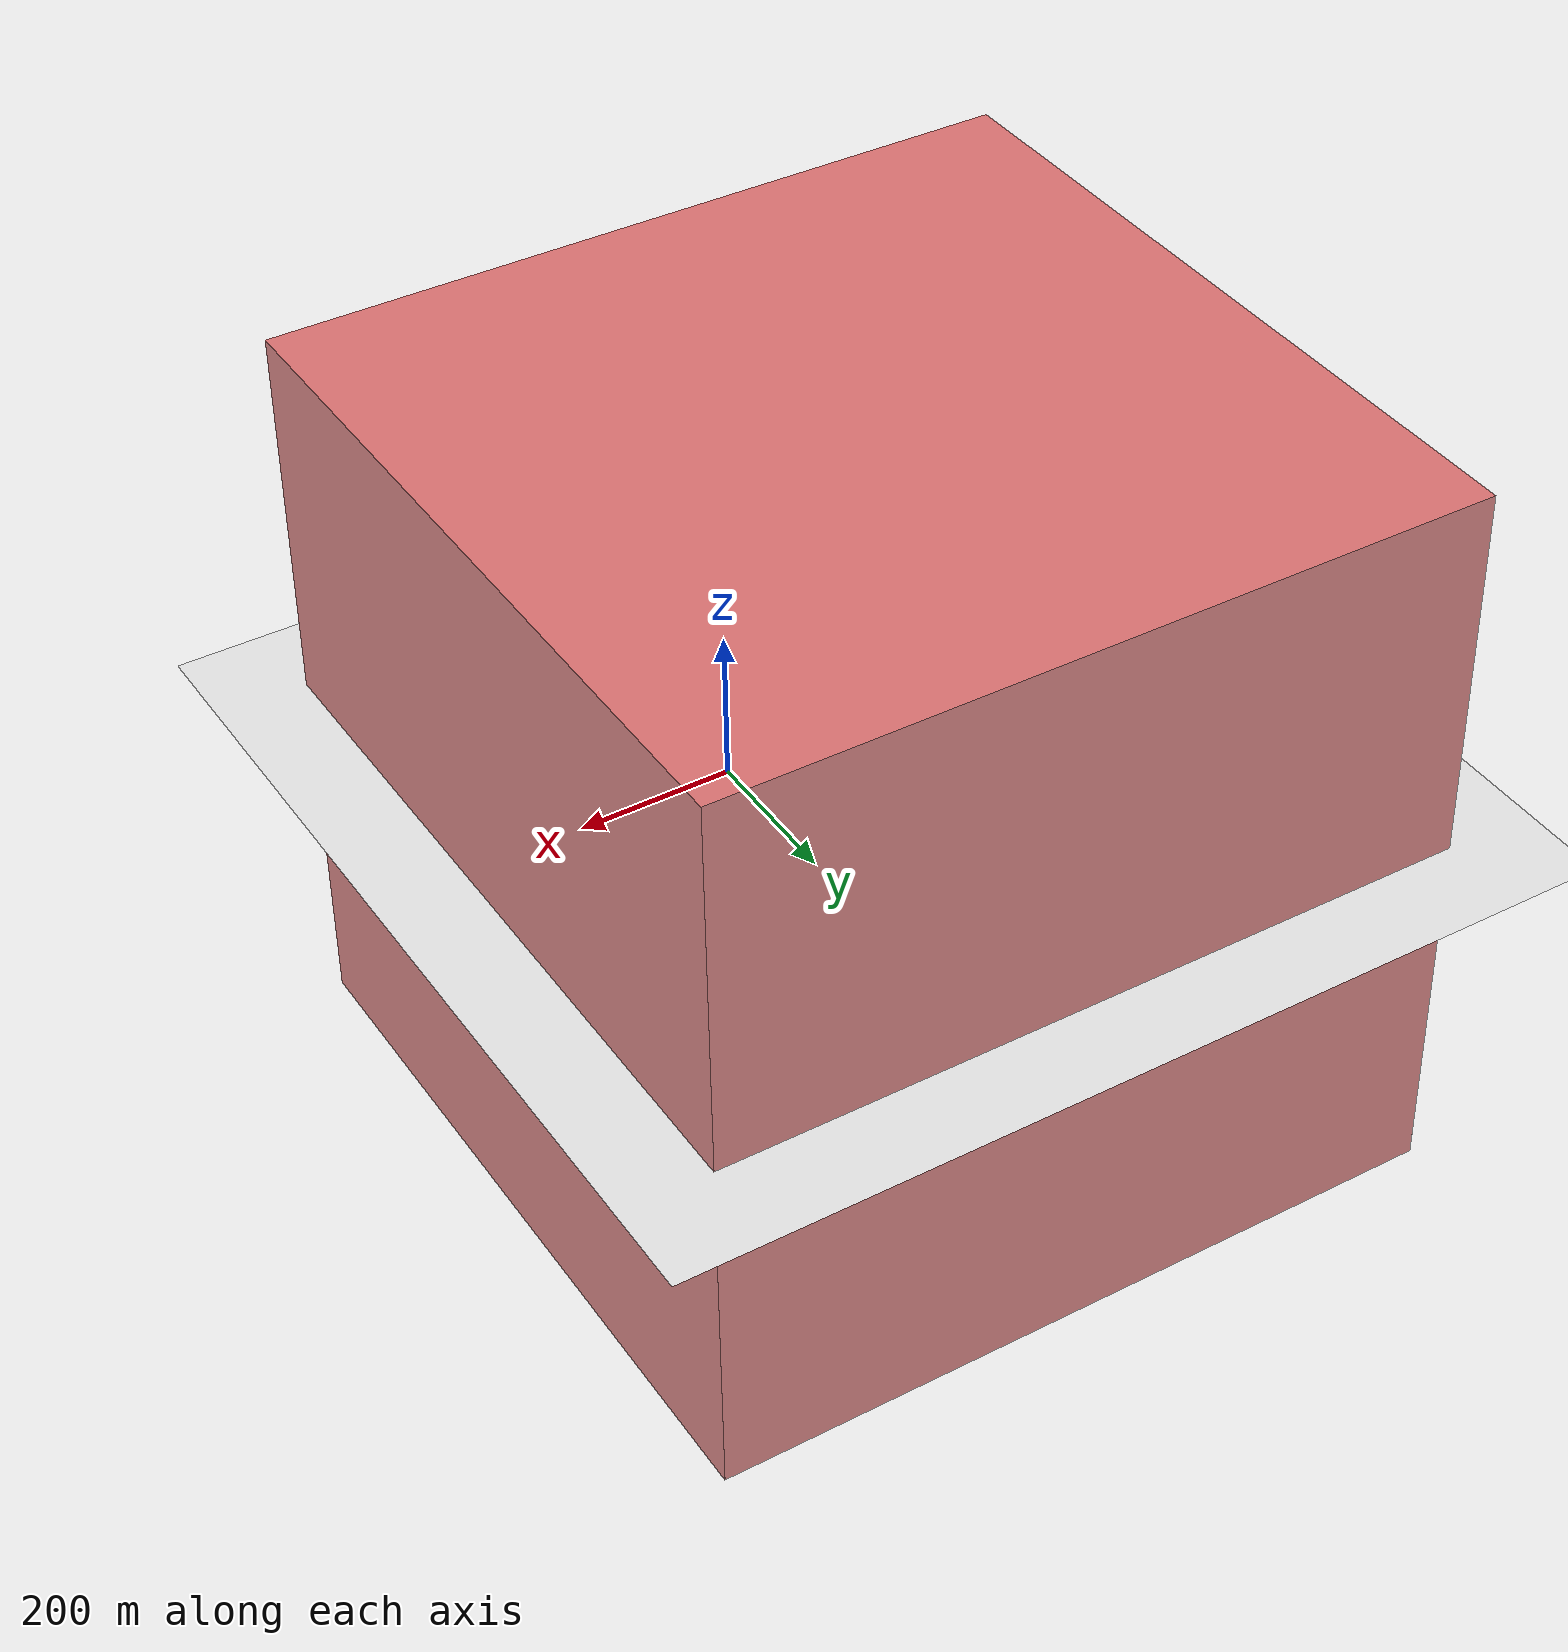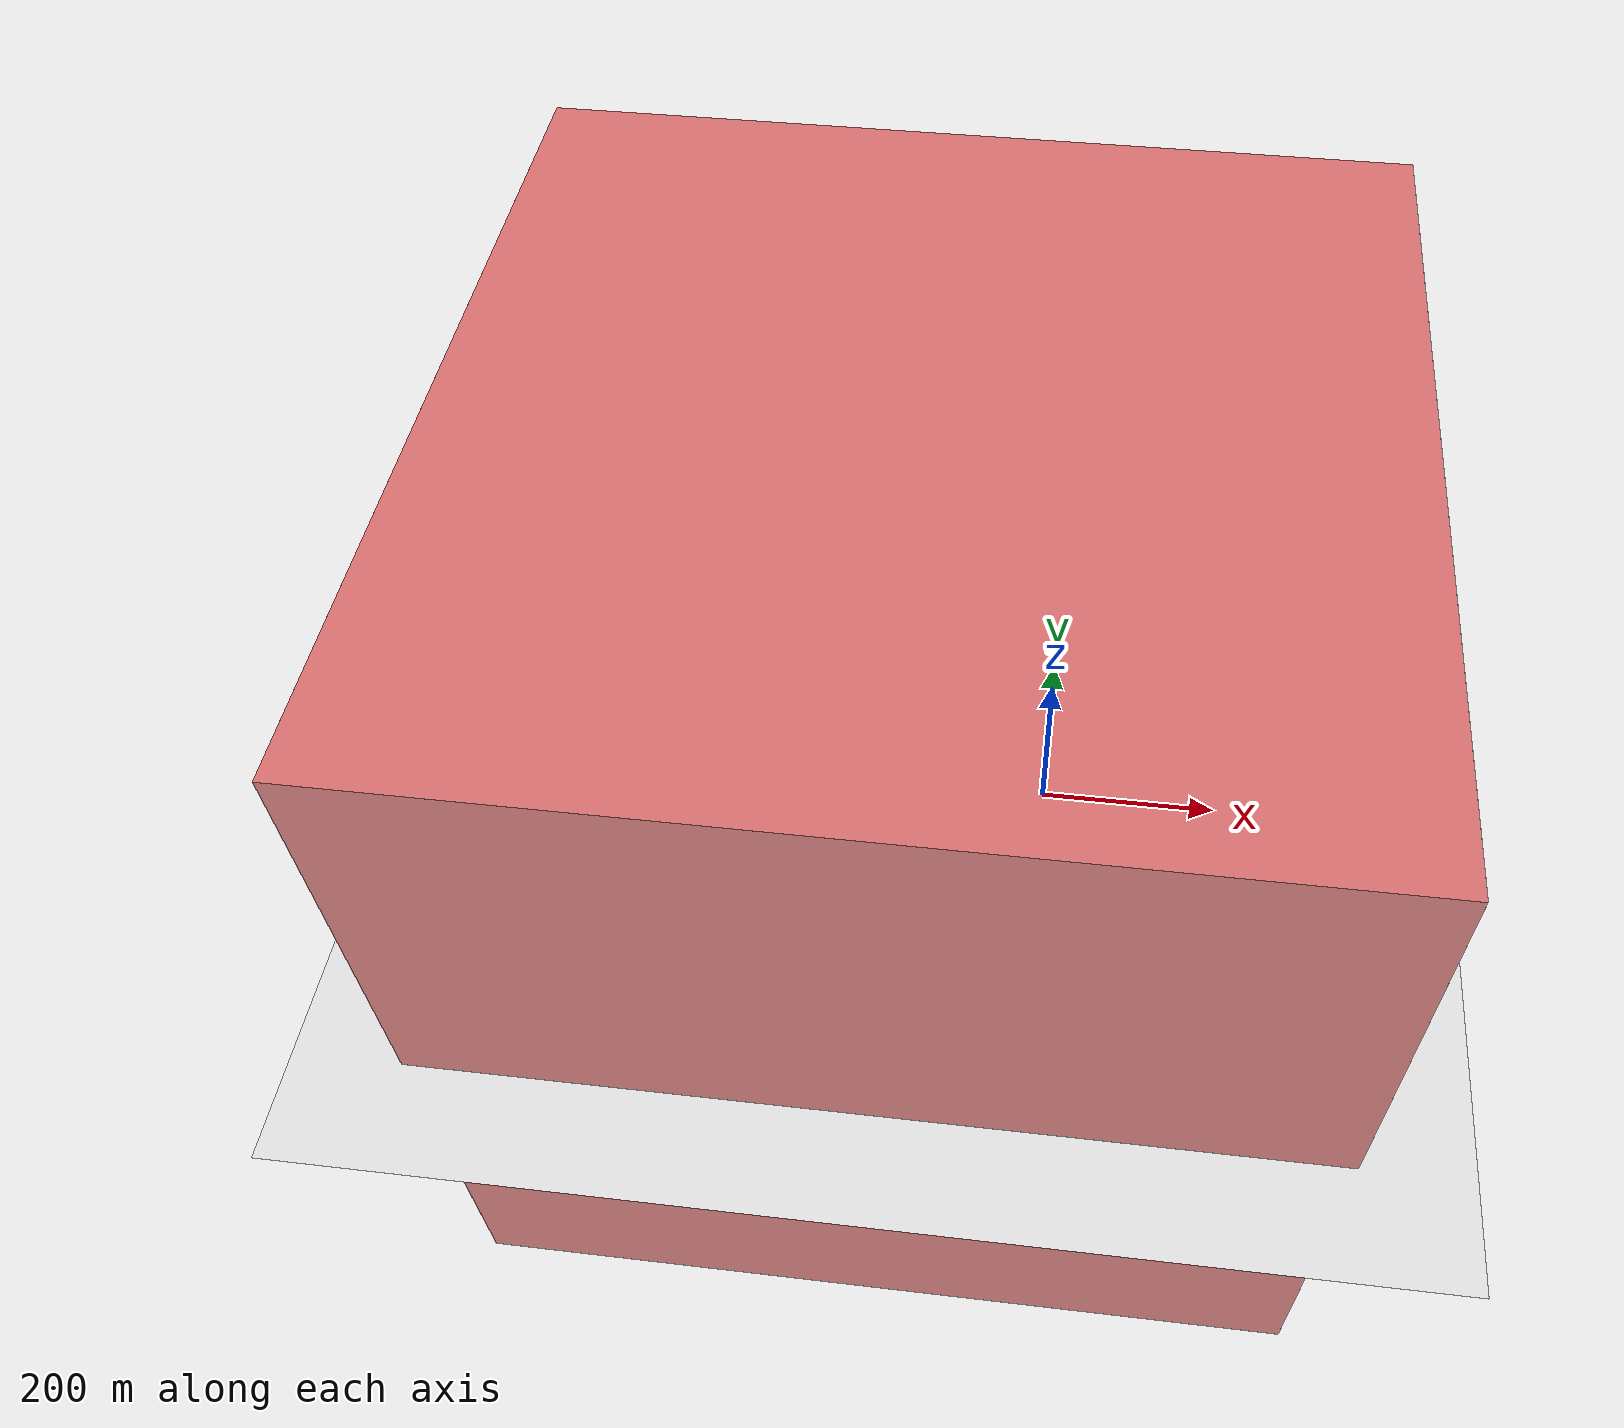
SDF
<sdf version="1.6">
 <world name="default">
  <light name="sun" type="directional">
   <pose>0 0 10 0 -0 0</pose>
   <diffuse>0.8 0.8 0.8 1</diffuse>
   <specular>0.1 0.1 0.1 1</specular>
   <attenuation>
    <range>1000</range>
    <constant>0.9</constant>
    <linear>0.01</linear>
    <quadratic>0.001</quadratic>
   </attenuation>
   <direction>-0.5 0.5 -1</direction>
  </light>
  <plugin name="SetupWorld" filename="libgazebo_plugins.so"/>
  <gravity>0 0 -9.8</gravity>
  <magnetic_field>6e-06 2.3e-05 -4.2e-05</magnetic_field>
  <atmosphere type="adiabatic"/>
  <physics name="default_physics" default="0" type="ode">
   <max_step_size>0.001</max_step_size>
   <real_time_factor>1</real_time_factor>
   <real_time_update_rate>1000</real_time_update_rate>
  </physics>
  <scene><ambient>0.4 0.4 0.4 1</ambient><background>0.7 0.7 0.7 1</background><shadows>1</shadows></scene>
  <spherical_coordinates>
   <surface_model>EARTH_WGS84</surface_model>
   <latitude_deg>0</latitude_deg>
   <longitude_deg>0</longitude_deg>
   <elevation>0</elevation>
   <heading_deg>0</heading_deg>
  </spherical_coordinates>
  <model name="at0">
   <static>0</static>
   <link name="link">
    <inertial>
     <mass>0.01</mass>
     <inertia><ixx>4e-05</ixx><ixy>0</ixy><ixz>0</ixz><iyy>4e-05</iyy><iyz>0</iyz><izz>4e-05</izz></inertia>
    </inertial>
    <visual name="visual">
     <geometry><box><size>0.05 0.05 0.05</size></box></geometry>
     <material>
      <script>
       <uri>model://at0/materials/scripts</uri>
       <uri>model://at0/materials/textures</uri>
       <name>at0/Diffuse</name>
      </script>
     </material>
    </visual>
    <collision name="collision">
     <geometry><box><size>0.05 0.05 0.05</size></box></geometry>
     <surface><friction><ode><mu>0.8</mu><mu2>0.7</mu2></ode></friction></surface>
    </collision>
   </link>
   <pose>-4.69459 1.45752 0.024997 -2.9e-05 2.9e-05 -1e-06</pose>
  </model>
  <model name="at1">
   <static>0</static>
   <link name="link">
    <inertial>
     <mass>0.01</mass>
     <inertia><ixx>4e-05</ixx><ixy>0</ixy><ixz>0</ixz><iyy>4e-05</iyy><iyz>0</iyz><izz>4e-05</izz></inertia>
    </inertial>
    <visual name="visual">
     <geometry><box><size>0.05 0.05 0.05</size></box></geometry>
     <material>
      <script>
       <uri>model://at0/materials/scripts</uri>
       <uri>model://at0/materials/textures</uri>
       <name>at0/Diffuse</name>
      </script>
     </material>
    </visual>
    <collision name="collision">
     <geometry><box><size>0.05 0.05 0.05</size></box></geometry>
     <surface><friction><ode><mu>0.8</mu><mu2>0.7</mu2></ode></friction></surface>
    </collision>
   </link>
   <pose>-3.90677 -4.11847 0.024997 2.9e-05 -2.9e-05 -1e-06</pose>
  </model>
  <model name="at2">
   <static>0</static>
   <link name="link">
    <inertial>
     <mass>0.01</mass>
     <inertia><ixx>4e-05</ixx><ixy>0</ixy><ixz>0</ixz><iyy>4e-05</iyy><iyz>0</iyz><izz>4e-05</izz></inertia>
    </inertial>
    <visual name="visual">
     <geometry><box><size>0.05 0.05 0.05</size></box></geometry>
     <material>
      <script>
       <uri>model://at0/materials/scripts</uri>
       <uri>model://at0/materials/textures</uri>
       <name>at0/Diffuse</name>
      </script>
     </material>
    </visual>
    <collision name="collision">
     <geometry><box><size>0.05 0.05 0.05</size></box></geometry>
     <surface><friction><ode><mu>0.8</mu><mu2>0.7</mu2></ode></friction></surface>
    </collision>
   </link>
   <pose>-5.68073 4.17379 0.024997 -2.9e-05 2.9e-05 -1e-06</pose>
  </model>
  <model name="at3">
   <static>0</static>
   <link name="link">
    <inertial>
     <mass>0.01</mass>
     <inertia><ixx>4e-05</ixx><ixy>0</ixy><ixz>0</ixz><iyy>4e-05</iyy><iyz>0</iyz><izz>4e-05</izz></inertia>
    </inertial>
    <visual name="visual">
     <geometry><box><size>0.05 0.05 0.05</size></box></geometry>
     <material>
      <script>
       <uri>model://at0/materials/scripts</uri>
       <uri>model://at0/materials/textures</uri>
       <name>at0/Diffuse</name>
      </script>
     </material>
    </visual>
    <collision name="collision">
     <geometry><box><size>0.05 0.05 0.05</size></box></geometry>
     <surface><friction><ode><mu>0.8</mu><mu2>0.7</mu2></ode></friction></surface>
    </collision>
   </link>
   <pose>2.27393 -3.70157 0.024997 2.9e-05 -2.9e-05 -1e-06</pose>
  </model>
  <model name="at4">
   <static>0</static>
   <link name="link">
    <inertial>
     <mass>0.01</mass>
     <inertia><ixx>4e-05</ixx><ixy>0</ixy><ixz>0</ixz><iyy>4e-05</iyy><iyz>0</iyz><izz>4e-05</izz></inertia>
    </inertial>
    <visual name="visual">
     <geometry><box><size>0.05 0.05 0.05</size></box></geometry>
     <material>
      <script>
       <uri>model://at0/materials/scripts</uri>
       <uri>model://at0/materials/textures</uri>
       <name>at0/Diffuse</name>
      </script>
     </material>
    </visual>
    <collision name="collision">
     <geometry><box><size>0.05 0.05 0.05</size></box></geometry>
     <surface><friction><ode><mu>0.8</mu><mu2>0.7</mu2></ode></friction></surface>
    </collision>
   </link>
   <pose>3.06671 -0.744785 0.024997 -2.9e-05 2.9e-05 -1e-06</pose>
  </model>
  <model name="at5">
   <static>0</static>
   <link name="link">
    <inertial>
     <mass>0.01</mass>
     <inertia><ixx>4e-05</ixx><ixy>0</ixy><ixz>0</ixz><iyy>4e-05</iyy><iyz>0</iyz><izz>4e-05</izz></inertia>
    </inertial>
    <visual name="visual">
     <geometry><box><size>0.05 0.05 0.05</size></box></geometry>
     <material>
      <script>
       <uri>model://at0/materials/scripts</uri>
       <uri>model://at0/materials/textures</uri>
       <name>at0/Diffuse</name>
      </script>
     </material>
    </visual>
    <collision name="collision">
     <geometry><box><size>0.05 0.05 0.05</size></box></geometry>
     <surface><friction><ode><mu>0.8</mu><mu2>0.7</mu2></ode></friction></surface>
    </collision>
   </link>
   <pose>0.31192 -1.77842 0.024997 2.9e-05 -2.9e-05 -1e-06</pose>
  </model>
  <model name="at6">
   <static>0</static>
   <link name="link">
    <inertial>
     <mass>0.01</mass>
     <inertia><ixx>4e-05</ixx><ixy>0</ixy><ixz>0</ixz><iyy>4e-05</iyy><iyz>0</iyz><izz>4e-05</izz></inertia>
    </inertial>
    <visual name="visual">
     <geometry><box><size>0.05 0.05 0.05</size></box></geometry>
     <material>
      <script>
       <uri>model://at0/materials/scripts</uri>
       <uri>model://at0/materials/textures</uri>
       <name>at0/Diffuse</name>
      </script>
     </material>
    </visual>
    <collision name="collision">
     <geometry><box><size>0.05 0.05 0.05</size></box></geometry>
     <surface><friction><ode><mu>0.8</mu><mu2>0.7</mu2></ode></friction></surface>
    </collision>
   </link>
   <pose>1.86597 -0.184932 0.024997 -2.9e-05 2.9e-05 -1e-06</pose>
  </model>
  <model name="at7">
   <static>0</static>
   <link name="link">
    <inertial>
     <mass>0.01</mass>
     <inertia><ixx>4e-05</ixx><ixy>0</ixy><ixz>0</ixz><iyy>4e-05</iyy><iyz>0</iyz><izz>4e-05</izz></inertia>
    </inertial>
    <visual name="visual">
     <geometry><box><size>0.05 0.05 0.05</size></box></geometry>
     <material>
      <script>
       <uri>model://at0/materials/scripts</uri>
       <uri>model://at0/materials/textures</uri>
       <name>at0/Diffuse</name>
      </script>
     </material>
    </visual>
    <collision name="collision">
     <geometry><box><size>0.05 0.05 0.05</size></box></geometry>
     <surface><friction><ode><mu>0.8</mu><mu2>0.7</mu2></ode></friction></surface>
    </collision>
   </link>
   <pose>-6.24077 -5.74349 0.024997 2.9e-05 -2.9e-05 -1e-06</pose>
  </model>
  <model name="at8">
   <static>0</static>
   <link name="link">
    <inertial>
     <mass>0.01</mass>
     <inertia><ixx>4e-05</ixx><ixy>0</ixy><ixz>0</ixz><iyy>4e-05</iyy><iyz>0</iyz><izz>4e-05</izz></inertia>
    </inertial>
    <visual name="visual">
     <geometry><box><size>0.05 0.05 0.05</size></box></geometry>
     <material>
      <script>
       <uri>model://at0/materials/scripts</uri>
       <uri>model://at0/materials/textures</uri>
       <name>at0/Diffuse</name>
      </script>
     </material>
    </visual>
    <collision name="collision">
     <geometry><box><size>0.05 0.05 0.05</size></box></geometry>
     <surface><friction><ode><mu>0.8</mu><mu2>0.7</mu2></ode></friction></surface>
    </collision>
   </link>
   <pose>-1.87282 -2.9987 0.024997 -2.9e-05 2.9e-05 -1e-06</pose>
  </model>
  <model name="at9">
   <static>0</static>
   <link name="link">
    <inertial>
     <mass>0.01</mass>
     <inertia><ixx>4e-05</ixx><ixy>0</ixy><ixz>0</ixz><iyy>4e-05</iyy><iyz>0</iyz><izz>4e-05</izz></inertia>
    </inertial>
    <visual name="visual">
     <geometry><box><size>0.05 0.05 0.05</size></box></geometry>
     <material>
      <script>
       <uri>model://at0/materials/scripts</uri>
       <uri>model://at0/materials/textures</uri>
       <name>at0/Diffuse</name>
      </script>
     </material>
    </visual>
    <collision name="collision">
     <geometry><box><size>0.05 0.05 0.05</size></box></geometry>
     <surface><friction><ode><mu>0.8</mu><mu2>0.7</mu2></ode></friction></surface>
    </collision>
   </link>
   <pose>4.94588 -1.47617 0.024997 2.9e-05 -2.9e-05 -1e-06</pose>
  </model>
  <model name="at10">
   <static>0</static>
   <link name="link">
    <inertial>
     <mass>0.01</mass>
     <inertia><ixx>4e-05</ixx><ixy>0</ixy><ixz>0</ixz><iyy>4e-05</iyy><iyz>0</iyz><izz>4e-05</izz></inertia>
    </inertial>
    <visual name="visual">
     <geometry><box><size>0.05 0.05 0.05</size></box></geometry>
     <material>
      <script>
       <uri>model://at0/materials/scripts</uri>
       <uri>model://at0/materials/textures</uri>
       <name>at0/Diffuse</name>
      </script>
     </material>
    </visual>
    <collision name="collision">
     <geometry><box><size>0.05 0.05 0.05</size></box></geometry>
     <surface><friction><ode><mu>0.8</mu><mu2>0.7</mu2></ode></friction></surface>
    </collision>
   </link>
   <pose>6.67505 3.54816 0.024997 -2.9e-05 2.9e-05 -1e-06</pose>
  </model>
  <model name="at11">
   <static>0</static>
   <link name="link">
    <inertial>
     <mass>0.01</mass>
     <inertia><ixx>4e-05</ixx><ixy>0</ixy><ixz>0</ixz><iyy>4e-05</iyy><iyz>0</iyz><izz>4e-05</izz></inertia>
    </inertial>
    <visual name="visual">
     <geometry><box><size>0.05 0.05 0.05</size></box></geometry>
     <material>
      <script>
       <uri>model://at0/materials/scripts</uri>
       <uri>model://at0/materials/textures</uri>
       <name>at0/Diffuse</name>
      </script>
     </material>
    </visual>
    <collision name="collision">
     <geometry><box><size>0.05 0.05 0.05</size></box></geometry>
     <surface><friction><ode><mu>0.8</mu><mu2>0.7</mu2></ode></friction></surface>
    </collision>
   </link>
   <pose>5.0062 -4.19764 0.024997 2.9e-05 -2.9e-05 -1e-06</pose>
  </model>
  <model name="at12">
   <static>0</static>
   <link name="link">
    <inertial>
     <mass>0.01</mass>
     <inertia><ixx>4e-05</ixx><ixy>0</ixy><ixz>0</ixz><iyy>4e-05</iyy><iyz>0</iyz><izz>4e-05</izz></inertia>
    </inertial>
    <visual name="visual">
     <geometry><box><size>0.05 0.05 0.05</size></box></geometry>
     <material>
      <script>
       <uri>model://at0/materials/scripts</uri>
       <uri>model://at0/materials/textures</uri>
       <name>at0/Diffuse</name>
      </script>
     </material>
    </visual>
    <collision name="collision">
     <geometry><box><size>0.05 0.05 0.05</size></box></geometry>
     <surface><friction><ode><mu>0.8</mu><mu2>0.7</mu2></ode></friction></surface>
    </collision>
   </link>
   <pose>4.73783 1.36697 0.024997 -2.9e-05 2.9e-05 -1e-06</pose>
  </model>
  <model name="at13">
   <static>0</static>
   <link name="link">
    <inertial>
     <mass>0.01</mass>
     <inertia><ixx>4e-05</ixx><ixy>0</ixy><ixz>0</ixz><iyy>4e-05</iyy><iyz>0</iyz><izz>4e-05</izz></inertia>
    </inertial>
    <visual name="visual">
     <geometry><box><size>0.05 0.05 0.05</size></box></geometry>
     <material>
      <script>
       <uri>model://at0/materials/scripts</uri>
       <uri>model://at0/materials/textures</uri>
       <name>at0/Diffuse</name>
      </script>
     </material>
    </visual>
    <collision name="collision">
     <geometry><box><size>0.05 0.05 0.05</size></box></geometry>
     <surface><friction><ode><mu>0.8</mu><mu2>0.7</mu2></ode></friction></surface>
    </collision>
   </link>
   <pose>5.10889 5.39844 0.024997 2.9e-05 -2.9e-05 -1e-06</pose>
  </model>
  <model name="at14">
   <static>0</static>
   <link name="link">
    <inertial>
     <mass>0.01</mass>
     <inertia><ixx>4e-05</ixx><ixy>0</ixy><ixz>0</ixz><iyy>4e-05</iyy><iyz>0</iyz><izz>4e-05</izz></inertia>
    </inertial>
    <visual name="visual">
     <geometry><box><size>0.05 0.05 0.05</size></box></geometry>
     <material>
      <script>
       <uri>model://at0/materials/scripts</uri>
       <uri>model://at0/materials/textures</uri>
       <name>at0/Diffuse</name>
      </script>
     </material>
    </visual>
    <collision name="collision">
     <geometry><box><size>0.05 0.05 0.05</size></box></geometry>
     <surface><friction><ode><mu>0.8</mu><mu2>0.7</mu2></ode></friction></surface>
    </collision>
   </link>
   <pose>-6.88516 3.88805 0.024997 -2.9e-05 2.9e-05 -1e-06</pose>
  </model>
  <model name="at15">
   <static>0</static>
   <link name="link">
    <inertial>
     <mass>0.01</mass>
     <inertia><ixx>4e-05</ixx><ixy>0</ixy><ixz>0</ixz><iyy>4e-05</iyy><iyz>0</iyz><izz>4e-05</izz></inertia>
    </inertial>
    <visual name="visual">
     <geometry><box><size>0.05 0.05 0.05</size></box></geometry>
     <material>
      <script>
       <uri>model://at0/materials/scripts</uri>
       <uri>model://at0/materials/textures</uri>
       <name>at0/Diffuse</name>
      </script>
     </material>
    </visual>
    <collision name="collision">
     <geometry><box><size>0.05 0.05 0.05</size></box></geometry>
     <surface><friction><ode><mu>0.8</mu><mu2>0.7</mu2></ode></friction></surface>
    </collision>
   </link>
   <pose>-0.178468 -4.67975 0.024997 2.9e-05 -2.9e-05 -1e-06</pose>
  </model>
  <model name="at16">
   <static>0</static>
   <link name="link">
    <inertial>
     <mass>0.01</mass>
     <inertia><ixx>4e-05</ixx><ixy>0</ixy><ixz>0</ixz><iyy>4e-05</iyy><iyz>0</iyz><izz>4e-05</izz></inertia>
    </inertial>
    <visual name="visual">
     <geometry><box><size>0.05 0.05 0.05</size></box></geometry>
     <material>
      <script>
       <uri>model://at0/materials/scripts</uri>
       <uri>model://at0/materials/textures</uri>
       <name>at0/Diffuse</name>
      </script>
     </material>
    </visual>
    <collision name="collision">
     <geometry><box><size>0.05 0.05 0.05</size></box></geometry>
     <surface><friction><ode><mu>0.8</mu><mu2>0.7</mu2></ode></friction></surface>
    </collision>
   </link>
   <pose>-1.55443 2.81476 0.024997 -2.9e-05 2.9e-05 -1e-06</pose>
  </model>
  <model name="at17">
   <static>0</static>
   <link name="link">
    <inertial>
     <mass>0.01</mass>
     <inertia><ixx>4e-05</ixx><ixy>0</ixy><ixz>0</ixz><iyy>4e-05</iyy><iyz>0</iyz><izz>4e-05</izz></inertia>
    </inertial>
    <visual name="visual">
     <geometry><box><size>0.05 0.05 0.05</size></box></geometry>
     <material>
      <script>
       <uri>model://at0/materials/scripts</uri>
       <uri>model://at0/materials/textures</uri>
       <name>at0/Diffuse</name>
      </script>
     </material>
    </visual>
    <collision name="collision">
     <geometry><box><size>0.05 0.05 0.05</size></box></geometry>
     <surface><friction><ode><mu>0.8</mu><mu2>0.7</mu2></ode></friction></surface>
    </collision>
   </link>
   <pose>-1.89822 -0.335164 0.024997 2.9e-05 -2.9e-05 -1e-06</pose>
  </model>
  <model name="at18">
   <static>0</static>
   <link name="link">
    <inertial>
     <mass>0.01</mass>
     <inertia><ixx>4e-05</ixx><ixy>0</ixy><ixz>0</ixz><iyy>4e-05</iyy><iyz>0</iyz><izz>4e-05</izz></inertia>
    </inertial>
    <visual name="visual">
     <geometry><box><size>0.05 0.05 0.05</size></box></geometry>
     <material>
      <script>
       <uri>model://at0/materials/scripts</uri>
       <uri>model://at0/materials/textures</uri>
       <name>at0/Diffuse</name>
      </script>
     </material>
    </visual>
    <collision name="collision">
     <geometry><box><size>0.05 0.05 0.05</size></box></geometry>
     <surface><friction><ode><mu>0.8</mu><mu2>0.7</mu2></ode></friction></surface>
    </collision>
   </link>
   <pose>0.088556 -6.5243 0.024997 -2.9e-05 2.9e-05 -1e-06</pose>
  </model>
  <model name="at19">
   <static>0</static>
   <link name="link">
    <inertial>
     <mass>0.01</mass>
     <inertia><ixx>4e-05</ixx><ixy>0</ixy><ixz>0</ixz><iyy>4e-05</iyy><iyz>0</iyz><izz>4e-05</izz></inertia>
    </inertial>
    <visual name="visual">
     <geometry><box><size>0.05 0.05 0.05</size></box></geometry>
     <material>
      <script>
       <uri>model://at0/materials/scripts</uri>
       <uri>model://at0/materials/textures</uri>
       <name>at0/Diffuse</name>
      </script>
     </material>
    </visual>
    <collision name="collision">
     <geometry><box><size>0.05 0.05 0.05</size></box></geometry>
     <surface><friction><ode><mu>0.8</mu><mu2>0.7</mu2></ode></friction></surface>
    </collision>
   </link>
   <pose>2.86327 -3.74474 0.024997 2.9e-05 -2.9e-05 -1e-06</pose>
  </model>
  <model name="at20">
   <static>0</static>
   <link name="link">
    <inertial>
     <mass>0.01</mass>
     <inertia><ixx>4e-05</ixx><ixy>0</ixy><ixz>0</ixz><iyy>4e-05</iyy><iyz>0</iyz><izz>4e-05</izz></inertia>
    </inertial>
    <visual name="visual">
     <geometry><box><size>0.05 0.05 0.05</size></box></geometry>
     <material>
      <script>
       <uri>model://at0/materials/scripts</uri>
       <uri>model://at0/materials/textures</uri>
       <name>at0/Diffuse</name>
      </script>
     </material>
    </visual>
    <collision name="collision">
     <geometry><box><size>0.05 0.05 0.05</size></box></geometry>
     <surface><friction><ode><mu>0.8</mu><mu2>0.7</mu2></ode></friction></surface>
    </collision>
   </link>
   <pose>-0.36908 -3.72481 0.024997 -2.9e-05 2.9e-05 -1e-06</pose>
  </model>
  <model name="at21">
   <static>0</static>
   <link name="link">
    <inertial>
     <mass>0.01</mass>
     <inertia><ixx>4e-05</ixx><ixy>0</ixy><ixz>0</ixz><iyy>4e-05</iyy><iyz>0</iyz><izz>4e-05</izz></inertia>
    </inertial>
    <visual name="visual">
     <geometry><box><size>0.05 0.05 0.05</size></box></geometry>
     <material>
      <script>
       <uri>model://at0/materials/scripts</uri>
       <uri>model://at0/materials/textures</uri>
       <name>at0/Diffuse</name>
      </script>
     </material>
    </visual>
    <collision name="collision">
     <geometry><box><size>0.05 0.05 0.05</size></box></geometry>
     <surface><friction><ode><mu>0.8</mu><mu2>0.7</mu2></ode></friction></surface>
    </collision>
   </link>
   <pose>1.37684 -5.40311 0.024997 2.9e-05 -2.9e-05 -1e-06</pose>
  </model>
  <model name="at22">
   <static>0</static>
   <link name="link">
    <inertial>
     <mass>0.01</mass>
     <inertia><ixx>4e-05</ixx><ixy>0</ixy><ixz>0</ixz><iyy>4e-05</iyy><iyz>0</iyz><izz>4e-05</izz></inertia>
    </inertial>
    <visual name="visual">
     <geometry><box><size>0.05 0.05 0.05</size></box></geometry>
     <material>
      <script>
       <uri>model://at0/materials/scripts</uri>
       <uri>model://at0/materials/textures</uri>
       <name>at0/Diffuse</name>
      </script>
     </material>
    </visual>
    <collision name="collision">
     <geometry><box><size>0.05 0.05 0.05</size></box></geometry>
     <surface><friction><ode><mu>0.8</mu><mu2>0.7</mu2></ode></friction></surface>
    </collision>
   </link>
   <pose>2.99026 2.03607 0.024997 -2.9e-05 2.9e-05 -1e-06</pose>
  </model>
  <model name="at23">
   <static>0</static>
   <link name="link">
    <inertial>
     <mass>0.01</mass>
     <inertia><ixx>4e-05</ixx><ixy>0</ixy><ixz>0</ixz><iyy>4e-05</iyy><iyz>0</iyz><izz>4e-05</izz></inertia>
    </inertial>
    <visual name="visual">
     <geometry><box><size>0.05 0.05 0.05</size></box></geometry>
     <material>
      <script>
       <uri>model://at0/materials/scripts</uri>
       <uri>model://at0/materials/textures</uri>
       <name>at0/Diffuse</name>
      </script>
     </material>
    </visual>
    <collision name="collision">
     <geometry><box><size>0.05 0.05 0.05</size></box></geometry>
     <surface><friction><ode><mu>0.8</mu><mu2>0.7</mu2></ode></friction></surface>
    </collision>
   </link>
   <pose>-4.2466 -5.78257 0.024997 2.9e-05 -2.9e-05 -1e-06</pose>
  </model>
  <model name="at24">
   <static>0</static>
   <link name="link">
    <inertial>
     <mass>0.01</mass>
     <inertia><ixx>4e-05</ixx><ixy>0</ixy><ixz>0</ixz><iyy>4e-05</iyy><iyz>0</iyz><izz>4e-05</izz></inertia>
    </inertial>
    <visual name="visual">
     <geometry><box><size>0.05 0.05 0.05</size></box></geometry>
     <material>
      <script>
       <uri>model://at0/materials/scripts</uri>
       <uri>model://at0/materials/textures</uri>
       <name>at0/Diffuse</name>
      </script>
     </material>
    </visual>
    <collision name="collision">
     <geometry><box><size>0.05 0.05 0.05</size></box></geometry>
     <surface><friction><ode><mu>0.8</mu><mu2>0.7</mu2></ode></friction></surface>
    </collision>
   </link>
   <pose>5.93738 -6.20071 0.024997 -2.9e-05 2.9e-05 -1e-06</pose>
  </model>
  <model name="at25">
   <static>0</static>
   <link name="link">
    <inertial>
     <mass>0.01</mass>
     <inertia><ixx>4e-05</ixx><ixy>0</ixy><ixz>0</ixz><iyy>4e-05</iyy><iyz>0</iyz><izz>4e-05</izz></inertia>
    </inertial>
    <visual name="visual">
     <geometry><box><size>0.05 0.05 0.05</size></box></geometry>
     <material>
      <script>
       <uri>model://at0/materials/scripts</uri>
       <uri>model://at0/materials/textures</uri>
       <name>at0/Diffuse</name>
      </script>
     </material>
    </visual>
    <collision name="collision">
     <geometry><box><size>0.05 0.05 0.05</size></box></geometry>
     <surface><friction><ode><mu>0.8</mu><mu2>0.7</mu2></ode></friction></surface>
    </collision>
   </link>
   <pose>-0.358737 5.71243 0.024997 2.9e-05 -2.9e-05 -1e-06</pose>
  </model>
  <model name="at26">
   <static>0</static>
   <link name="link">
    <inertial>
     <mass>0.01</mass>
     <inertia><ixx>4e-05</ixx><ixy>0</ixy><ixz>0</ixz><iyy>4e-05</iyy><iyz>0</iyz><izz>4e-05</izz></inertia>
    </inertial>
    <visual name="visual">
     <geometry><box><size>0.05 0.05 0.05</size></box></geometry>
     <material>
      <script>
       <uri>model://at0/materials/scripts</uri>
       <uri>model://at0/materials/textures</uri>
       <name>at0/Diffuse</name>
      </script>
     </material>
    </visual>
    <collision name="collision">
     <geometry><box><size>0.05 0.05 0.05</size></box></geometry>
     <surface><friction><ode><mu>0.8</mu><mu2>0.7</mu2></ode></friction></surface>
    </collision>
   </link>
   <pose>4.24745 -2.25253 0.024997 -2.9e-05 2.9e-05 -1e-06</pose>
  </model>
  <model name="at27">
   <static>0</static>
   <link name="link">
    <inertial>
     <mass>0.01</mass>
     <inertia><ixx>4e-05</ixx><ixy>0</ixy><ixz>0</ixz><iyy>4e-05</iyy><iyz>0</iyz><izz>4e-05</izz></inertia>
    </inertial>
    <visual name="visual">
     <geometry><box><size>0.05 0.05 0.05</size></box></geometry>
     <material>
      <script>
       <uri>model://at0/materials/scripts</uri>
       <uri>model://at0/materials/textures</uri>
       <name>at0/Diffuse</name>
      </script>
     </material>
    </visual>
    <collision name="collision">
     <geometry><box><size>0.05 0.05 0.05</size></box></geometry>
     <surface><friction><ode><mu>0.8</mu><mu2>0.7</mu2></ode></friction></surface>
    </collision>
   </link>
   <pose>-5.38521 2.08528 0.024997 2.9e-05 -2.9e-05 -1e-06</pose>
  </model>
  <model name="at28">
   <static>0</static>
   <link name="link">
    <inertial>
     <mass>0.01</mass>
     <inertia><ixx>4e-05</ixx><ixy>0</ixy><ixz>0</ixz><iyy>4e-05</iyy><iyz>0</iyz><izz>4e-05</izz></inertia>
    </inertial>
    <visual name="visual">
     <geometry><box><size>0.05 0.05 0.05</size></box></geometry>
     <material>
      <script>
       <uri>model://at0/materials/scripts</uri>
       <uri>model://at0/materials/textures</uri>
       <name>at0/Diffuse</name>
      </script>
     </material>
    </visual>
    <collision name="collision">
     <geometry><box><size>0.05 0.05 0.05</size></box></geometry>
     <surface><friction><ode><mu>0.8</mu><mu2>0.7</mu2></ode></friction></surface>
    </collision>
   </link>
   <pose>6.01444 6.62368 0.024997 -2.9e-05 2.9e-05 -1e-06</pose>
  </model>
  <model name="at29">
   <static>0</static>
   <link name="link">
    <inertial>
     <mass>0.01</mass>
     <inertia><ixx>4e-05</ixx><ixy>0</ixy><ixz>0</ixz><iyy>4e-05</iyy><iyz>0</iyz><izz>4e-05</izz></inertia>
    </inertial>
    <visual name="visual">
     <geometry><box><size>0.05 0.05 0.05</size></box></geometry>
     <material>
      <script>
       <uri>model://at0/materials/scripts</uri>
       <uri>model://at0/materials/textures</uri>
       <name>at0/Diffuse</name>
      </script>
     </material>
    </visual>
    <collision name="collision">
     <geometry><box><size>0.05 0.05 0.05</size></box></geometry>
     <surface><friction><ode><mu>0.8</mu><mu2>0.7</mu2></ode></friction></surface>
    </collision>
   </link>
   <pose>0.583715 6.02928 0.024997 2.9e-05 -2.9e-05 -1e-06</pose>
  </model>
  <model name="at30">
   <static>0</static>
   <link name="link">
    <inertial>
     <mass>0.01</mass>
     <inertia><ixx>4e-05</ixx><ixy>0</ixy><ixz>0</ixz><iyy>4e-05</iyy><iyz>0</iyz><izz>4e-05</izz></inertia>
    </inertial>
    <visual name="visual">
     <geometry><box><size>0.05 0.05 0.05</size></box></geometry>
     <material>
      <script>
       <uri>model://at0/materials/scripts</uri>
       <uri>model://at0/materials/textures</uri>
       <name>at0/Diffuse</name>
      </script>
     </material>
    </visual>
    <collision name="collision">
     <geometry><box><size>0.05 0.05 0.05</size></box></geometry>
     <surface><friction><ode><mu>0.8</mu><mu2>0.7</mu2></ode></friction></surface>
    </collision>
   </link>
   <pose>3.61174 -6.49475 0.024997 -2.9e-05 2.9e-05 -1e-06</pose>
  </model>
  <model name="at31">
   <static>0</static>
   <link name="link">
    <inertial>
     <mass>0.01</mass>
     <inertia><ixx>4e-05</ixx><ixy>0</ixy><ixz>0</ixz><iyy>4e-05</iyy><iyz>0</iyz><izz>4e-05</izz></inertia>
    </inertial>
    <visual name="visual">
     <geometry><box><size>0.05 0.05 0.05</size></box></geometry>
     <material>
      <script>
       <uri>model://at0/materials/scripts</uri>
       <uri>model://at0/materials/textures</uri>
       <name>at0/Diffuse</name>
      </script>
     </material>
    </visual>
    <collision name="collision">
     <geometry><box><size>0.05 0.05 0.05</size></box></geometry>
     <surface><friction><ode><mu>0.8</mu><mu2>0.7</mu2></ode></friction></surface>
    </collision>
   </link>
   <pose>-5.55047 -4.84269 0.024997 2.9e-05 -2.9e-05 -1e-06</pose>
  </model>
  <model name="at32">
   <static>0</static>
   <link name="link">
    <inertial>
     <mass>0.01</mass>
     <inertia><ixx>4e-05</ixx><ixy>0</ixy><ixz>0</ixz><iyy>4e-05</iyy><iyz>0</iyz><izz>4e-05</izz></inertia>
    </inertial>
    <visual name="visual">
     <geometry><box><size>0.05 0.05 0.05</size></box></geometry>
     <material>
      <script>
       <uri>model://at0/materials/scripts</uri>
       <uri>model://at0/materials/textures</uri>
       <name>at0/Diffuse</name>
      </script>
     </material>
    </visual>
    <collision name="collision">
     <geometry><box><size>0.05 0.05 0.05</size></box></geometry>
     <surface><friction><ode><mu>0.8</mu><mu2>0.7</mu2></ode></friction></surface>
    </collision>
   </link>
   <pose>3.22001 -0.548692 0.024997 -2.9e-05 2.9e-05 -1e-06</pose>
  </model>
  <model name="at33">
   <static>0</static>
   <link name="link">
    <inertial>
     <mass>0.01</mass>
     <inertia><ixx>4e-05</ixx><ixy>0</ixy><ixz>0</ixz><iyy>4e-05</iyy><iyz>0</iyz><izz>4e-05</izz></inertia>
    </inertial>
    <visual name="visual">
     <geometry><box><size>0.05 0.05 0.05</size></box></geometry>
     <material>
      <script>
       <uri>model://at0/materials/scripts</uri>
       <uri>model://at0/materials/textures</uri>
       <name>at0/Diffuse</name>
      </script>
     </material>
    </visual>
    <collision name="collision">
     <geometry><box><size>0.05 0.05 0.05</size></box></geometry>
     <surface><friction><ode><mu>0.8</mu><mu2>0.7</mu2></ode></friction></surface>
    </collision>
   </link>
   <pose>1.72214 -3.59143 0.024997 2.9e-05 -2.9e-05 -1e-06</pose>
  </model>
  <model name="at34">
   <static>0</static>
   <link name="link">
    <inertial>
     <mass>0.01</mass>
     <inertia><ixx>4e-05</ixx><ixy>0</ixy><ixz>0</ixz><iyy>4e-05</iyy><iyz>0</iyz><izz>4e-05</izz></inertia>
    </inertial>
    <visual name="visual">
     <geometry><box><size>0.05 0.05 0.05</size></box></geometry>
     <material>
      <script>
       <uri>model://at0/materials/scripts</uri>
       <uri>model://at0/materials/textures</uri>
       <name>at0/Diffuse</name>
      </script>
     </material>
    </visual>
    <collision name="collision">
     <geometry><box><size>0.05 0.05 0.05</size></box></geometry>
     <surface><friction><ode><mu>0.8</mu><mu2>0.7</mu2></ode></friction></surface>
    </collision>
   </link>
   <pose>-0.172989 -2.31459 0.024997 2.9e-05 -2.9e-05 -1e-06</pose>
  </model>
  <model name="at35">
   <static>0</static>
   <link name="link">
    <inertial>
     <mass>0.01</mass>
     <inertia><ixx>4e-05</ixx><ixy>0</ixy><ixz>0</ixz><iyy>4e-05</iyy><iyz>0</iyz><izz>4e-05</izz></inertia>
    </inertial>
    <visual name="visual">
     <geometry><box><size>0.05 0.05 0.05</size></box></geometry>
     <material>
      <script>
       <uri>model://at0/materials/scripts</uri>
       <uri>model://at0/materials/textures</uri>
       <name>at0/Diffuse</name>
      </script>
     </material>
    </visual>
    <collision name="collision">
     <geometry><box><size>0.05 0.05 0.05</size></box></geometry>
     <surface><friction><ode><mu>0.8</mu><mu2>0.7</mu2></ode></friction></surface>
    </collision>
   </link>
   <pose>-0.436168 6.35793 0.024997 -2.9e-05 2.9e-05 -1e-06</pose>
  </model>
  <model name="at36">
   <static>0</static>
   <link name="link">
    <inertial>
     <mass>0.01</mass>
     <inertia><ixx>4e-05</ixx><ixy>0</ixy><ixz>0</ixz><iyy>4e-05</iyy><iyz>0</iyz><izz>4e-05</izz></inertia>
    </inertial>
    <visual name="visual">
     <geometry><box><size>0.05 0.05 0.05</size></box></geometry>
     <material>
      <script>
       <uri>model://at0/materials/scripts</uri>
       <uri>model://at0/materials/textures</uri>
       <name>at0/Diffuse</name>
      </script>
     </material>
    </visual>
    <collision name="collision">
     <geometry><box><size>0.05 0.05 0.05</size></box></geometry>
     <surface><friction><ode><mu>0.8</mu><mu2>0.7</mu2></ode></friction></surface>
    </collision>
   </link>
   <pose>0.860602 -5.95932 0.024997 -2.9e-05 2.9e-05 -1e-06</pose>
  </model>
  <model name="at37">
   <static>0</static>
   <link name="link">
    <inertial>
     <mass>0.01</mass>
     <inertia><ixx>4e-05</ixx><ixy>0</ixy><ixz>0</ixz><iyy>4e-05</iyy><iyz>0</iyz><izz>4e-05</izz></inertia>
    </inertial>
    <visual name="visual">
     <geometry><box><size>0.05 0.05 0.05</size></box></geometry>
     <material>
      <script>
       <uri>model://at0/materials/scripts</uri>
       <uri>model://at0/materials/textures</uri>
       <name>at0/Diffuse</name>
      </script>
     </material>
    </visual>
    <collision name="collision">
     <geometry><box><size>0.05 0.05 0.05</size></box></geometry>
     <surface><friction><ode><mu>0.8</mu><mu2>0.7</mu2></ode></friction></surface>
    </collision>
   </link>
   <pose>-5.94518 -3.04914 0.024997 -2.9e-05 2.9e-05 -1e-06</pose>
  </model>
  <model name="at38">
   <static>0</static>
   <link name="link">
    <inertial>
     <mass>0.01</mass>
     <inertia><ixx>4e-05</ixx><ixy>0</ixy><ixz>0</ixz><iyy>4e-05</iyy><iyz>0</iyz><izz>4e-05</izz></inertia>
    </inertial>
    <visual name="visual">
     <geometry><box><size>0.05 0.05 0.05</size></box></geometry>
     <material>
      <script>
       <uri>model://at0/materials/scripts</uri>
       <uri>model://at0/materials/textures</uri>
       <name>at0/Diffuse</name>
      </script>
     </material>
    </visual>
    <collision name="collision">
     <geometry><box><size>0.05 0.05 0.05</size></box></geometry>
     <surface><friction><ode><mu>0.8</mu><mu2>0.7</mu2></ode></friction></surface>
    </collision>
   </link>
   <pose>2.97675 -3.29177 0.024997 2.9e-05 -2.9e-05 -1e-06</pose>
  </model>
  <model name="at39">
   <static>0</static>
   <link name="link">
    <inertial>
     <mass>0.01</mass>
     <inertia><ixx>4e-05</ixx><ixy>0</ixy><ixz>0</ixz><iyy>4e-05</iyy><iyz>0</iyz><izz>4e-05</izz></inertia>
    </inertial>
    <visual name="visual">
     <geometry><box><size>0.05 0.05 0.05</size></box></geometry>
     <material>
      <script>
       <uri>model://at0/materials/scripts</uri>
       <uri>model://at0/materials/textures</uri>
       <name>at0/Diffuse</name>
      </script>
     </material>
    </visual>
    <collision name="collision">
     <geometry><box><size>0.05 0.05 0.05</size></box></geometry>
     <surface><friction><ode><mu>0.8</mu><mu2>0.7</mu2></ode></friction></surface>
    </collision>
   </link>
   <pose>-1.93171 2.01413 0.024997 -2.9e-05 2.9e-05 -1e-06</pose>
  </model>
  <model name="at40">
   <static>0</static>
   <link name="link">
    <inertial>
     <mass>0.01</mass>
     <inertia><ixx>4e-05</ixx><ixy>0</ixy><ixz>0</ixz><iyy>4e-05</iyy><iyz>0</iyz><izz>4e-05</izz></inertia>
    </inertial>
    <visual name="visual">
     <geometry><box><size>0.05 0.05 0.05</size></box></geometry>
     <material>
      <script>
       <uri>model://at0/materials/scripts</uri>
       <uri>model://at0/materials/textures</uri>
       <name>at0/Diffuse</name>
      </script>
     </material>
    </visual>
    <collision name="collision">
     <geometry><box><size>0.05 0.05 0.05</size></box></geometry>
     <surface><friction><ode><mu>0.8</mu><mu2>0.7</mu2></ode></friction></surface>
    </collision>
   </link>
   <pose>-2.59249 4.60956 0.024997 2.9e-05 -2.9e-05 -1e-06</pose>
  </model>
  <model name="at41">
   <static>0</static>
   <link name="link">
    <inertial>
     <mass>0.01</mass>
     <inertia><ixx>4e-05</ixx><ixy>0</ixy><ixz>0</ixz><iyy>4e-05</iyy><iyz>0</iyz><izz>4e-05</izz></inertia>
    </inertial>
    <visual name="visual">
     <geometry><box><size>0.05 0.05 0.05</size></box></geometry>
     <material>
      <script>
       <uri>model://at0/materials/scripts</uri>
       <uri>model://at0/materials/textures</uri>
       <name>at0/Diffuse</name>
      </script>
     </material>
    </visual>
    <collision name="collision">
     <geometry><box><size>0.05 0.05 0.05</size></box></geometry>
     <surface><friction><ode><mu>0.8</mu><mu2>0.7</mu2></ode></friction></surface>
    </collision>
   </link>
   <pose>0.826559 -5.24504 0.024997 -2.9e-05 2.9e-05 -1e-06</pose>
  </model>
  <model name="at42">
   <static>0</static>
   <link name="link">
    <inertial>
     <mass>0.01</mass>
     <inertia><ixx>4e-05</ixx><ixy>0</ixy><ixz>0</ixz><iyy>4e-05</iyy><iyz>0</iyz><izz>4e-05</izz></inertia>
    </inertial>
    <visual name="visual">
     <geometry><box><size>0.05 0.05 0.05</size></box></geometry>
     <material>
      <script>
       <uri>model://at0/materials/scripts</uri>
       <uri>model://at0/materials/textures</uri>
       <name>at0/Diffuse</name>
      </script>
     </material>
    </visual>
    <collision name="collision">
     <geometry><box><size>0.05 0.05 0.05</size></box></geometry>
     <surface><friction><ode><mu>0.8</mu><mu2>0.7</mu2></ode></friction></surface>
    </collision>
   </link>
   <pose>-4.54297 2.34135 0.024997 -2.9e-05 2.9e-05 -1e-06</pose>
  </model>
  <model name="at43">
   <static>0</static>
   <link name="link">
    <inertial>
     <mass>0.01</mass>
     <inertia><ixx>4e-05</ixx><ixy>0</ixy><ixz>0</ixz><iyy>4e-05</iyy><iyz>0</iyz><izz>4e-05</izz></inertia>
    </inertial>
    <visual name="visual">
     <geometry><box><size>0.05 0.05 0.05</size></box></geometry>
     <material>
      <script>
       <uri>model://at0/materials/scripts</uri>
       <uri>model://at0/materials/textures</uri>
       <name>at0/Diffuse</name>
      </script>
     </material>
    </visual>
    <collision name="collision">
     <geometry><box><size>0.05 0.05 0.05</size></box></geometry>
     <surface><friction><ode><mu>0.8</mu><mu2>0.7</mu2></ode></friction></surface>
    </collision>
   </link>
   <pose>3.74024 -5.42854 0.024997 2.9e-05 -2.9e-05 -1e-06</pose>
  </model>
  <model name="at44">
   <static>0</static>
   <link name="link">
    <inertial>
     <mass>0.01</mass>
     <inertia><ixx>4e-05</ixx><ixy>0</ixy><ixz>0</ixz><iyy>4e-05</iyy><iyz>0</iyz><izz>4e-05</izz></inertia>
    </inertial>
    <visual name="visual">
     <geometry><box><size>0.05 0.05 0.05</size></box></geometry>
     <material>
      <script>
       <uri>model://at0/materials/scripts</uri>
       <uri>model://at0/materials/textures</uri>
       <name>at0/Diffuse</name>
      </script>
     </material>
    </visual>
    <collision name="collision">
     <geometry><box><size>0.05 0.05 0.05</size></box></geometry>
     <surface><friction><ode><mu>0.8</mu><mu2>0.7</mu2></ode></friction></surface>
    </collision>
   </link>
   <pose>2.06503 -2.57604 0.024997 -2.9e-05 2.9e-05 -1e-06</pose>
  </model>
  <model name="at45">
   <static>0</static>
   <link name="link">
    <inertial>
     <mass>0.01</mass>
     <inertia><ixx>4e-05</ixx><ixy>0</ixy><ixz>0</ixz><iyy>4e-05</iyy><iyz>0</iyz><izz>4e-05</izz></inertia>
    </inertial>
    <visual name="visual">
     <geometry><box><size>0.05 0.05 0.05</size></box></geometry>
     <material>
      <script>
       <uri>model://at0/materials/scripts</uri>
       <uri>model://at0/materials/textures</uri>
       <name>at0/Diffuse</name>
      </script>
     </material>
    </visual>
    <collision name="collision">
     <geometry><box><size>0.05 0.05 0.05</size></box></geometry>
     <surface><friction><ode><mu>0.8</mu><mu2>0.7</mu2></ode></friction></surface>
    </collision>
   </link>
   <pose>-6.29926 -1.22323 0.024997 -2.9e-05 2.9e-05 -1e-06</pose>
  </model>
  <model name="at46">
   <static>0</static>
   <link name="link">
    <inertial>
     <mass>0.01</mass>
     <inertia><ixx>4e-05</ixx><ixy>0</ixy><ixz>0</ixz><iyy>4e-05</iyy><iyz>0</iyz><izz>4e-05</izz></inertia>
    </inertial>
    <visual name="visual">
     <geometry><box><size>0.05 0.05 0.05</size></box></geometry>
     <material>
      <script>
       <uri>model://at0/materials/scripts</uri>
       <uri>model://at0/materials/textures</uri>
       <name>at0/Diffuse</name>
      </script>
     </material>
    </visual>
    <collision name="collision">
     <geometry><box><size>0.05 0.05 0.05</size></box></geometry>
     <surface><friction><ode><mu>0.8</mu><mu2>0.7</mu2></ode></friction></surface>
    </collision>
   </link>
   <pose>-2.1708 -4.94973 0.024997 -2.9e-05 2.9e-05 -1e-06</pose>
  </model>
  <model name="at47">
   <static>0</static>
   <link name="link">
    <inertial>
     <mass>0.01</mass>
     <inertia><ixx>4e-05</ixx><ixy>0</ixy><ixz>0</ixz><iyy>4e-05</iyy><iyz>0</iyz><izz>4e-05</izz></inertia>
    </inertial>
    <visual name="visual">
     <geometry><box><size>0.05 0.05 0.05</size></box></geometry>
     <material>
      <script>
       <uri>model://at0/materials/scripts</uri>
       <uri>model://at0/materials/textures</uri>
       <name>at0/Diffuse</name>
      </script>
     </material>
    </visual>
    <collision name="collision">
     <geometry><box><size>0.05 0.05 0.05</size></box></geometry>
     <surface><friction><ode><mu>0.8</mu><mu2>0.7</mu2></ode></friction></surface>
    </collision>
   </link>
   <pose>1.40157 -4.34378 0.024997 2.9e-05 -2.9e-05 -1e-06</pose>
  </model>
  <model name="at48">
   <static>0</static>
   <link name="link">
    <inertial>
     <mass>0.01</mass>
     <inertia><ixx>4e-05</ixx><ixy>0</ixy><ixz>0</ixz><iyy>4e-05</iyy><iyz>0</iyz><izz>4e-05</izz></inertia>
    </inertial>
    <visual name="visual">
     <geometry><box><size>0.05 0.05 0.05</size></box></geometry>
     <material>
      <script>
       <uri>model://at0/materials/scripts</uri>
       <uri>model://at0/materials/textures</uri>
       <name>at0/Diffuse</name>
      </script>
     </material>
    </visual>
    <collision name="collision">
     <geometry><box><size>0.05 0.05 0.05</size></box></geometry>
     <surface><friction><ode><mu>0.8</mu><mu2>0.7</mu2></ode></friction></surface>
    </collision>
   </link>
   <pose>-2.54222 -5.67141 0.024997 -2.9e-05 2.9e-05 -1e-06</pose>
  </model>
  <model name="at49">
   <static>0</static>
   <link name="link">
    <inertial>
     <mass>0.01</mass>
     <inertia><ixx>4e-05</ixx><ixy>0</ixy><ixz>0</ixz><iyy>4e-05</iyy><iyz>0</iyz><izz>4e-05</izz></inertia>
    </inertial>
    <visual name="visual">
     <geometry><box><size>0.05 0.05 0.05</size></box></geometry>
     <material>
      <script>
       <uri>model://at0/materials/scripts</uri>
       <uri>model://at0/materials/textures</uri>
       <name>at0/Diffuse</name>
      </script>
     </material>
    </visual>
    <collision name="collision">
     <geometry><box><size>0.05 0.05 0.05</size></box></geometry>
     <surface><friction><ode><mu>0.8</mu><mu2>0.7</mu2></ode></friction></surface>
    </collision>
   </link>
   <pose>0.241628 3.92162 0.024997 2.9e-05 -2.9e-05 -1e-06</pose>
  </model>
  <model name="at50">
   <static>0</static>
   <link name="link">
    <inertial>
     <mass>0.01</mass>
     <inertia><ixx>4e-05</ixx><ixy>0</ixy><ixz>0</ixz><iyy>4e-05</iyy><iyz>0</iyz><izz>4e-05</izz></inertia>
    </inertial>
    <visual name="visual">
     <geometry><box><size>0.05 0.05 0.05</size></box></geometry>
     <material>
      <script>
       <uri>model://at0/materials/scripts</uri>
       <uri>model://at0/materials/textures</uri>
       <name>at0/Diffuse</name>
      </script>
     </material>
    </visual>
    <collision name="collision">
     <geometry><box><size>0.05 0.05 0.05</size></box></geometry>
     <surface><friction><ode><mu>0.8</mu><mu2>0.7</mu2></ode></friction></surface>
    </collision>
   </link>
   <pose>4.86229 -5.25866 0.024997 -2.9e-05 2.9e-05 -1e-06</pose>
  </model>
  <model name="at51">
   <static>0</static>
   <link name="link">
    <inertial>
     <mass>0.01</mass>
     <inertia><ixx>4e-05</ixx><ixy>0</ixy><ixz>0</ixz><iyy>4e-05</iyy><iyz>0</iyz><izz>4e-05</izz></inertia>
    </inertial>
    <visual name="visual">
     <geometry><box><size>0.05 0.05 0.05</size></box></geometry>
     <material>
      <script>
       <uri>model://at0/materials/scripts</uri>
       <uri>model://at0/materials/textures</uri>
       <name>at0/Diffuse</name>
      </script>
     </material>
    </visual>
    <collision name="collision">
     <geometry><box><size>0.05 0.05 0.05</size></box></geometry>
     <surface><friction><ode><mu>0.8</mu><mu2>0.7</mu2></ode></friction></surface>
    </collision>
   </link>
   <pose>-1.94691 0.939042 0.024997 2.9e-05 -2.9e-05 -1e-06</pose>
  </model>
  <model name="at52">
   <static>0</static>
   <link name="link">
    <inertial>
     <mass>0.01</mass>
     <inertia><ixx>4e-05</ixx><ixy>0</ixy><ixz>0</ixz><iyy>4e-05</iyy><iyz>0</iyz><izz>4e-05</izz></inertia>
    </inertial>
    <visual name="visual">
     <geometry><box><size>0.05 0.05 0.05</size></box></geometry>
     <material>
      <script>
       <uri>model://at0/materials/scripts</uri>
       <uri>model://at0/materials/textures</uri>
       <name>at0/Diffuse</name>
      </script>
     </material>
    </visual>
    <collision name="collision">
     <geometry><box><size>0.05 0.05 0.05</size></box></geometry>
     <surface><friction><ode><mu>0.8</mu><mu2>0.7</mu2></ode></friction></surface>
    </collision>
   </link>
   <pose>-1.65043 3.02138 0.024997 2.9e-05 -2.9e-05 -1e-06</pose>
  </model>
  <model name="at53">
   <static>0</static>
   <link name="link">
    <inertial>
     <mass>0.01</mass>
     <inertia><ixx>4e-05</ixx><ixy>0</ixy><ixz>0</ixz><iyy>4e-05</iyy><iyz>0</iyz><izz>4e-05</izz></inertia>
    </inertial>
    <visual name="visual">
     <geometry><box><size>0.05 0.05 0.05</size></box></geometry>
     <material>
      <script>
       <uri>model://at0/materials/scripts</uri>
       <uri>model://at0/materials/textures</uri>
       <name>at0/Diffuse</name>
      </script>
     </material>
    </visual>
    <collision name="collision">
     <geometry><box><size>0.05 0.05 0.05</size></box></geometry>
     <surface><friction><ode><mu>0.8</mu><mu2>0.7</mu2></ode></friction></surface>
    </collision>
   </link>
   <pose>-3.94683 2.65708 0.024997 -2.9e-05 2.9e-05 -1e-06</pose>
  </model>
  <model name="at54">
   <static>0</static>
   <link name="link">
    <inertial>
     <mass>0.01</mass>
     <inertia><ixx>4e-05</ixx><ixy>0</ixy><ixz>0</ixz><iyy>4e-05</iyy><iyz>0</iyz><izz>4e-05</izz></inertia>
    </inertial>
    <visual name="visual">
     <geometry><box><size>0.05 0.05 0.05</size></box></geometry>
     <material>
      <script>
       <uri>model://at0/materials/scripts</uri>
       <uri>model://at0/materials/textures</uri>
       <name>at0/Diffuse</name>
      </script>
     </material>
    </visual>
    <collision name="collision">
     <geometry><box><size>0.05 0.05 0.05</size></box></geometry>
     <surface><friction><ode><mu>0.8</mu><mu2>0.7</mu2></ode></friction></surface>
    </collision>
   </link>
   <pose>0.730938 3.77973 0.024997 -2.9e-05 2.9e-05 -1e-06</pose>
  </model>
  <model name="at55">
   <static>0</static>
   <link name="link">
    <inertial>
     <mass>0.01</mass>
     <inertia><ixx>4e-05</ixx><ixy>0</ixy><ixz>0</ixz><iyy>4e-05</iyy><iyz>0</iyz><izz>4e-05</izz></inertia>
    </inertial>
    <visual name="visual">
     <geometry><box><size>0.05 0.05 0.05</size></box></geometry>
     <material>
      <script>
       <uri>model://at0/materials/scripts</uri>
       <uri>model://at0/materials/textures</uri>
       <name>at0/Diffuse</name>
      </script>
     </material>
    </visual>
    <collision name="collision">
     <geometry><box><size>0.05 0.05 0.05</size></box></geometry>
     <surface><friction><ode><mu>0.8</mu><mu2>0.7</mu2></ode></friction></surface>
    </collision>
   </link>
   <pose>4.31204 3.08796 0.024997 2.9e-05 -2.9e-05 -1e-06</pose>
  </model>
  <model name="at56">
   <static>0</static>
   <link name="link">
    <inertial>
     <mass>0.01</mass>
     <inertia><ixx>4e-05</ixx><ixy>0</ixy><ixz>0</ixz><iyy>4e-05</iyy><iyz>0</iyz><izz>4e-05</izz></inertia>
    </inertial>
    <visual name="visual">
     <geometry><box><size>0.05 0.05 0.05</size></box></geometry>
     <material>
      <script>
       <uri>model://at0/materials/scripts</uri>
       <uri>model://at0/materials/textures</uri>
       <name>at0/Diffuse</name>
      </script>
     </material>
    </visual>
    <collision name="collision">
     <geometry><box><size>0.05 0.05 0.05</size></box></geometry>
     <surface><friction><ode><mu>0.8</mu><mu2>0.7</mu2></ode></friction></surface>
    </collision>
   </link>
   <pose>-0.778923 1.15228 0.024997 -2.9e-05 2.9e-05 -1e-06</pose>
  </model>
  <model name="at57">
   <static>0</static>
   <link name="link">
    <inertial>
     <mass>0.01</mass>
     <inertia><ixx>4e-05</ixx><ixy>0</ixy><ixz>0</ixz><iyy>4e-05</iyy><iyz>0</iyz><izz>4e-05</izz></inertia>
    </inertial>
    <visual name="visual">
     <geometry><box><size>0.05 0.05 0.05</size></box></geometry>
     <material>
      <script>
       <uri>model://at0/materials/scripts</uri>
       <uri>model://at0/materials/textures</uri>
       <name>at0/Diffuse</name>
      </script>
     </material>
    </visual>
    <collision name="collision">
     <geometry><box><size>0.05 0.05 0.05</size></box></geometry>
     <surface><friction><ode><mu>0.8</mu><mu2>0.7</mu2></ode></friction></surface>
    </collision>
   </link>
   <pose>4.55942 -5.61389 0.024997 -2.9e-05 2.9e-05 -1e-06</pose>
  </model>
  <model name="at58">
   <static>0</static>
   <link name="link">
    <inertial>
     <mass>0.01</mass>
     <inertia><ixx>4e-05</ixx><ixy>0</ixy><ixz>0</ixz><iyy>4e-05</iyy><iyz>0</iyz><izz>4e-05</izz></inertia>
    </inertial>
    <visual name="visual">
     <geometry><box><size>0.05 0.05 0.05</size></box></geometry>
     <material>
      <script>
       <uri>model://at0/materials/scripts</uri>
       <uri>model://at0/materials/textures</uri>
       <name>at0/Diffuse</name>
      </script>
     </material>
    </visual>
    <collision name="collision">
     <geometry><box><size>0.05 0.05 0.05</size></box></geometry>
     <surface><friction><ode><mu>0.8</mu><mu2>0.7</mu2></ode></friction></surface>
    </collision>
   </link>
   <pose>5.47624 5.16016 0.024997 2.9e-05 -2.9e-05 -1e-06</pose>
  </model>
  <model name="at59">
   <static>0</static>
   <link name="link">
    <inertial>
     <mass>0.01</mass>
     <inertia><ixx>4e-05</ixx><ixy>0</ixy><ixz>0</ixz><iyy>4e-05</iyy><iyz>0</iyz><izz>4e-05</izz></inertia>
    </inertial>
    <visual name="visual">
     <geometry><box><size>0.05 0.05 0.05</size></box></geometry>
     <material>
      <script>
       <uri>model://at0/materials/scripts</uri>
       <uri>model://at0/materials/textures</uri>
       <name>at0/Diffuse</name>
      </script>
     </material>
    </visual>
    <collision name="collision">
     <geometry><box><size>0.05 0.05 0.05</size></box></geometry>
     <surface><friction><ode><mu>0.8</mu><mu2>0.7</mu2></ode></friction></surface>
    </collision>
   </link>
   <pose>0.062873 -3.59456 0.024997 -2.9e-05 2.9e-05 -1e-06</pose>
  </model>
  <model name="at60">
   <static>0</static>
   <link name="link">
    <inertial>
     <mass>0.01</mass>
     <inertia><ixx>4e-05</ixx><ixy>0</ixy><ixz>0</ixz><iyy>4e-05</iyy><iyz>0</iyz><izz>4e-05</izz></inertia>
    </inertial>
    <visual name="visual">
     <geometry><box><size>0.05 0.05 0.05</size></box></geometry>
     <material>
      <script>
       <uri>model://at0/materials/scripts</uri>
       <uri>model://at0/materials/textures</uri>
       <name>at0/Diffuse</name>
      </script>
     </material>
    </visual>
    <collision name="collision">
     <geometry><box><size>0.05 0.05 0.05</size></box></geometry>
     <surface><friction><ode><mu>0.8</mu><mu2>0.7</mu2></ode></friction></surface>
    </collision>
   </link>
   <pose>-6.68957 -6.00306 0.024997 -2.9e-05 2.9e-05 -1e-06</pose>
  </model>
  <model name="at61">
   <static>0</static>
   <link name="link">
    <inertial>
     <mass>0.01</mass>
     <inertia><ixx>4e-05</ixx><ixy>0</ixy><ixz>0</ixz><iyy>4e-05</iyy><iyz>0</iyz><izz>4e-05</izz></inertia>
    </inertial>
    <visual name="visual">
     <geometry><box><size>0.05 0.05 0.05</size></box></geometry>
     <material>
      <script>
       <uri>model://at0/materials/scripts</uri>
       <uri>model://at0/materials/textures</uri>
       <name>at0/Diffuse</name>
      </script>
     </material>
    </visual>
    <collision name="collision">
     <geometry><box><size>0.05 0.05 0.05</size></box></geometry>
     <surface><friction><ode><mu>0.8</mu><mu2>0.7</mu2></ode></friction></surface>
    </collision>
   </link>
   <pose>-2.54534 1.612 0.024997 -2.9e-05 2.9e-05 -1e-06</pose>
  </model>
  <model name="at62">
   <static>0</static>
   <link name="link">
    <inertial>
     <mass>0.01</mass>
     <inertia><ixx>4e-05</ixx><ixy>0</ixy><ixz>0</ixz><iyy>4e-05</iyy><iyz>0</iyz><izz>4e-05</izz></inertia>
    </inertial>
    <visual name="visual">
     <geometry><box><size>0.05 0.05 0.05</size></box></geometry>
     <material>
      <script>
       <uri>model://at0/materials/scripts</uri>
       <uri>model://at0/materials/textures</uri>
       <name>at0/Diffuse</name>
      </script>
     </material>
    </visual>
    <collision name="collision">
     <geometry><box><size>0.05 0.05 0.05</size></box></geometry>
     <surface><friction><ode><mu>0.8</mu><mu2>0.7</mu2></ode></friction></surface>
    </collision>
   </link>
   <pose>-3.44684 1.81244 0.024997 -2.9e-05 2.9e-05 -1e-06</pose>
  </model>
  <model name="at63">
   <static>0</static>
   <link name="link">
    <inertial>
     <mass>0.01</mass>
     <inertia><ixx>4e-05</ixx><ixy>0</ixy><ixz>0</ixz><iyy>4e-05</iyy><iyz>0</iyz><izz>4e-05</izz></inertia>
    </inertial>
    <visual name="visual">
     <geometry><box><size>0.05 0.05 0.05</size></box></geometry>
     <material>
      <script>
       <uri>model://at0/materials/scripts</uri>
       <uri>model://at0/materials/textures</uri>
       <name>at0/Diffuse</name>
      </script>
     </material>
    </visual>
    <collision name="collision">
     <geometry><box><size>0.05 0.05 0.05</size></box></geometry>
     <surface><friction><ode><mu>0.8</mu><mu2>0.7</mu2></ode></friction></surface>
    </collision>
   </link>
   <pose>2.84059 3.69479 0.024997 -2.9e-05 2.9e-05 -1e-06</pose>
  </model>
  <model name="at64">
   <static>0</static>
   <link name="link">
    <inertial>
     <mass>0.01</mass>
     <inertia><ixx>4e-05</ixx><ixy>0</ixy><ixz>0</ixz><iyy>4e-05</iyy><iyz>0</iyz><izz>4e-05</izz></inertia>
    </inertial>
    <visual name="visual">
     <geometry><box><size>0.05 0.05 0.05</size></box></geometry>
     <material>
      <script>
       <uri>model://at0/materials/scripts</uri>
       <uri>model://at0/materials/textures</uri>
       <name>at0/Diffuse</name>
      </script>
     </material>
    </visual>
    <collision name="collision">
     <geometry><box><size>0.05 0.05 0.05</size></box></geometry>
     <surface><friction><ode><mu>0.8</mu><mu2>0.7</mu2></ode></friction></surface>
    </collision>
   </link>
   <pose>-1.16594 3.5271 0.024997 -2.9e-05 2.9e-05 -1e-06</pose>
  </model>
  <model name="at65">
   <static>0</static>
   <link name="link">
    <inertial>
     <mass>0.01</mass>
     <inertia><ixx>4e-05</ixx><ixy>0</ixy><ixz>0</ixz><iyy>4e-05</iyy><iyz>0</iyz><izz>4e-05</izz></inertia>
    </inertial>
    <visual name="visual">
     <geometry><box><size>0.05 0.05 0.05</size></box></geometry>
     <material>
      <script>
       <uri>model://at0/materials/scripts</uri>
       <uri>model://at0/materials/textures</uri>
       <name>at0/Diffuse</name>
      </script>
     </material>
    </visual>
    <collision name="collision">
     <geometry><box><size>0.05 0.05 0.05</size></box></geometry>
     <surface><friction><ode><mu>0.8</mu><mu2>0.7</mu2></ode></friction></surface>
    </collision>
   </link>
   <pose>4.79702 -3.20365 0.024997 2.9e-05 -2.9e-05 -1e-06</pose>
  </model>
  <model name="at66">
   <static>0</static>
   <link name="link">
    <inertial>
     <mass>0.01</mass>
     <inertia><ixx>4e-05</ixx><ixy>0</ixy><ixz>0</ixz><iyy>4e-05</iyy><iyz>0</iyz><izz>4e-05</izz></inertia>
    </inertial>
    <visual name="visual">
     <geometry><box><size>0.05 0.05 0.05</size></box></geometry>
     <material>
      <script>
       <uri>model://at0/materials/scripts</uri>
       <uri>model://at0/materials/textures</uri>
       <name>at0/Diffuse</name>
      </script>
     </material>
    </visual>
    <collision name="collision">
     <geometry><box><size>0.05 0.05 0.05</size></box></geometry>
     <surface><friction><ode><mu>0.8</mu><mu2>0.7</mu2></ode></friction></surface>
    </collision>
   </link>
   <pose>5.16845 -4.04989 0.024997 -2.9e-05 2.9e-05 -1e-06</pose>
  </model>
  <model name="at67">
   <static>0</static>
   <link name="link">
    <inertial>
     <mass>0.01</mass>
     <inertia><ixx>4e-05</ixx><ixy>0</ixy><ixz>0</ixz><iyy>4e-05</iyy><iyz>0</iyz><izz>4e-05</izz></inertia>
    </inertial>
    <visual name="visual">
     <geometry><box><size>0.05 0.05 0.05</size></box></geometry>
     <material>
      <script>
       <uri>model://at0/materials/scripts</uri>
       <uri>model://at0/materials/textures</uri>
       <name>at0/Diffuse</name>
      </script>
     </material>
    </visual>
    <collision name="collision">
     <geometry><box><size>0.05 0.05 0.05</size></box></geometry>
     <surface><friction><ode><mu>0.8</mu><mu2>0.7</mu2></ode></friction></surface>
    </collision>
   </link>
   <pose>4.63539 -3.38199 0.024997 -2.9e-05 2.9e-05 -1e-06</pose>
  </model>
  <model name="at68">
   <static>0</static>
   <link name="link">
    <inertial>
     <mass>0.01</mass>
     <inertia><ixx>4e-05</ixx><ixy>0</ixy><ixz>0</ixz><iyy>4e-05</iyy><iyz>0</iyz><izz>4e-05</izz></inertia>
    </inertial>
    <visual name="visual">
     <geometry><box><size>0.05 0.05 0.05</size></box></geometry>
     <material>
      <script>
       <uri>model://at0/materials/scripts</uri>
       <uri>model://at0/materials/textures</uri>
       <name>at0/Diffuse</name>
      </script>
     </material>
    </visual>
    <collision name="collision">
     <geometry><box><size>0.05 0.05 0.05</size></box></geometry>
     <surface><friction><ode><mu>0.8</mu><mu2>0.7</mu2></ode></friction></surface>
    </collision>
   </link>
   <pose>6.1751 -0.297575 0.024997 2.9e-05 -2.9e-05 -1e-06</pose>
  </model>
  <model name="at69">
   <static>0</static>
   <link name="link">
    <inertial>
     <mass>0.01</mass>
     <inertia><ixx>4e-05</ixx><ixy>0</ixy><ixz>0</ixz><iyy>4e-05</iyy><iyz>0</iyz><izz>4e-05</izz></inertia>
    </inertial>
    <visual name="visual">
     <geometry><box><size>0.05 0.05 0.05</size></box></geometry>
     <material>
      <script>
       <uri>model://at0/materials/scripts</uri>
       <uri>model://at0/materials/textures</uri>
       <name>at0/Diffuse</name>
      </script>
     </material>
    </visual>
    <collision name="collision">
     <geometry><box><size>0.05 0.05 0.05</size></box></geometry>
     <surface><friction><ode><mu>0.8</mu><mu2>0.7</mu2></ode></friction></surface>
    </collision>
   </link>
   <pose>4.46829 3.58714 0.024997 -2.9e-05 2.9e-05 -1e-06</pose>
  </model>
  <model name="at70">
   <static>0</static>
   <link name="link">
    <inertial>
     <mass>0.01</mass>
     <inertia><ixx>4e-05</ixx><ixy>0</ixy><ixz>0</ixz><iyy>4e-05</iyy><iyz>0</iyz><izz>4e-05</izz></inertia>
    </inertial>
    <visual name="visual">
     <geometry><box><size>0.05 0.05 0.05</size></box></geometry>
     <material>
      <script>
       <uri>model://at0/materials/scripts</uri>
       <uri>model://at0/materials/textures</uri>
       <name>at0/Diffuse</name>
      </script>
     </material>
    </visual>
    <collision name="collision">
     <geometry><box><size>0.05 0.05 0.05</size></box></geometry>
     <surface><friction><ode><mu>0.8</mu><mu2>0.7</mu2></ode></friction></surface>
    </collision>
   </link>
   <pose>-4.10961 -3.21063 0.024997 -2.9e-05 2.9e-05 -1e-06</pose>
  </model>
  <model name="at71">
   <static>0</static>
   <link name="link">
    <inertial>
     <mass>0.01</mass>
     <inertia><ixx>4e-05</ixx><ixy>0</ixy><ixz>0</ixz><iyy>4e-05</iyy><iyz>0</iyz><izz>4e-05</izz></inertia>
    </inertial>
    <visual name="visual">
     <geometry><box><size>0.05 0.05 0.05</size></box></geometry>
     <material>
      <script>
       <uri>model://at0/materials/scripts</uri>
       <uri>model://at0/materials/textures</uri>
       <name>at0/Diffuse</name>
      </script>
     </material>
    </visual>
    <collision name="collision">
     <geometry><box><size>0.05 0.05 0.05</size></box></geometry>
     <surface><friction><ode><mu>0.8</mu><mu2>0.7</mu2></ode></friction></surface>
    </collision>
   </link>
   <pose>-2.16058 -6.45019 0.024997 2.9e-05 -2.9e-05 -1e-06</pose>
  </model>
  <model name="at72">
   <static>0</static>
   <link name="link">
    <inertial>
     <mass>0.01</mass>
     <inertia><ixx>4e-05</ixx><ixy>0</ixy><ixz>0</ixz><iyy>4e-05</iyy><iyz>0</iyz><izz>4e-05</izz></inertia>
    </inertial>
    <visual name="visual">
     <geometry><box><size>0.05 0.05 0.05</size></box></geometry>
     <material>
      <script>
       <uri>model://at0/materials/scripts</uri>
       <uri>model://at0/materials/textures</uri>
       <name>at0/Diffuse</name>
      </script>
     </material>
    </visual>
    <collision name="collision">
     <geometry><box><size>0.05 0.05 0.05</size></box></geometry>
     <surface><friction><ode><mu>0.8</mu><mu2>0.7</mu2></ode></friction></surface>
    </collision>
   </link>
   <pose>-1.92453 -3.58434 0.024997 2.9e-05 -2.9e-05 -1e-06</pose>
  </model>
  <model name="at73">
   <static>0</static>
   <link name="link">
    <inertial>
     <mass>0.01</mass>
     <inertia><ixx>4e-05</ixx><ixy>0</ixy><ixz>0</ixz><iyy>4e-05</iyy><iyz>0</iyz><izz>4e-05</izz></inertia>
    </inertial>
    <visual name="visual">
     <geometry><box><size>0.05 0.05 0.05</size></box></geometry>
     <material>
      <script>
       <uri>model://at0/materials/scripts</uri>
       <uri>model://at0/materials/textures</uri>
       <name>at0/Diffuse</name>
      </script>
     </material>
    </visual>
    <collision name="collision">
     <geometry><box><size>0.05 0.05 0.05</size></box></geometry>
     <surface><friction><ode><mu>0.8</mu><mu2>0.7</mu2></ode></friction></surface>
    </collision>
   </link>
   <pose>5.93529 4.07576 0.024997 2.9e-05 -2.9e-05 -1e-06</pose>
  </model>
  <model name="at74">
   <static>0</static>
   <link name="link">
    <inertial>
     <mass>0.01</mass>
     <inertia><ixx>4e-05</ixx><ixy>0</ixy><ixz>0</ixz><iyy>4e-05</iyy><iyz>0</iyz><izz>4e-05</izz></inertia>
    </inertial>
    <visual name="visual">
     <geometry><box><size>0.05 0.05 0.05</size></box></geometry>
     <material>
      <script>
       <uri>model://at0/materials/scripts</uri>
       <uri>model://at0/materials/textures</uri>
       <name>at0/Diffuse</name>
      </script>
     </material>
    </visual>
    <collision name="collision">
     <geometry><box><size>0.05 0.05 0.05</size></box></geometry>
     <surface><friction><ode><mu>0.8</mu><mu2>0.7</mu2></ode></friction></surface>
    </collision>
   </link>
   <pose>0.532396 -4.41155 0.024997 2.9e-05 -2.9e-05 -1e-06</pose>
  </model>
  <model name="at75">
   <static>0</static>
   <link name="link">
    <inertial>
     <mass>0.01</mass>
     <inertia><ixx>4e-05</ixx><ixy>0</ixy><ixz>0</ixz><iyy>4e-05</iyy><iyz>0</iyz><izz>4e-05</izz></inertia>
    </inertial>
    <visual name="visual">
     <geometry><box><size>0.05 0.05 0.05</size></box></geometry>
     <material>
      <script>
       <uri>model://at0/materials/scripts</uri>
       <uri>model://at0/materials/textures</uri>
       <name>at0/Diffuse</name>
      </script>
     </material>
    </visual>
    <collision name="collision">
     <geometry><box><size>0.05 0.05 0.05</size></box></geometry>
     <surface><friction><ode><mu>0.8</mu><mu2>0.7</mu2></ode></friction></surface>
    </collision>
   </link>
   <pose>-1.0118 -3.52702 0.024997 -2.9e-05 2.9e-05 -1e-06</pose>
  </model>
  <model name="at76">
   <static>0</static>
   <link name="link">
    <inertial>
     <mass>0.01</mass>
     <inertia><ixx>4e-05</ixx><ixy>0</ixy><ixz>0</ixz><iyy>4e-05</iyy><iyz>0</iyz><izz>4e-05</izz></inertia>
    </inertial>
    <visual name="visual">
     <geometry><box><size>0.05 0.05 0.05</size></box></geometry>
     <material>
      <script>
       <uri>model://at0/materials/scripts</uri>
       <uri>model://at0/materials/textures</uri>
       <name>at0/Diffuse</name>
      </script>
     </material>
    </visual>
    <collision name="collision">
     <geometry><box><size>0.05 0.05 0.05</size></box></geometry>
     <surface><friction><ode><mu>0.8</mu><mu2>0.7</mu2></ode></friction></surface>
    </collision>
   </link>
   <pose>6.18324 4.72226 0.024997 2.9e-05 -2.9e-05 -1e-06</pose>
  </model>
  <model name="at77">
   <static>0</static>
   <link name="link">
    <inertial>
     <mass>0.01</mass>
     <inertia><ixx>4e-05</ixx><ixy>0</ixy><ixz>0</ixz><iyy>4e-05</iyy><iyz>0</iyz><izz>4e-05</izz></inertia>
    </inertial>
    <visual name="visual">
     <geometry><box><size>0.05 0.05 0.05</size></box></geometry>
     <material>
      <script>
       <uri>model://at0/materials/scripts</uri>
       <uri>model://at0/materials/textures</uri>
       <name>at0/Diffuse</name>
      </script>
     </material>
    </visual>
    <collision name="collision">
     <geometry><box><size>0.05 0.05 0.05</size></box></geometry>
     <surface><friction><ode><mu>0.8</mu><mu2>0.7</mu2></ode></friction></surface>
    </collision>
   </link>
   <pose>-5.38139 5.16854 0.024997 2.9e-05 -2.9e-05 -1e-06</pose>
  </model>
  <model name="at78">
   <static>0</static>
   <link name="link">
    <inertial>
     <mass>0.01</mass>
     <inertia><ixx>4e-05</ixx><ixy>0</ixy><ixz>0</ixz><iyy>4e-05</iyy><iyz>0</iyz><izz>4e-05</izz></inertia>
    </inertial>
    <visual name="visual">
     <geometry><box><size>0.05 0.05 0.05</size></box></geometry>
     <material>
      <script>
       <uri>model://at0/materials/scripts</uri>
       <uri>model://at0/materials/textures</uri>
       <name>at0/Diffuse</name>
      </script>
     </material>
    </visual>
    <collision name="collision">
     <geometry><box><size>0.05 0.05 0.05</size></box></geometry>
     <surface><friction><ode><mu>0.8</mu><mu2>0.7</mu2></ode></friction></surface>
    </collision>
   </link>
   <pose>-6.86963 6.15401 0.024997 -2.9e-05 2.9e-05 -1e-06</pose>
  </model>
  <model name="at79">
   <static>0</static>
   <link name="link">
    <inertial>
     <mass>0.01</mass>
     <inertia><ixx>4e-05</ixx><ixy>0</ixy><ixz>0</ixz><iyy>4e-05</iyy><iyz>0</iyz><izz>4e-05</izz></inertia>
    </inertial>
    <visual name="visual">
     <geometry><box><size>0.05 0.05 0.05</size></box></geometry>
     <material>
      <script>
       <uri>model://at0/materials/scripts</uri>
       <uri>model://at0/materials/textures</uri>
       <name>at0/Diffuse</name>
      </script>
     </material>
    </visual>
    <collision name="collision">
     <geometry><box><size>0.05 0.05 0.05</size></box></geometry>
     <surface><friction><ode><mu>0.8</mu><mu2>0.7</mu2></ode></friction></surface>
    </collision>
   </link>
   <pose>-5.11345 5.90186 0.024997 -2.9e-05 2.9e-05 -1e-06</pose>
  </model>
  <model name="at80">
   <static>0</static>
   <link name="link">
    <inertial>
     <mass>0.01</mass>
     <inertia><ixx>4e-05</ixx><ixy>0</ixy><ixz>0</ixz><iyy>4e-05</iyy><iyz>0</iyz><izz>4e-05</izz></inertia>
    </inertial>
    <visual name="visual">
     <geometry><box><size>0.05 0.05 0.05</size></box></geometry>
     <material>
      <script>
       <uri>model://at0/materials/scripts</uri>
       <uri>model://at0/materials/textures</uri>
       <name>at0/Diffuse</name>
      </script>
     </material>
    </visual>
    <collision name="collision">
     <geometry><box><size>0.05 0.05 0.05</size></box></geometry>
     <surface><friction><ode><mu>0.8</mu><mu2>0.7</mu2></ode></friction></surface>
    </collision>
   </link>
   <pose>6.84257 -5.83835 0.024997 2.9e-05 -2.9e-05 -1e-06</pose>
  </model>
  <model name="at81">
   <static>0</static>
   <link name="link">
    <inertial>
     <mass>0.01</mass>
     <inertia><ixx>4e-05</ixx><ixy>0</ixy><ixz>0</ixz><iyy>4e-05</iyy><iyz>0</iyz><izz>4e-05</izz></inertia>
    </inertial>
    <visual name="visual">
     <geometry><box><size>0.05 0.05 0.05</size></box></geometry>
     <material>
      <script>
       <uri>model://at0/materials/scripts</uri>
       <uri>model://at0/materials/textures</uri>
       <name>at0/Diffuse</name>
      </script>
     </material>
    </visual>
    <collision name="collision">
     <geometry><box><size>0.05 0.05 0.05</size></box></geometry>
     <surface><friction><ode><mu>0.8</mu><mu2>0.7</mu2></ode></friction></surface>
    </collision>
   </link>
   <pose>-1.29571 4.41086 0.024997 2.9e-05 -2.9e-05 -1e-06</pose>
  </model>
  <model name="at82">
   <static>0</static>
   <link name="link">
    <inertial>
     <mass>0.01</mass>
     <inertia><ixx>4e-05</ixx><ixy>0</ixy><ixz>0</ixz><iyy>4e-05</iyy><iyz>0</iyz><izz>4e-05</izz></inertia>
    </inertial>
    <visual name="visual">
     <geometry><box><size>0.05 0.05 0.05</size></box></geometry>
     <material>
      <script>
       <uri>model://at0/materials/scripts</uri>
       <uri>model://at0/materials/textures</uri>
       <name>at0/Diffuse</name>
      </script>
     </material>
    </visual>
    <collision name="collision">
     <geometry><box><size>0.05 0.05 0.05</size></box></geometry>
     <surface><friction><ode><mu>0.8</mu><mu2>0.7</mu2></ode></friction></surface>
    </collision>
   </link>
   <pose>-5.69977 -4.41179 0.024997 2.9e-05 -2.9e-05 -1e-06</pose>
  </model>
  <model name="at83">
   <static>0</static>
   <link name="link">
    <inertial>
     <mass>0.01</mass>
     <inertia><ixx>4e-05</ixx><ixy>0</ixy><ixz>0</ixz><iyy>4e-05</iyy><iyz>0</iyz><izz>4e-05</izz></inertia>
    </inertial>
    <visual name="visual">
     <geometry><box><size>0.05 0.05 0.05</size></box></geometry>
     <material>
      <script>
       <uri>model://at0/materials/scripts</uri>
       <uri>model://at0/materials/textures</uri>
       <name>at0/Diffuse</name>
      </script>
     </material>
    </visual>
    <collision name="collision">
     <geometry><box><size>0.05 0.05 0.05</size></box></geometry>
     <surface><friction><ode><mu>0.8</mu><mu2>0.7</mu2></ode></friction></surface>
    </collision>
   </link>
   <pose>1.94448 -0.724295 0.024997 2.9e-05 -2.9e-05 -1e-06</pose>
  </model>
  <model name="at84">
   <static>0</static>
   <link name="link">
    <inertial>
     <mass>0.01</mass>
     <inertia><ixx>4e-05</ixx><ixy>0</ixy><ixz>0</ixz><iyy>4e-05</iyy><iyz>0</iyz><izz>4e-05</izz></inertia>
    </inertial>
    <visual name="visual">
     <geometry><box><size>0.05 0.05 0.05</size></box></geometry>
     <material>
      <script>
       <uri>model://at0/materials/scripts</uri>
       <uri>model://at0/materials/textures</uri>
       <name>at0/Diffuse</name>
      </script>
     </material>
    </visual>
    <collision name="collision">
     <geometry><box><size>0.05 0.05 0.05</size></box></geometry>
     <surface><friction><ode><mu>0.8</mu><mu2>0.7</mu2></ode></friction></surface>
    </collision>
   </link>
   <pose>-1.09613 0.654455 0.024997 -2.9e-05 2.9e-05 -1e-06</pose>
  </model>
  <model name="at85">
   <static>0</static>
   <link name="link">
    <inertial>
     <mass>0.01</mass>
     <inertia><ixx>4e-05</ixx><ixy>0</ixy><ixz>0</ixz><iyy>4e-05</iyy><iyz>0</iyz><izz>4e-05</izz></inertia>
    </inertial>
    <visual name="visual">
     <geometry><box><size>0.05 0.05 0.05</size></box></geometry>
     <material>
      <script>
       <uri>model://at0/materials/scripts</uri>
       <uri>model://at0/materials/textures</uri>
       <name>at0/Diffuse</name>
      </script>
     </material>
    </visual>
    <collision name="collision">
     <geometry><box><size>0.05 0.05 0.05</size></box></geometry>
     <surface><friction><ode><mu>0.8</mu><mu2>0.7</mu2></ode></friction></surface>
    </collision>
   </link>
   <pose>-2.58595 5.52497 0.024997 2.9e-05 -2.9e-05 -1e-06</pose>
  </model>
  <model name="at86">
   <static>0</static>
   <link name="link">
    <inertial>
     <mass>0.01</mass>
     <inertia><ixx>4e-05</ixx><ixy>0</ixy><ixz>0</ixz><iyy>4e-05</iyy><iyz>0</iyz><izz>4e-05</izz></inertia>
    </inertial>
    <visual name="visual">
     <geometry><box><size>0.05 0.05 0.05</size></box></geometry>
     <material>
      <script>
       <uri>model://at0/materials/scripts</uri>
       <uri>model://at0/materials/textures</uri>
       <name>at0/Diffuse</name>
      </script>
     </material>
    </visual>
    <collision name="collision">
     <geometry><box><size>0.05 0.05 0.05</size></box></geometry>
     <surface><friction><ode><mu>0.8</mu><mu2>0.7</mu2></ode></friction></surface>
    </collision>
   </link>
   <pose>2.70073 -6.79275 0.024997 -2.9e-05 2.9e-05 -1e-06</pose>
  </model>
  <model name="at87">
   <static>0</static>
   <link name="link">
    <inertial>
     <mass>0.01</mass>
     <inertia><ixx>4e-05</ixx><ixy>0</ixy><ixz>0</ixz><iyy>4e-05</iyy><iyz>0</iyz><izz>4e-05</izz></inertia>
    </inertial>
    <visual name="visual">
     <geometry><box><size>0.05 0.05 0.05</size></box></geometry>
     <material>
      <script>
       <uri>model://at0/materials/scripts</uri>
       <uri>model://at0/materials/textures</uri>
       <name>at0/Diffuse</name>
      </script>
     </material>
    </visual>
    <collision name="collision">
     <geometry><box><size>0.05 0.05 0.05</size></box></geometry>
     <surface><friction><ode><mu>0.8</mu><mu2>0.7</mu2></ode></friction></surface>
    </collision>
   </link>
   <pose>-1.0622 -5.21107 0.024997 2.9e-05 -2.9e-05 -1e-06</pose>
  </model>
  <model name="at88">
   <static>0</static>
   <link name="link">
    <inertial>
     <mass>0.01</mass>
     <inertia><ixx>4e-05</ixx><ixy>0</ixy><ixz>0</ixz><iyy>4e-05</iyy><iyz>0</iyz><izz>4e-05</izz></inertia>
    </inertial>
    <visual name="visual">
     <geometry><box><size>0.05 0.05 0.05</size></box></geometry>
     <material>
      <script>
       <uri>model://at0/materials/scripts</uri>
       <uri>model://at0/materials/textures</uri>
       <name>at0/Diffuse</name>
      </script>
     </material>
    </visual>
    <collision name="collision">
     <geometry><box><size>0.05 0.05 0.05</size></box></geometry>
     <surface><friction><ode><mu>0.8</mu><mu2>0.7</mu2></ode></friction></surface>
    </collision>
   </link>
   <pose>-3.41977 -1.77896 0.024997 -2.9e-05 2.9e-05 -1e-06</pose>
  </model>
  <model name="at89">
   <static>0</static>
   <link name="link">
    <inertial>
     <mass>0.01</mass>
     <inertia><ixx>4e-05</ixx><ixy>0</ixy><ixz>0</ixz><iyy>4e-05</iyy><iyz>0</iyz><izz>4e-05</izz></inertia>
    </inertial>
    <visual name="visual">
     <geometry><box><size>0.05 0.05 0.05</size></box></geometry>
     <material>
      <script>
       <uri>model://at0/materials/scripts</uri>
       <uri>model://at0/materials/textures</uri>
       <name>at0/Diffuse</name>
      </script>
     </material>
    </visual>
    <collision name="collision">
     <geometry><box><size>0.05 0.05 0.05</size></box></geometry>
     <surface><friction><ode><mu>0.8</mu><mu2>0.7</mu2></ode></friction></surface>
    </collision>
   </link>
   <pose>6.41119 -3.41968 0.024997 2.9e-05 -2.9e-05 -1e-06</pose>
  </model>
  <model name="at90">
   <static>0</static>
   <link name="link">
    <inertial>
     <mass>0.01</mass>
     <inertia><ixx>4e-05</ixx><ixy>0</ixy><ixz>0</ixz><iyy>4e-05</iyy><iyz>0</iyz><izz>4e-05</izz></inertia>
    </inertial>
    <visual name="visual">
     <geometry><box><size>0.05 0.05 0.05</size></box></geometry>
     <material>
      <script>
       <uri>model://at0/materials/scripts</uri>
       <uri>model://at0/materials/textures</uri>
       <name>at0/Diffuse</name>
      </script>
     </material>
    </visual>
    <collision name="collision">
     <geometry><box><size>0.05 0.05 0.05</size></box></geometry>
     <surface><friction><ode><mu>0.8</mu><mu2>0.7</mu2></ode></friction></surface>
    </collision>
   </link>
   <pose>-4.59869 -5.8702 0.024997 -2.9e-05 2.9e-05 -1e-06</pose>
  </model>
  <model name="at91">
   <static>0</static>
   <link name="link">
    <inertial>
     <mass>0.01</mass>
     <inertia><ixx>4e-05</ixx><ixy>0</ixy><ixz>0</ixz><iyy>4e-05</iyy><iyz>0</iyz><izz>4e-05</izz></inertia>
    </inertial>
    <visual name="visual">
     <geometry><box><size>0.05 0.05 0.05</size></box></geometry>
     <material>
      <script>
       <uri>model://at0/materials/scripts</uri>
       <uri>model://at0/materials/textures</uri>
       <name>at0/Diffuse</name>
      </script>
     </material>
    </visual>
    <collision name="collision">
     <geometry><box><size>0.05 0.05 0.05</size></box></geometry>
     <surface><friction><ode><mu>0.8</mu><mu2>0.7</mu2></ode></friction></surface>
    </collision>
   </link>
   <pose>-5.15114 -4.56832 0.024997 -2.9e-05 2.9e-05 -1e-06</pose>
  </model>
  <model name="at92">
   <static>0</static>
   <link name="link">
    <inertial>
     <mass>0.01</mass>
     <inertia><ixx>4e-05</ixx><ixy>0</ixy><ixz>0</ixz><iyy>4e-05</iyy><iyz>0</iyz><izz>4e-05</izz></inertia>
    </inertial>
    <visual name="visual">
     <geometry><box><size>0.05 0.05 0.05</size></box></geometry>
     <material>
      <script>
       <uri>model://at0/materials/scripts</uri>
       <uri>model://at0/materials/textures</uri>
       <name>at0/Diffuse</name>
      </script>
     </material>
    </visual>
    <collision name="collision">
     <geometry><box><size>0.05 0.05 0.05</size></box></geometry>
     <surface><friction><ode><mu>0.8</mu><mu2>0.7</mu2></ode></friction></surface>
    </collision>
   </link>
   <pose>-6.61619 -3.36459 0.024997 2.9e-05 -2.9e-05 -1e-06</pose>
  </model>
  <model name="at93">
   <static>0</static>
   <link name="link">
    <inertial>
     <mass>0.01</mass>
     <inertia><ixx>4e-05</ixx><ixy>0</ixy><ixz>0</ixz><iyy>4e-05</iyy><iyz>0</iyz><izz>4e-05</izz></inertia>
    </inertial>
    <visual name="visual">
     <geometry><box><size>0.05 0.05 0.05</size></box></geometry>
     <material>
      <script>
       <uri>model://at0/materials/scripts</uri>
       <uri>model://at0/materials/textures</uri>
       <name>at0/Diffuse</name>
      </script>
     </material>
    </visual>
    <collision name="collision">
     <geometry><box><size>0.05 0.05 0.05</size></box></geometry>
     <surface><friction><ode><mu>0.8</mu><mu2>0.7</mu2></ode></friction></surface>
    </collision>
   </link>
   <pose>-5.56646 -6.67362 0.024997 -2.9e-05 2.9e-05 -1e-06</pose>
  </model>
  <model name="at94">
   <static>0</static>
   <link name="link">
    <inertial>
     <mass>0.01</mass>
     <inertia><ixx>4e-05</ixx><ixy>0</ixy><ixz>0</ixz><iyy>4e-05</iyy><iyz>0</iyz><izz>4e-05</izz></inertia>
    </inertial>
    <visual name="visual">
     <geometry><box><size>0.05 0.05 0.05</size></box></geometry>
     <material>
      <script>
       <uri>model://at0/materials/scripts</uri>
       <uri>model://at0/materials/textures</uri>
       <name>at0/Diffuse</name>
      </script>
     </material>
    </visual>
    <collision name="collision">
     <geometry><box><size>0.05 0.05 0.05</size></box></geometry>
     <surface><friction><ode><mu>0.8</mu><mu2>0.7</mu2></ode></friction></surface>
    </collision>
   </link>
   <pose>-2.30295 0.037834 0.024997 -2.9e-05 2.9e-05 -1e-06</pose>
  </model>
  <model name="at95">
   <static>0</static>
   <link name="link">
    <inertial>
     <mass>0.01</mass>
     <inertia><ixx>4e-05</ixx><ixy>0</ixy><ixz>0</ixz><iyy>4e-05</iyy><iyz>0</iyz><izz>4e-05</izz></inertia>
    </inertial>
    <visual name="visual">
     <geometry><box><size>0.05 0.05 0.05</size></box></geometry>
     <material>
      <script>
       <uri>model://at0/materials/scripts</uri>
       <uri>model://at0/materials/textures</uri>
       <name>at0/Diffuse</name>
      </script>
     </material>
    </visual>
    <collision name="collision">
     <geometry><box><size>0.05 0.05 0.05</size></box></geometry>
     <surface><friction><ode><mu>0.8</mu><mu2>0.7</mu2></ode></friction></surface>
    </collision>
   </link>
   <pose>4.63724 -4.55416 0.024997 -2.9e-05 2.9e-05 -1e-06</pose>
  </model>
  <model name="at96">
   <static>0</static>
   <link name="link">
    <inertial>
     <mass>0.01</mass>
     <inertia><ixx>4e-05</ixx><ixy>0</ixy><ixz>0</ixz><iyy>4e-05</iyy><iyz>0</iyz><izz>4e-05</izz></inertia>
    </inertial>
    <visual name="visual">
     <geometry><box><size>0.05 0.05 0.05</size></box></geometry>
     <material>
      <script>
       <uri>model://at0/materials/scripts</uri>
       <uri>model://at0/materials/textures</uri>
       <name>at0/Diffuse</name>
      </script>
     </material>
    </visual>
    <collision name="collision">
     <geometry><box><size>0.05 0.05 0.05</size></box></geometry>
     <surface><friction><ode><mu>0.8</mu><mu2>0.7</mu2></ode></friction></surface>
    </collision>
   </link>
   <pose>-5.36749 5.83747 0.024997 2.9e-05 -2.9e-05 -1e-06</pose>
  </model>
  <model name="at97">
   <static>0</static>
   <link name="link">
    <inertial>
     <mass>0.01</mass>
     <inertia><ixx>4e-05</ixx><ixy>0</ixy><ixz>0</ixz><iyy>4e-05</iyy><iyz>0</iyz><izz>4e-05</izz></inertia>
    </inertial>
    <visual name="visual">
     <geometry><box><size>0.05 0.05 0.05</size></box></geometry>
     <material>
      <script>
       <uri>model://at0/materials/scripts</uri>
       <uri>model://at0/materials/textures</uri>
       <name>at0/Diffuse</name>
      </script>
     </material>
    </visual>
    <collision name="collision">
     <geometry><box><size>0.05 0.05 0.05</size></box></geometry>
     <surface><friction><ode><mu>0.8</mu><mu2>0.7</mu2></ode></friction></surface>
    </collision>
   </link>
   <pose>-2.06596 3.47699 0.024997 2.9e-05 -2.9e-05 -1e-06</pose>
  </model>
  <model name="at98">
   <static>0</static>
   <link name="link">
    <inertial>
     <mass>0.01</mass>
     <inertia><ixx>4e-05</ixx><ixy>0</ixy><ixz>0</ixz><iyy>4e-05</iyy><iyz>0</iyz><izz>4e-05</izz></inertia>
    </inertial>
    <visual name="visual">
     <geometry><box><size>0.05 0.05 0.05</size></box></geometry>
     <material>
      <script>
       <uri>model://at0/materials/scripts</uri>
       <uri>model://at0/materials/textures</uri>
       <name>at0/Diffuse</name>
      </script>
     </material>
    </visual>
    <collision name="collision">
     <geometry><box><size>0.05 0.05 0.05</size></box></geometry>
     <surface><friction><ode><mu>0.8</mu><mu2>0.7</mu2></ode></friction></surface>
    </collision>
   </link>
   <pose>-1.78682 3.73791 0.024997 2.9e-05 -2.9e-05 -1e-06</pose>
  </model>
  <model name="at99">
   <static>0</static>
   <link name="link">
    <inertial>
     <mass>0.01</mass>
     <inertia><ixx>4e-05</ixx><ixy>0</ixy><ixz>0</ixz><iyy>4e-05</iyy><iyz>0</iyz><izz>4e-05</izz></inertia>
    </inertial>
    <visual name="visual">
     <geometry><box><size>0.05 0.05 0.05</size></box></geometry>
     <material>
      <script>
       <uri>model://at0/materials/scripts</uri>
       <uri>model://at0/materials/textures</uri>
       <name>at0/Diffuse</name>
      </script>
     </material>
    </visual>
    <collision name="collision">
     <geometry><box><size>0.05 0.05 0.05</size></box></geometry>
     <surface><friction><ode><mu>0.8</mu><mu2>0.7</mu2></ode></friction></surface>
    </collision>
   </link>
   <pose>-2.76856 2.52723 0.024997 -2.9e-05 2.9e-05 -1e-06</pose>
  </model>
  <model name="at100">
   <static>0</static>
   <link name="link">
    <inertial>
     <mass>0.01</mass>
     <inertia><ixx>4e-05</ixx><ixy>0</ixy><ixz>0</ixz><iyy>4e-05</iyy><iyz>0</iyz><izz>4e-05</izz></inertia>
    </inertial>
    <visual name="visual">
     <geometry><box><size>0.05 0.05 0.05</size></box></geometry>
     <material>
      <script>
       <uri>model://at0/materials/scripts</uri>
       <uri>model://at0/materials/textures</uri>
       <name>at0/Diffuse</name>
      </script>
     </material>
    </visual>
    <collision name="collision">
     <geometry><box><size>0.05 0.05 0.05</size></box></geometry>
     <surface><friction><ode><mu>0.8</mu><mu2>0.7</mu2></ode></friction></surface>
    </collision>
   </link>
   <pose>2.36288 3.70629 0.024997 2.9e-05 -2.9e-05 -1e-06</pose>
  </model>
  <model name="at101">
   <static>0</static>
   <link name="link">
    <inertial>
     <mass>0.01</mass>
     <inertia><ixx>4e-05</ixx><ixy>0</ixy><ixz>0</ixz><iyy>4e-05</iyy><iyz>0</iyz><izz>4e-05</izz></inertia>
    </inertial>
    <visual name="visual">
     <geometry><box><size>0.05 0.05 0.05</size></box></geometry>
     <material>
      <script>
       <uri>model://at0/materials/scripts</uri>
       <uri>model://at0/materials/textures</uri>
       <name>at0/Diffuse</name>
      </script>
     </material>
    </visual>
    <collision name="collision">
     <geometry><box><size>0.05 0.05 0.05</size></box></geometry>
     <surface><friction><ode><mu>0.8</mu><mu2>0.7</mu2></ode></friction></surface>
    </collision>
   </link>
   <pose>5.87658 -1.8364 0.024997 2.9e-05 -2.9e-05 -1e-06</pose>
  </model>
  <model name="at102">
   <static>0</static>
   <link name="link">
    <inertial>
     <mass>0.01</mass>
     <inertia><ixx>4e-05</ixx><ixy>0</ixy><ixz>0</ixz><iyy>4e-05</iyy><iyz>0</iyz><izz>4e-05</izz></inertia>
    </inertial>
    <visual name="visual">
     <geometry><box><size>0.05 0.05 0.05</size></box></geometry>
     <material>
      <script>
       <uri>model://at0/materials/scripts</uri>
       <uri>model://at0/materials/textures</uri>
       <name>at0/Diffuse</name>
      </script>
     </material>
    </visual>
    <collision name="collision">
     <geometry><box><size>0.05 0.05 0.05</size></box></geometry>
     <surface><friction><ode><mu>0.8</mu><mu2>0.7</mu2></ode></friction></surface>
    </collision>
   </link>
   <pose>3.81354 -2.08562 0.024997 -2.9e-05 2.9e-05 -1e-06</pose>
  </model>
  <model name="at103">
   <static>0</static>
   <link name="link">
    <inertial>
     <mass>0.01</mass>
     <inertia><ixx>4e-05</ixx><ixy>0</ixy><ixz>0</ixz><iyy>4e-05</iyy><iyz>0</iyz><izz>4e-05</izz></inertia>
    </inertial>
    <visual name="visual">
     <geometry><box><size>0.05 0.05 0.05</size></box></geometry>
     <material>
      <script>
       <uri>model://at0/materials/scripts</uri>
       <uri>model://at0/materials/textures</uri>
       <name>at0/Diffuse</name>
      </script>
     </material>
    </visual>
    <collision name="collision">
     <geometry><box><size>0.05 0.05 0.05</size></box></geometry>
     <surface><friction><ode><mu>0.8</mu><mu2>0.7</mu2></ode></friction></surface>
    </collision>
   </link>
   <pose>-0.147468 -6.50623 0.024997 2.9e-05 -2.9e-05 -1e-06</pose>
  </model>
  <model name="at104">
   <static>0</static>
   <link name="link">
    <inertial>
     <mass>0.01</mass>
     <inertia><ixx>4e-05</ixx><ixy>0</ixy><ixz>0</ixz><iyy>4e-05</iyy><iyz>0</iyz><izz>4e-05</izz></inertia>
    </inertial>
    <visual name="visual">
     <geometry><box><size>0.05 0.05 0.05</size></box></geometry>
     <material>
      <script>
       <uri>model://at0/materials/scripts</uri>
       <uri>model://at0/materials/textures</uri>
       <name>at0/Diffuse</name>
      </script>
     </material>
    </visual>
    <collision name="collision">
     <geometry><box><size>0.05 0.05 0.05</size></box></geometry>
     <surface><friction><ode><mu>0.8</mu><mu2>0.7</mu2></ode></friction></surface>
    </collision>
   </link>
   <pose>-3.02591 5.33673 0.024997 -2.9e-05 2.9e-05 -1e-06</pose>
  </model>
  <model name="at105">
   <static>0</static>
   <link name="link">
    <inertial>
     <mass>0.01</mass>
     <inertia><ixx>4e-05</ixx><ixy>0</ixy><ixz>0</ixz><iyy>4e-05</iyy><iyz>0</iyz><izz>4e-05</izz></inertia>
    </inertial>
    <visual name="visual">
     <geometry><box><size>0.05 0.05 0.05</size></box></geometry>
     <material>
      <script>
       <uri>model://at0/materials/scripts</uri>
       <uri>model://at0/materials/textures</uri>
       <name>at0/Diffuse</name>
      </script>
     </material>
    </visual>
    <collision name="collision">
     <geometry><box><size>0.05 0.05 0.05</size></box></geometry>
     <surface><friction><ode><mu>0.8</mu><mu2>0.7</mu2></ode></friction></surface>
    </collision>
   </link>
   <pose>0.393529 -1.27705 0.024997 -2.9e-05 2.9e-05 -1e-06</pose>
  </model>
  <model name="at106">
   <static>0</static>
   <link name="link">
    <inertial>
     <mass>0.01</mass>
     <inertia><ixx>4e-05</ixx><ixy>0</ixy><ixz>0</ixz><iyy>4e-05</iyy><iyz>0</iyz><izz>4e-05</izz></inertia>
    </inertial>
    <visual name="visual">
     <geometry><box><size>0.05 0.05 0.05</size></box></geometry>
     <material>
      <script>
       <uri>model://at0/materials/scripts</uri>
       <uri>model://at0/materials/textures</uri>
       <name>at0/Diffuse</name>
      </script>
     </material>
    </visual>
    <collision name="collision">
     <geometry><box><size>0.05 0.05 0.05</size></box></geometry>
     <surface><friction><ode><mu>0.8</mu><mu2>0.7</mu2></ode></friction></surface>
    </collision>
   </link>
   <pose>-6.13159 0.677337 0.024997 2.9e-05 -2.9e-05 -1e-06</pose>
  </model>
  <model name="at107">
   <static>0</static>
   <link name="link">
    <inertial>
     <mass>0.01</mass>
     <inertia><ixx>4e-05</ixx><ixy>0</ixy><ixz>0</ixz><iyy>4e-05</iyy><iyz>0</iyz><izz>4e-05</izz></inertia>
    </inertial>
    <visual name="visual">
     <geometry><box><size>0.05 0.05 0.05</size></box></geometry>
     <material>
      <script>
       <uri>model://at0/materials/scripts</uri>
       <uri>model://at0/materials/textures</uri>
       <name>at0/Diffuse</name>
      </script>
     </material>
    </visual>
    <collision name="collision">
     <geometry><box><size>0.05 0.05 0.05</size></box></geometry>
     <surface><friction><ode><mu>0.8</mu><mu2>0.7</mu2></ode></friction></surface>
    </collision>
   </link>
   <pose>2.25835 -4.79805 0.024997 2.9e-05 -2.9e-05 -1e-06</pose>
  </model>
  <model name="at108">
   <static>0</static>
   <link name="link">
    <inertial>
     <mass>0.01</mass>
     <inertia><ixx>4e-05</ixx><ixy>0</ixy><ixz>0</ixz><iyy>4e-05</iyy><iyz>0</iyz><izz>4e-05</izz></inertia>
    </inertial>
    <visual name="visual">
     <geometry><box><size>0.05 0.05 0.05</size></box></geometry>
     <material>
      <script>
       <uri>model://at0/materials/scripts</uri>
       <uri>model://at0/materials/textures</uri>
       <name>at0/Diffuse</name>
      </script>
     </material>
    </visual>
    <collision name="collision">
     <geometry><box><size>0.05 0.05 0.05</size></box></geometry>
     <surface><friction><ode><mu>0.8</mu><mu2>0.7</mu2></ode></friction></surface>
    </collision>
   </link>
   <pose>0.903716 6.85541 0.024997 2.9e-05 -2.9e-05 -1e-06</pose>
  </model>
  <model name="at109">
   <static>0</static>
   <link name="link">
    <inertial>
     <mass>0.01</mass>
     <inertia><ixx>4e-05</ixx><ixy>0</ixy><ixz>0</ixz><iyy>4e-05</iyy><iyz>0</iyz><izz>4e-05</izz></inertia>
    </inertial>
    <visual name="visual">
     <geometry><box><size>0.05 0.05 0.05</size></box></geometry>
     <material>
      <script>
       <uri>model://at0/materials/scripts</uri>
       <uri>model://at0/materials/textures</uri>
       <name>at0/Diffuse</name>
      </script>
     </material>
    </visual>
    <collision name="collision">
     <geometry><box><size>0.05 0.05 0.05</size></box></geometry>
     <surface><friction><ode><mu>0.8</mu><mu2>0.7</mu2></ode></friction></surface>
    </collision>
   </link>
   <pose>2.13979 -1.35904 0.024997 2.9e-05 -2.9e-05 -1e-06</pose>
  </model>
  <model name="at110">
   <static>0</static>
   <link name="link">
    <inertial>
     <mass>0.01</mass>
     <inertia><ixx>4e-05</ixx><ixy>0</ixy><ixz>0</ixz><iyy>4e-05</iyy><iyz>0</iyz><izz>4e-05</izz></inertia>
    </inertial>
    <visual name="visual">
     <geometry><box><size>0.05 0.05 0.05</size></box></geometry>
     <material>
      <script>
       <uri>model://at0/materials/scripts</uri>
       <uri>model://at0/materials/textures</uri>
       <name>at0/Diffuse</name>
      </script>
     </material>
    </visual>
    <collision name="collision">
     <geometry><box><size>0.05 0.05 0.05</size></box></geometry>
     <surface><friction><ode><mu>0.8</mu><mu2>0.7</mu2></ode></friction></surface>
    </collision>
   </link>
   <pose>-4.59876 3.67229 0.024997 2.9e-05 -2.9e-05 -1e-06</pose>
  </model>
  <model name="at111">
   <static>0</static>
   <link name="link">
    <inertial>
     <mass>0.01</mass>
     <inertia><ixx>4e-05</ixx><ixy>0</ixy><ixz>0</ixz><iyy>4e-05</iyy><iyz>0</iyz><izz>4e-05</izz></inertia>
    </inertial>
    <visual name="visual">
     <geometry><box><size>0.05 0.05 0.05</size></box></geometry>
     <material>
      <script>
       <uri>model://at0/materials/scripts</uri>
       <uri>model://at0/materials/textures</uri>
       <name>at0/Diffuse</name>
      </script>
     </material>
    </visual>
    <collision name="collision">
     <geometry><box><size>0.05 0.05 0.05</size></box></geometry>
     <surface><friction><ode><mu>0.8</mu><mu2>0.7</mu2></ode></friction></surface>
    </collision>
   </link>
   <pose>-2.42157 0.235285 0.024997 2.9e-05 -2.9e-05 -1e-06</pose>
  </model>
  <model name="at112">
   <static>0</static>
   <link name="link">
    <inertial>
     <mass>0.01</mass>
     <inertia><ixx>4e-05</ixx><ixy>0</ixy><ixz>0</ixz><iyy>4e-05</iyy><iyz>0</iyz><izz>4e-05</izz></inertia>
    </inertial>
    <visual name="visual">
     <geometry><box><size>0.05 0.05 0.05</size></box></geometry>
     <material>
      <script>
       <uri>model://at0/materials/scripts</uri>
       <uri>model://at0/materials/textures</uri>
       <name>at0/Diffuse</name>
      </script>
     </material>
    </visual>
    <collision name="collision">
     <geometry><box><size>0.05 0.05 0.05</size></box></geometry>
     <surface><friction><ode><mu>0.8</mu><mu2>0.7</mu2></ode></friction></surface>
    </collision>
   </link>
   <pose>0.249285 2.69161 0.024997 2.9e-05 -2.9e-05 -1e-06</pose>
  </model>
  <model name="at113">
   <static>0</static>
   <link name="link">
    <inertial>
     <mass>0.01</mass>
     <inertia><ixx>4e-05</ixx><ixy>0</ixy><ixz>0</ixz><iyy>4e-05</iyy><iyz>0</iyz><izz>4e-05</izz></inertia>
    </inertial>
    <visual name="visual">
     <geometry><box><size>0.05 0.05 0.05</size></box></geometry>
     <material>
      <script>
       <uri>model://at0/materials/scripts</uri>
       <uri>model://at0/materials/textures</uri>
       <name>at0/Diffuse</name>
      </script>
     </material>
    </visual>
    <collision name="collision">
     <geometry><box><size>0.05 0.05 0.05</size></box></geometry>
     <surface><friction><ode><mu>0.8</mu><mu2>0.7</mu2></ode></friction></surface>
    </collision>
   </link>
   <pose>-2.9268 4.38073 0.024997 2.9e-05 -2.9e-05 -1e-06</pose>
  </model>
  <model name="at114">
   <static>0</static>
   <link name="link">
    <inertial>
     <mass>0.01</mass>
     <inertia><ixx>4e-05</ixx><ixy>0</ixy><ixz>0</ixz><iyy>4e-05</iyy><iyz>0</iyz><izz>4e-05</izz></inertia>
    </inertial>
    <visual name="visual">
     <geometry><box><size>0.05 0.05 0.05</size></box></geometry>
     <material>
      <script>
       <uri>model://at0/materials/scripts</uri>
       <uri>model://at0/materials/textures</uri>
       <name>at0/Diffuse</name>
      </script>
     </material>
    </visual>
    <collision name="collision">
     <geometry><box><size>0.05 0.05 0.05</size></box></geometry>
     <surface><friction><ode><mu>0.8</mu><mu2>0.7</mu2></ode></friction></surface>
    </collision>
   </link>
   <pose>-1.68115 6.33607 0.024997 -2.9e-05 2.9e-05 -1e-06</pose>
  </model>
  <model name="at115">
   <static>0</static>
   <link name="link">
    <inertial>
     <mass>0.01</mass>
     <inertia><ixx>4e-05</ixx><ixy>0</ixy><ixz>0</ixz><iyy>4e-05</iyy><iyz>0</iyz><izz>4e-05</izz></inertia>
    </inertial>
    <visual name="visual">
     <geometry><box><size>0.05 0.05 0.05</size></box></geometry>
     <material>
      <script>
       <uri>model://at0/materials/scripts</uri>
       <uri>model://at0/materials/textures</uri>
       <name>at0/Diffuse</name>
      </script>
     </material>
    </visual>
    <collision name="collision">
     <geometry><box><size>0.05 0.05 0.05</size></box></geometry>
     <surface><friction><ode><mu>0.8</mu><mu2>0.7</mu2></ode></friction></surface>
    </collision>
   </link>
   <pose>1.18702 -2.70458 0.024997 -2.9e-05 2.9e-05 -1e-06</pose>
  </model>
  <model name="at116">
   <static>0</static>
   <link name="link">
    <inertial>
     <mass>0.01</mass>
     <inertia><ixx>4e-05</ixx><ixy>0</ixy><ixz>0</ixz><iyy>4e-05</iyy><iyz>0</iyz><izz>4e-05</izz></inertia>
    </inertial>
    <visual name="visual">
     <geometry><box><size>0.05 0.05 0.05</size></box></geometry>
     <material>
      <script>
       <uri>model://at0/materials/scripts</uri>
       <uri>model://at0/materials/textures</uri>
       <name>at0/Diffuse</name>
      </script>
     </material>
    </visual>
    <collision name="collision">
     <geometry><box><size>0.05 0.05 0.05</size></box></geometry>
     <surface><friction><ode><mu>0.8</mu><mu2>0.7</mu2></ode></friction></surface>
    </collision>
   </link>
   <pose>-2.40032 -1.89943 0.024997 2.9e-05 -2.9e-05 -1e-06</pose>
  </model>
  <model name="at117">
   <static>0</static>
   <link name="link">
    <inertial>
     <mass>0.01</mass>
     <inertia><ixx>4e-05</ixx><ixy>0</ixy><ixz>0</ixz><iyy>4e-05</iyy><iyz>0</iyz><izz>4e-05</izz></inertia>
    </inertial>
    <visual name="visual">
     <geometry><box><size>0.05 0.05 0.05</size></box></geometry>
     <material>
      <script>
       <uri>model://at0/materials/scripts</uri>
       <uri>model://at0/materials/textures</uri>
       <name>at0/Diffuse</name>
      </script>
     </material>
    </visual>
    <collision name="collision">
     <geometry><box><size>0.05 0.05 0.05</size></box></geometry>
     <surface><friction><ode><mu>0.8</mu><mu2>0.7</mu2></ode></friction></surface>
    </collision>
   </link>
   <pose>2.1098 4.35221 0.024997 -2.9e-05 2.9e-05 -1e-06</pose>
  </model>
  <model name="at118">
   <static>0</static>
   <link name="link">
    <inertial>
     <mass>0.01</mass>
     <inertia><ixx>4e-05</ixx><ixy>0</ixy><ixz>0</ixz><iyy>4e-05</iyy><iyz>0</iyz><izz>4e-05</izz></inertia>
    </inertial>
    <visual name="visual">
     <geometry><box><size>0.05 0.05 0.05</size></box></geometry>
     <material>
      <script>
       <uri>model://at0/materials/scripts</uri>
       <uri>model://at0/materials/textures</uri>
       <name>at0/Diffuse</name>
      </script>
     </material>
    </visual>
    <collision name="collision">
     <geometry><box><size>0.05 0.05 0.05</size></box></geometry>
     <surface><friction><ode><mu>0.8</mu><mu2>0.7</mu2></ode></friction></surface>
    </collision>
   </link>
   <pose>-1.50566 -1.75478 0.024997 2.9e-05 -2.9e-05 -1e-06</pose>
  </model>
  <model name="at119">
   <static>0</static>
   <link name="link">
    <inertial>
     <mass>0.01</mass>
     <inertia><ixx>4e-05</ixx><ixy>0</ixy><ixz>0</ixz><iyy>4e-05</iyy><iyz>0</iyz><izz>4e-05</izz></inertia>
    </inertial>
    <visual name="visual">
     <geometry><box><size>0.05 0.05 0.05</size></box></geometry>
     <material>
      <script>
       <uri>model://at0/materials/scripts</uri>
       <uri>model://at0/materials/textures</uri>
       <name>at0/Diffuse</name>
      </script>
     </material>
    </visual>
    <collision name="collision">
     <geometry><box><size>0.05 0.05 0.05</size></box></geometry>
     <surface><friction><ode><mu>0.8</mu><mu2>0.7</mu2></ode></friction></surface>
    </collision>
   </link>
   <pose>-3.18407 2.36843 0.024997 2.9e-05 -2.9e-05 -1e-06</pose>
  </model>
  <model name="at120">
   <static>0</static>
   <link name="link">
    <inertial>
     <mass>0.01</mass>
     <inertia><ixx>4e-05</ixx><ixy>0</ixy><ixz>0</ixz><iyy>4e-05</iyy><iyz>0</iyz><izz>4e-05</izz></inertia>
    </inertial>
    <visual name="visual">
     <geometry><box><size>0.05 0.05 0.05</size></box></geometry>
     <material>
      <script>
       <uri>model://at0/materials/scripts</uri>
       <uri>model://at0/materials/textures</uri>
       <name>at0/Diffuse</name>
      </script>
     </material>
    </visual>
    <collision name="collision">
     <geometry><box><size>0.05 0.05 0.05</size></box></geometry>
     <surface><friction><ode><mu>0.8</mu><mu2>0.7</mu2></ode></friction></surface>
    </collision>
   </link>
   <pose>-3.31805 4.10946 0.024997 -2.9e-05 2.9e-05 -1e-06</pose>
  </model>
  <model name="at121">
   <static>0</static>
   <link name="link">
    <inertial>
     <mass>0.01</mass>
     <inertia><ixx>4e-05</ixx><ixy>0</ixy><ixz>0</ixz><iyy>4e-05</iyy><iyz>0</iyz><izz>4e-05</izz></inertia>
    </inertial>
    <visual name="visual">
     <geometry><box><size>0.05 0.05 0.05</size></box></geometry>
     <material>
      <script>
       <uri>model://at0/materials/scripts</uri>
       <uri>model://at0/materials/textures</uri>
       <name>at0/Diffuse</name>
      </script>
     </material>
    </visual>
    <collision name="collision">
     <geometry><box><size>0.05 0.05 0.05</size></box></geometry>
     <surface><friction><ode><mu>0.8</mu><mu2>0.7</mu2></ode></friction></surface>
    </collision>
   </link>
   <pose>-5.80862 -2.54964 0.024997 2.9e-05 -2.9e-05 -1e-06</pose>
  </model>
  <model name="at122">
   <static>0</static>
   <link name="link">
    <inertial>
     <mass>0.01</mass>
     <inertia><ixx>4e-05</ixx><ixy>0</ixy><ixz>0</ixz><iyy>4e-05</iyy><iyz>0</iyz><izz>4e-05</izz></inertia>
    </inertial>
    <visual name="visual">
     <geometry><box><size>0.05 0.05 0.05</size></box></geometry>
     <material>
      <script>
       <uri>model://at0/materials/scripts</uri>
       <uri>model://at0/materials/textures</uri>
       <name>at0/Diffuse</name>
      </script>
     </material>
    </visual>
    <collision name="collision">
     <geometry><box><size>0.05 0.05 0.05</size></box></geometry>
     <surface><friction><ode><mu>0.8</mu><mu2>0.7</mu2></ode></friction></surface>
    </collision>
   </link>
   <pose>3.30514 -5.2079 0.024997 -2.9e-05 2.9e-05 -1e-06</pose>
  </model>
  <model name="at123">
   <static>0</static>
   <link name="link">
    <inertial>
     <mass>0.01</mass>
     <inertia><ixx>4e-05</ixx><ixy>0</ixy><ixz>0</ixz><iyy>4e-05</iyy><iyz>0</iyz><izz>4e-05</izz></inertia>
    </inertial>
    <visual name="visual">
     <geometry><box><size>0.05 0.05 0.05</size></box></geometry>
     <material>
      <script>
       <uri>model://at0/materials/scripts</uri>
       <uri>model://at0/materials/textures</uri>
       <name>at0/Diffuse</name>
      </script>
     </material>
    </visual>
    <collision name="collision">
     <geometry><box><size>0.05 0.05 0.05</size></box></geometry>
     <surface><friction><ode><mu>0.8</mu><mu2>0.7</mu2></ode></friction></surface>
    </collision>
   </link>
   <pose>5.3644 1.90991 0.024997 -2.9e-05 2.9e-05 -1e-06</pose>
  </model>
  <model name="at124">
   <static>0</static>
   <link name="link">
    <inertial>
     <mass>0.01</mass>
     <inertia><ixx>4e-05</ixx><ixy>0</ixy><ixz>0</ixz><iyy>4e-05</iyy><iyz>0</iyz><izz>4e-05</izz></inertia>
    </inertial>
    <visual name="visual">
     <geometry><box><size>0.05 0.05 0.05</size></box></geometry>
     <material>
      <script>
       <uri>model://at0/materials/scripts</uri>
       <uri>model://at0/materials/textures</uri>
       <name>at0/Diffuse</name>
      </script>
     </material>
    </visual>
    <collision name="collision">
     <geometry><box><size>0.05 0.05 0.05</size></box></geometry>
     <surface><friction><ode><mu>0.8</mu><mu2>0.7</mu2></ode></friction></surface>
    </collision>
   </link>
   <pose>-1.05833 -1.28632 0.024997 2.9e-05 -2.9e-05 -1e-06</pose>
  </model>
  <model name="at125">
   <static>0</static>
   <link name="link">
    <inertial>
     <mass>0.01</mass>
     <inertia><ixx>4e-05</ixx><ixy>0</ixy><ixz>0</ixz><iyy>4e-05</iyy><iyz>0</iyz><izz>4e-05</izz></inertia>
    </inertial>
    <visual name="visual">
     <geometry><box><size>0.05 0.05 0.05</size></box></geometry>
     <material>
      <script>
       <uri>model://at0/materials/scripts</uri>
       <uri>model://at0/materials/textures</uri>
       <name>at0/Diffuse</name>
      </script>
     </material>
    </visual>
    <collision name="collision">
     <geometry><box><size>0.05 0.05 0.05</size></box></geometry>
     <surface><friction><ode><mu>0.8</mu><mu2>0.7</mu2></ode></friction></surface>
    </collision>
   </link>
   <pose>-2.29848 2.91487 0.024997 -2.9e-05 2.9e-05 -1e-06</pose>
  </model>
  <model name="at126">
   <static>0</static>
   <link name="link">
    <inertial>
     <mass>0.01</mass>
     <inertia><ixx>4e-05</ixx><ixy>0</ixy><ixz>0</ixz><iyy>4e-05</iyy><iyz>0</iyz><izz>4e-05</izz></inertia>
    </inertial>
    <visual name="visual">
     <geometry><box><size>0.05 0.05 0.05</size></box></geometry>
     <material>
      <script>
       <uri>model://at0/materials/scripts</uri>
       <uri>model://at0/materials/textures</uri>
       <name>at0/Diffuse</name>
      </script>
     </material>
    </visual>
    <collision name="collision">
     <geometry><box><size>0.05 0.05 0.05</size></box></geometry>
     <surface><friction><ode><mu>0.8</mu><mu2>0.7</mu2></ode></friction></surface>
    </collision>
   </link>
   <pose>-3.80559 2.92036 0.024997 2.9e-05 -2.9e-05 -1e-06</pose>
  </model>
  <model name="at127">
   <static>0</static>
   <link name="link">
    <inertial>
     <mass>0.01</mass>
     <inertia><ixx>4e-05</ixx><ixy>0</ixy><ixz>0</ixz><iyy>4e-05</iyy><iyz>0</iyz><izz>4e-05</izz></inertia>
    </inertial>
    <visual name="visual">
     <geometry><box><size>0.05 0.05 0.05</size></box></geometry>
     <material>
      <script>
       <uri>model://at0/materials/scripts</uri>
       <uri>model://at0/materials/textures</uri>
       <name>at0/Diffuse</name>
      </script>
     </material>
    </visual>
    <collision name="collision">
     <geometry><box><size>0.05 0.05 0.05</size></box></geometry>
     <surface><friction><ode><mu>0.8</mu><mu2>0.7</mu2></ode></friction></surface>
    </collision>
   </link>
   <pose>2.35094 4.28144 0.024997 2.9e-05 -2.9e-05 -1e-06</pose>
  </model>
  <model name="at128">
   <static>0</static>
   <link name="link">
    <inertial>
     <mass>0.01</mass>
     <inertia><ixx>4e-05</ixx><ixy>0</ixy><ixz>0</ixz><iyy>4e-05</iyy><iyz>0</iyz><izz>4e-05</izz></inertia>
    </inertial>
    <visual name="visual">
     <geometry><box><size>0.05 0.05 0.05</size></box></geometry>
     <material>
      <script>
       <uri>model://at0/materials/scripts</uri>
       <uri>model://at0/materials/textures</uri>
       <name>at0/Diffuse</name>
      </script>
     </material>
    </visual>
    <collision name="collision">
     <geometry><box><size>0.05 0.05 0.05</size></box></geometry>
     <surface><friction><ode><mu>0.8</mu><mu2>0.7</mu2></ode></friction></surface>
    </collision>
   </link>
   <pose>-6.68421 6.85062 0.024997 -2.9e-05 2.9e-05 -1e-06</pose>
  </model>
  <model name="at129">
   <static>0</static>
   <link name="link">
    <inertial>
     <mass>0.01</mass>
     <inertia><ixx>4e-05</ixx><ixy>0</ixy><ixz>0</ixz><iyy>4e-05</iyy><iyz>0</iyz><izz>4e-05</izz></inertia>
    </inertial>
    <visual name="visual">
     <geometry><box><size>0.05 0.05 0.05</size></box></geometry>
     <material>
      <script>
       <uri>model://at0/materials/scripts</uri>
       <uri>model://at0/materials/textures</uri>
       <name>at0/Diffuse</name>
      </script>
     </material>
    </visual>
    <collision name="collision">
     <geometry><box><size>0.05 0.05 0.05</size></box></geometry>
     <surface><friction><ode><mu>0.8</mu><mu2>0.7</mu2></ode></friction></surface>
    </collision>
   </link>
   <pose>4.30283 0.876342 0.024997 -2.9e-05 2.9e-05 -1e-06</pose>
  </model>
  <model name="at130">
   <static>0</static>
   <link name="link">
    <inertial>
     <mass>0.01</mass>
     <inertia><ixx>4e-05</ixx><ixy>0</ixy><ixz>0</ixz><iyy>4e-05</iyy><iyz>0</iyz><izz>4e-05</izz></inertia>
    </inertial>
    <visual name="visual">
     <geometry><box><size>0.05 0.05 0.05</size></box></geometry>
     <material>
      <script>
       <uri>model://at0/materials/scripts</uri>
       <uri>model://at0/materials/textures</uri>
       <name>at0/Diffuse</name>
      </script>
     </material>
    </visual>
    <collision name="collision">
     <geometry><box><size>0.05 0.05 0.05</size></box></geometry>
     <surface><friction><ode><mu>0.8</mu><mu2>0.7</mu2></ode></friction></surface>
    </collision>
   </link>
   <pose>-3.65523 -2.74724 0.024997 2.9e-05 -2.9e-05 -1e-06</pose>
  </model>
  <model name="at131">
   <static>0</static>
   <link name="link">
    <inertial>
     <mass>0.01</mass>
     <inertia><ixx>4e-05</ixx><ixy>0</ixy><ixz>0</ixz><iyy>4e-05</iyy><iyz>0</iyz><izz>4e-05</izz></inertia>
    </inertial>
    <visual name="visual">
     <geometry><box><size>0.05 0.05 0.05</size></box></geometry>
     <material>
      <script>
       <uri>model://at0/materials/scripts</uri>
       <uri>model://at0/materials/textures</uri>
       <name>at0/Diffuse</name>
      </script>
     </material>
    </visual>
    <collision name="collision">
     <geometry><box><size>0.05 0.05 0.05</size></box></geometry>
     <surface><friction><ode><mu>0.8</mu><mu2>0.7</mu2></ode></friction></surface>
    </collision>
   </link>
   <pose>5.22822 -2.56384 0.024997 2.9e-05 -2.9e-05 -1e-06</pose>
  </model>
  <model name="at132">
   <static>0</static>
   <link name="link">
    <inertial>
     <mass>0.01</mass>
     <inertia><ixx>4e-05</ixx><ixy>0</ixy><ixz>0</ixz><iyy>4e-05</iyy><iyz>0</iyz><izz>4e-05</izz></inertia>
    </inertial>
    <visual name="visual">
     <geometry><box><size>0.05 0.05 0.05</size></box></geometry>
     <material>
      <script>
       <uri>model://at0/materials/scripts</uri>
       <uri>model://at0/materials/textures</uri>
       <name>at0/Diffuse</name>
      </script>
     </material>
    </visual>
    <collision name="collision">
     <geometry><box><size>0.05 0.05 0.05</size></box></geometry>
     <surface><friction><ode><mu>0.8</mu><mu2>0.7</mu2></ode></friction></surface>
    </collision>
   </link>
   <pose>1.60312 -3.78497 0.024997 -2.9e-05 2.9e-05 -1e-06</pose>
  </model>
  <model name="at133">
   <static>0</static>
   <link name="link">
    <inertial>
     <mass>0.01</mass>
     <inertia><ixx>4e-05</ixx><ixy>0</ixy><ixz>0</ixz><iyy>4e-05</iyy><iyz>0</iyz><izz>4e-05</izz></inertia>
    </inertial>
    <visual name="visual">
     <geometry><box><size>0.05 0.05 0.05</size></box></geometry>
     <material>
      <script>
       <uri>model://at0/materials/scripts</uri>
       <uri>model://at0/materials/textures</uri>
       <name>at0/Diffuse</name>
      </script>
     </material>
    </visual>
    <collision name="collision">
     <geometry><box><size>0.05 0.05 0.05</size></box></geometry>
     <surface><friction><ode><mu>0.8</mu><mu2>0.7</mu2></ode></friction></surface>
    </collision>
   </link>
   <pose>-4.99446 4.09103 0.024997 2.9e-05 -2.9e-05 -1e-06</pose>
  </model>
  <model name="at134">
   <static>0</static>
   <link name="link">
    <inertial>
     <mass>0.01</mass>
     <inertia><ixx>4e-05</ixx><ixy>0</ixy><ixz>0</ixz><iyy>4e-05</iyy><iyz>0</iyz><izz>4e-05</izz></inertia>
    </inertial>
    <visual name="visual">
     <geometry><box><size>0.05 0.05 0.05</size></box></geometry>
     <material>
      <script>
       <uri>model://at0/materials/scripts</uri>
       <uri>model://at0/materials/textures</uri>
       <name>at0/Diffuse</name>
      </script>
     </material>
    </visual>
    <collision name="collision">
     <geometry><box><size>0.05 0.05 0.05</size></box></geometry>
     <surface><friction><ode><mu>0.8</mu><mu2>0.7</mu2></ode></friction></surface>
    </collision>
   </link>
   <pose>-4.05246 -0.662982 0.024997 2.9e-05 -2.9e-05 -1e-06</pose>
  </model>
  <model name="at135">
   <static>0</static>
   <link name="link">
    <inertial>
     <mass>0.01</mass>
     <inertia><ixx>4e-05</ixx><ixy>0</ixy><ixz>0</ixz><iyy>4e-05</iyy><iyz>0</iyz><izz>4e-05</izz></inertia>
    </inertial>
    <visual name="visual">
     <geometry><box><size>0.05 0.05 0.05</size></box></geometry>
     <material>
      <script>
       <uri>model://at0/materials/scripts</uri>
       <uri>model://at0/materials/textures</uri>
       <name>at0/Diffuse</name>
      </script>
     </material>
    </visual>
    <collision name="collision">
     <geometry><box><size>0.05 0.05 0.05</size></box></geometry>
     <surface><friction><ode><mu>0.8</mu><mu2>0.7</mu2></ode></friction></surface>
    </collision>
   </link>
   <pose>2.79742 -5.58807 0.024997 2.9e-05 -2.9e-05 -1e-06</pose>
  </model>
  <model name="at136">
   <static>0</static>
   <link name="link">
    <inertial>
     <mass>0.01</mass>
     <inertia><ixx>4e-05</ixx><ixy>0</ixy><ixz>0</ixz><iyy>4e-05</iyy><iyz>0</iyz><izz>4e-05</izz></inertia>
    </inertial>
    <visual name="visual">
     <geometry><box><size>0.05 0.05 0.05</size></box></geometry>
     <material>
      <script>
       <uri>model://at0/materials/scripts</uri>
       <uri>model://at0/materials/textures</uri>
       <name>at0/Diffuse</name>
      </script>
     </material>
    </visual>
    <collision name="collision">
     <geometry><box><size>0.05 0.05 0.05</size></box></geometry>
     <surface><friction><ode><mu>0.8</mu><mu2>0.7</mu2></ode></friction></surface>
    </collision>
   </link>
   <pose>-5.65307 -5.16091 0.024997 2.9e-05 -2.9e-05 -1e-06</pose>
  </model>
  <model name="at137">
   <static>0</static>
   <link name="link">
    <inertial>
     <mass>0.01</mass>
     <inertia><ixx>4e-05</ixx><ixy>0</ixy><ixz>0</ixz><iyy>4e-05</iyy><iyz>0</iyz><izz>4e-05</izz></inertia>
    </inertial>
    <visual name="visual">
     <geometry><box><size>0.05 0.05 0.05</size></box></geometry>
     <material>
      <script>
       <uri>model://at0/materials/scripts</uri>
       <uri>model://at0/materials/textures</uri>
       <name>at0/Diffuse</name>
      </script>
     </material>
    </visual>
    <collision name="collision">
     <geometry><box><size>0.05 0.05 0.05</size></box></geometry>
     <surface><friction><ode><mu>0.8</mu><mu2>0.7</mu2></ode></friction></surface>
    </collision>
   </link>
   <pose>0.025613 -1.05155 0.024997 2.9e-05 -2.9e-05 -1e-06</pose>
  </model>
  <model name="at138">
   <static>0</static>
   <link name="link">
    <inertial>
     <mass>0.01</mass>
     <inertia><ixx>4e-05</ixx><ixy>0</ixy><ixz>0</ixz><iyy>4e-05</iyy><iyz>0</iyz><izz>4e-05</izz></inertia>
    </inertial>
    <visual name="visual">
     <geometry><box><size>0.05 0.05 0.05</size></box></geometry>
     <material>
      <script>
       <uri>model://at0/materials/scripts</uri>
       <uri>model://at0/materials/textures</uri>
       <name>at0/Diffuse</name>
      </script>
     </material>
    </visual>
    <collision name="collision">
     <geometry><box><size>0.05 0.05 0.05</size></box></geometry>
     <surface><friction><ode><mu>0.8</mu><mu2>0.7</mu2></ode></friction></surface>
    </collision>
   </link>
   <pose>4.65396 3.12003 0.024997 -2.9e-05 2.9e-05 -1e-06</pose>
  </model>
  <model name="at139">
   <static>0</static>
   <link name="link">
    <inertial>
     <mass>0.01</mass>
     <inertia><ixx>4e-05</ixx><ixy>0</ixy><ixz>0</ixz><iyy>4e-05</iyy><iyz>0</iyz><izz>4e-05</izz></inertia>
    </inertial>
    <visual name="visual">
     <geometry><box><size>0.05 0.05 0.05</size></box></geometry>
     <material>
      <script>
       <uri>model://at0/materials/scripts</uri>
       <uri>model://at0/materials/textures</uri>
       <name>at0/Diffuse</name>
      </script>
     </material>
    </visual>
    <collision name="collision">
     <geometry><box><size>0.05 0.05 0.05</size></box></geometry>
     <surface><friction><ode><mu>0.8</mu><mu2>0.7</mu2></ode></friction></surface>
    </collision>
   </link>
   <pose>-5.03119 0.104895 0.024997 2.9e-05 -2.9e-05 -1e-06</pose>
  </model>
  <model name="at140">
   <static>0</static>
   <link name="link">
    <inertial>
     <mass>0.01</mass>
     <inertia><ixx>4e-05</ixx><ixy>0</ixy><ixz>0</ixz><iyy>4e-05</iyy><iyz>0</iyz><izz>4e-05</izz></inertia>
    </inertial>
    <visual name="visual">
     <geometry><box><size>0.05 0.05 0.05</size></box></geometry>
     <material>
      <script>
       <uri>model://at0/materials/scripts</uri>
       <uri>model://at0/materials/textures</uri>
       <name>at0/Diffuse</name>
      </script>
     </material>
    </visual>
    <collision name="collision">
     <geometry><box><size>0.05 0.05 0.05</size></box></geometry>
     <surface><friction><ode><mu>0.8</mu><mu2>0.7</mu2></ode></friction></surface>
    </collision>
   </link>
   <pose>0.501461 -4.8154 0.024997 2.9e-05 -2.9e-05 -1e-06</pose>
  </model>
  <model name="at141">
   <static>0</static>
   <link name="link">
    <inertial>
     <mass>0.01</mass>
     <inertia><ixx>4e-05</ixx><ixy>0</ixy><ixz>0</ixz><iyy>4e-05</iyy><iyz>0</iyz><izz>4e-05</izz></inertia>
    </inertial>
    <visual name="visual">
     <geometry><box><size>0.05 0.05 0.05</size></box></geometry>
     <material>
      <script>
       <uri>model://at0/materials/scripts</uri>
       <uri>model://at0/materials/textures</uri>
       <name>at0/Diffuse</name>
      </script>
     </material>
    </visual>
    <collision name="collision">
     <geometry><box><size>0.05 0.05 0.05</size></box></geometry>
     <surface><friction><ode><mu>0.8</mu><mu2>0.7</mu2></ode></friction></surface>
    </collision>
   </link>
   <pose>0.055511 2.88346 0.024997 2.9e-05 -2.9e-05 -1e-06</pose>
  </model>
  <model name="at142">
   <static>0</static>
   <link name="link">
    <inertial>
     <mass>0.01</mass>
     <inertia><ixx>4e-05</ixx><ixy>0</ixy><ixz>0</ixz><iyy>4e-05</iyy><iyz>0</iyz><izz>4e-05</izz></inertia>
    </inertial>
    <visual name="visual">
     <geometry><box><size>0.05 0.05 0.05</size></box></geometry>
     <material>
      <script>
       <uri>model://at0/materials/scripts</uri>
       <uri>model://at0/materials/textures</uri>
       <name>at0/Diffuse</name>
      </script>
     </material>
    </visual>
    <collision name="collision">
     <geometry><box><size>0.05 0.05 0.05</size></box></geometry>
     <surface><friction><ode><mu>0.8</mu><mu2>0.7</mu2></ode></friction></surface>
    </collision>
   </link>
   <pose>4.41019 -2.54166 0.024997 2.9e-05 -2.9e-05 -1e-06</pose>
  </model>
  <model name="at143">
   <static>0</static>
   <link name="link">
    <inertial>
     <mass>0.01</mass>
     <inertia><ixx>4e-05</ixx><ixy>0</ixy><ixz>0</ixz><iyy>4e-05</iyy><iyz>0</iyz><izz>4e-05</izz></inertia>
    </inertial>
    <visual name="visual">
     <geometry><box><size>0.05 0.05 0.05</size></box></geometry>
     <material>
      <script>
       <uri>model://at0/materials/scripts</uri>
       <uri>model://at0/materials/textures</uri>
       <name>at0/Diffuse</name>
      </script>
     </material>
    </visual>
    <collision name="collision">
     <geometry><box><size>0.05 0.05 0.05</size></box></geometry>
     <surface><friction><ode><mu>0.8</mu><mu2>0.7</mu2></ode></friction></surface>
    </collision>
   </link>
   <pose>-3.14019 4.981 0.024997 2.9e-05 -2.9e-05 -1e-06</pose>
  </model>
  <model name="at144">
   <static>0</static>
   <link name="link">
    <inertial>
     <mass>0.01</mass>
     <inertia><ixx>4e-05</ixx><ixy>0</ixy><ixz>0</ixz><iyy>4e-05</iyy><iyz>0</iyz><izz>4e-05</izz></inertia>
    </inertial>
    <visual name="visual">
     <geometry><box><size>0.05 0.05 0.05</size></box></geometry>
     <material>
      <script>
       <uri>model://at0/materials/scripts</uri>
       <uri>model://at0/materials/textures</uri>
       <name>at0/Diffuse</name>
      </script>
     </material>
    </visual>
    <collision name="collision">
     <geometry><box><size>0.05 0.05 0.05</size></box></geometry>
     <surface><friction><ode><mu>0.8</mu><mu2>0.7</mu2></ode></friction></surface>
    </collision>
   </link>
   <pose>-1.4229 0.104579 0.024997 2.9e-05 -2.9e-05 -1e-06</pose>
  </model>
  <model name="at145">
   <static>0</static>
   <link name="link">
    <inertial>
     <mass>0.01</mass>
     <inertia><ixx>4e-05</ixx><ixy>0</ixy><ixz>0</ixz><iyy>4e-05</iyy><iyz>0</iyz><izz>4e-05</izz></inertia>
    </inertial>
    <visual name="visual">
     <geometry><box><size>0.05 0.05 0.05</size></box></geometry>
     <material>
      <script>
       <uri>model://at0/materials/scripts</uri>
       <uri>model://at0/materials/textures</uri>
       <name>at0/Diffuse</name>
      </script>
     </material>
    </visual>
    <collision name="collision">
     <geometry><box><size>0.05 0.05 0.05</size></box></geometry>
     <surface><friction><ode><mu>0.8</mu><mu2>0.7</mu2></ode></friction></surface>
    </collision>
   </link>
   <pose>-4.66624 -3.09468 0.024997 2.9e-05 -2.9e-05 -1e-06</pose>
  </model>
  <model name="at146">
   <static>0</static>
   <link name="link">
    <inertial>
     <mass>0.01</mass>
     <inertia><ixx>4e-05</ixx><ixy>0</ixy><ixz>0</ixz><iyy>4e-05</iyy><iyz>0</iyz><izz>4e-05</izz></inertia>
    </inertial>
    <visual name="visual">
     <geometry><box><size>0.05 0.05 0.05</size></box></geometry>
     <material>
      <script>
       <uri>model://at0/materials/scripts</uri>
       <uri>model://at0/materials/textures</uri>
       <name>at0/Diffuse</name>
      </script>
     </material>
    </visual>
    <collision name="collision">
     <geometry><box><size>0.05 0.05 0.05</size></box></geometry>
     <surface><friction><ode><mu>0.8</mu><mu2>0.7</mu2></ode></friction></surface>
    </collision>
   </link>
   <pose>4.44074 3.83688 0.024997 2.9e-05 -2.9e-05 -1e-06</pose>
  </model>
  <model name="at147">
   <static>0</static>
   <link name="link">
    <inertial>
     <mass>0.01</mass>
     <inertia><ixx>4e-05</ixx><ixy>0</ixy><ixz>0</ixz><iyy>4e-05</iyy><iyz>0</iyz><izz>4e-05</izz></inertia>
    </inertial>
    <visual name="visual">
     <geometry><box><size>0.05 0.05 0.05</size></box></geometry>
     <material>
      <script>
       <uri>model://at0/materials/scripts</uri>
       <uri>model://at0/materials/textures</uri>
       <name>at0/Diffuse</name>
      </script>
     </material>
    </visual>
    <collision name="collision">
     <geometry><box><size>0.05 0.05 0.05</size></box></geometry>
     <surface><friction><ode><mu>0.8</mu><mu2>0.7</mu2></ode></friction></surface>
    </collision>
   </link>
   <pose>0.02035 5.22663 0.024997 -2.9e-05 2.9e-05 -1e-06</pose>
  </model>
  <model name="at148">
   <static>0</static>
   <link name="link">
    <inertial>
     <mass>0.01</mass>
     <inertia><ixx>4e-05</ixx><ixy>0</ixy><ixz>0</ixz><iyy>4e-05</iyy><iyz>0</iyz><izz>4e-05</izz></inertia>
    </inertial>
    <visual name="visual">
     <geometry><box><size>0.05 0.05 0.05</size></box></geometry>
     <material>
      <script>
       <uri>model://at0/materials/scripts</uri>
       <uri>model://at0/materials/textures</uri>
       <name>at0/Diffuse</name>
      </script>
     </material>
    </visual>
    <collision name="collision">
     <geometry><box><size>0.05 0.05 0.05</size></box></geometry>
     <surface><friction><ode><mu>0.8</mu><mu2>0.7</mu2></ode></friction></surface>
    </collision>
   </link>
   <pose>4.99231 1.92589 0.024997 2.9e-05 -2.9e-05 -1e-06</pose>
  </model>
  <model name="at149">
   <static>0</static>
   <link name="link">
    <inertial>
     <mass>0.01</mass>
     <inertia><ixx>4e-05</ixx><ixy>0</ixy><ixz>0</ixz><iyy>4e-05</iyy><iyz>0</iyz><izz>4e-05</izz></inertia>
    </inertial>
    <visual name="visual">
     <geometry><box><size>0.05 0.05 0.05</size></box></geometry>
     <material>
      <script>
       <uri>model://at0/materials/scripts</uri>
       <uri>model://at0/materials/textures</uri>
       <name>at0/Diffuse</name>
      </script>
     </material>
    </visual>
    <collision name="collision">
     <geometry><box><size>0.05 0.05 0.05</size></box></geometry>
     <surface><friction><ode><mu>0.8</mu><mu2>0.7</mu2></ode></friction></surface>
    </collision>
   </link>
   <pose>2.41766 -5.96016 0.024997 -2.9e-05 2.9e-05 -1e-06</pose>
  </model>
  <model name="at150">
   <static>0</static>
   <link name="link">
    <inertial>
     <mass>0.01</mass>
     <inertia><ixx>4e-05</ixx><ixy>0</ixy><ixz>0</ixz><iyy>4e-05</iyy><iyz>0</iyz><izz>4e-05</izz></inertia>
    </inertial>
    <visual name="visual">
     <geometry><box><size>0.05 0.05 0.05</size></box></geometry>
     <material>
      <script>
       <uri>model://at0/materials/scripts</uri>
       <uri>model://at0/materials/textures</uri>
       <name>at0/Diffuse</name>
      </script>
     </material>
    </visual>
    <collision name="collision">
     <geometry><box><size>0.05 0.05 0.05</size></box></geometry>
     <surface><friction><ode><mu>0.8</mu><mu2>0.7</mu2></ode></friction></surface>
    </collision>
   </link>
   <pose>-5.63709 -1.68492 0.024997 2.9e-05 -2.9e-05 -1e-06</pose>
  </model>
  <model name="at151">
   <static>0</static>
   <link name="link">
    <inertial>
     <mass>0.01</mass>
     <inertia><ixx>4e-05</ixx><ixy>0</ixy><ixz>0</ixz><iyy>4e-05</iyy><iyz>0</iyz><izz>4e-05</izz></inertia>
    </inertial>
    <visual name="visual">
     <geometry><box><size>0.05 0.05 0.05</size></box></geometry>
     <material>
      <script>
       <uri>model://at0/materials/scripts</uri>
       <uri>model://at0/materials/textures</uri>
       <name>at0/Diffuse</name>
      </script>
     </material>
    </visual>
    <collision name="collision">
     <geometry><box><size>0.05 0.05 0.05</size></box></geometry>
     <surface><friction><ode><mu>0.8</mu><mu2>0.7</mu2></ode></friction></surface>
    </collision>
   </link>
   <pose>-4.64822 -4.39016 0.024997 2.9e-05 -2.9e-05 -1e-06</pose>
  </model>
  <model name="at152">
   <static>0</static>
   <link name="link">
    <inertial>
     <mass>0.01</mass>
     <inertia><ixx>4e-05</ixx><ixy>0</ixy><ixz>0</ixz><iyy>4e-05</iyy><iyz>0</iyz><izz>4e-05</izz></inertia>
    </inertial>
    <visual name="visual">
     <geometry><box><size>0.05 0.05 0.05</size></box></geometry>
     <material>
      <script>
       <uri>model://at0/materials/scripts</uri>
       <uri>model://at0/materials/textures</uri>
       <name>at0/Diffuse</name>
      </script>
     </material>
    </visual>
    <collision name="collision">
     <geometry><box><size>0.05 0.05 0.05</size></box></geometry>
     <surface><friction><ode><mu>0.8</mu><mu2>0.7</mu2></ode></friction></surface>
    </collision>
   </link>
   <pose>0.054174 2.27739 0.024997 -2.9e-05 2.9e-05 -1e-06</pose>
  </model>
  <model name="at153">
   <static>0</static>
   <link name="link">
    <inertial>
     <mass>0.01</mass>
     <inertia><ixx>4e-05</ixx><ixy>0</ixy><ixz>0</ixz><iyy>4e-05</iyy><iyz>0</iyz><izz>4e-05</izz></inertia>
    </inertial>
    <visual name="visual">
     <geometry><box><size>0.05 0.05 0.05</size></box></geometry>
     <material>
      <script>
       <uri>model://at0/materials/scripts</uri>
       <uri>model://at0/materials/textures</uri>
       <name>at0/Diffuse</name>
      </script>
     </material>
    </visual>
    <collision name="collision">
     <geometry><box><size>0.05 0.05 0.05</size></box></geometry>
     <surface><friction><ode><mu>0.8</mu><mu2>0.7</mu2></ode></friction></surface>
    </collision>
   </link>
   <pose>1.45829 -2.19187 0.024997 -2.9e-05 2.9e-05 -1e-06</pose>
  </model>
  <model name="at154">
   <static>0</static>
   <link name="link">
    <inertial>
     <mass>0.01</mass>
     <inertia><ixx>4e-05</ixx><ixy>0</ixy><ixz>0</ixz><iyy>4e-05</iyy><iyz>0</iyz><izz>4e-05</izz></inertia>
    </inertial>
    <visual name="visual">
     <geometry><box><size>0.05 0.05 0.05</size></box></geometry>
     <material>
      <script>
       <uri>model://at0/materials/scripts</uri>
       <uri>model://at0/materials/textures</uri>
       <name>at0/Diffuse</name>
      </script>
     </material>
    </visual>
    <collision name="collision">
     <geometry><box><size>0.05 0.05 0.05</size></box></geometry>
     <surface><friction><ode><mu>0.8</mu><mu2>0.7</mu2></ode></friction></surface>
    </collision>
   </link>
   <pose>-1.50258 3.3271 0.024997 -2.9e-05 2.9e-05 -1e-06</pose>
  </model>
  <model name="at155">
   <static>0</static>
   <link name="link">
    <inertial>
     <mass>0.01</mass>
     <inertia><ixx>4e-05</ixx><ixy>0</ixy><ixz>0</ixz><iyy>4e-05</iyy><iyz>0</iyz><izz>4e-05</izz></inertia>
    </inertial>
    <visual name="visual">
     <geometry><box><size>0.05 0.05 0.05</size></box></geometry>
     <material>
      <script>
       <uri>model://at0/materials/scripts</uri>
       <uri>model://at0/materials/textures</uri>
       <name>at0/Diffuse</name>
      </script>
     </material>
    </visual>
    <collision name="collision">
     <geometry><box><size>0.05 0.05 0.05</size></box></geometry>
     <surface><friction><ode><mu>0.8</mu><mu2>0.7</mu2></ode></friction></surface>
    </collision>
   </link>
   <pose>4.81303 5.89888 0.024997 -2.9e-05 2.9e-05 -1e-06</pose>
  </model>
  <model name="at156">
   <static>0</static>
   <link name="link">
    <inertial>
     <mass>0.01</mass>
     <inertia><ixx>4e-05</ixx><ixy>0</ixy><ixz>0</ixz><iyy>4e-05</iyy><iyz>0</iyz><izz>4e-05</izz></inertia>
    </inertial>
    <visual name="visual">
     <geometry><box><size>0.05 0.05 0.05</size></box></geometry>
     <material>
      <script>
       <uri>model://at0/materials/scripts</uri>
       <uri>model://at0/materials/textures</uri>
       <name>at0/Diffuse</name>
      </script>
     </material>
    </visual>
    <collision name="collision">
     <geometry><box><size>0.05 0.05 0.05</size></box></geometry>
     <surface><friction><ode><mu>0.8</mu><mu2>0.7</mu2></ode></friction></surface>
    </collision>
   </link>
   <pose>5.41169 -2.03146 0.024997 2.9e-05 -2.9e-05 -1e-06</pose>
  </model>
  <model name="at157">
   <static>0</static>
   <link name="link">
    <inertial>
     <mass>0.01</mass>
     <inertia><ixx>4e-05</ixx><ixy>0</ixy><ixz>0</ixz><iyy>4e-05</iyy><iyz>0</iyz><izz>4e-05</izz></inertia>
    </inertial>
    <visual name="visual">
     <geometry><box><size>0.05 0.05 0.05</size></box></geometry>
     <material>
      <script>
       <uri>model://at0/materials/scripts</uri>
       <uri>model://at0/materials/textures</uri>
       <name>at0/Diffuse</name>
      </script>
     </material>
    </visual>
    <collision name="collision">
     <geometry><box><size>0.05 0.05 0.05</size></box></geometry>
     <surface><friction><ode><mu>0.8</mu><mu2>0.7</mu2></ode></friction></surface>
    </collision>
   </link>
   <pose>1.88234 2.92188 0.024997 -2.9e-05 2.9e-05 -1e-06</pose>
  </model>
  <model name="at158">
   <static>0</static>
   <link name="link">
    <inertial>
     <mass>0.01</mass>
     <inertia><ixx>4e-05</ixx><ixy>0</ixy><ixz>0</ixz><iyy>4e-05</iyy><iyz>0</iyz><izz>4e-05</izz></inertia>
    </inertial>
    <visual name="visual">
     <geometry><box><size>0.05 0.05 0.05</size></box></geometry>
     <material>
      <script>
       <uri>model://at0/materials/scripts</uri>
       <uri>model://at0/materials/textures</uri>
       <name>at0/Diffuse</name>
      </script>
     </material>
    </visual>
    <collision name="collision">
     <geometry><box><size>0.05 0.05 0.05</size></box></geometry>
     <surface><friction><ode><mu>0.8</mu><mu2>0.7</mu2></ode></friction></surface>
    </collision>
   </link>
   <pose>2.32688 5.64215 0.024997 -2.9e-05 2.9e-05 -1e-06</pose>
  </model>
  <model name="at159">
   <static>0</static>
   <link name="link">
    <inertial>
     <mass>0.01</mass>
     <inertia><ixx>4e-05</ixx><ixy>0</ixy><ixz>0</ixz><iyy>4e-05</iyy><iyz>0</iyz><izz>4e-05</izz></inertia>
    </inertial>
    <visual name="visual">
     <geometry><box><size>0.05 0.05 0.05</size></box></geometry>
     <material>
      <script>
       <uri>model://at0/materials/scripts</uri>
       <uri>model://at0/materials/textures</uri>
       <name>at0/Diffuse</name>
      </script>
     </material>
    </visual>
    <collision name="collision">
     <geometry><box><size>0.05 0.05 0.05</size></box></geometry>
     <surface><friction><ode><mu>0.8</mu><mu2>0.7</mu2></ode></friction></surface>
    </collision>
   </link>
   <pose>-1.15327 3.23663 0.024997 -2.9e-05 2.9e-05 -1e-06</pose>
  </model>
  <model name="at160">
   <static>0</static>
   <link name="link">
    <inertial>
     <mass>0.01</mass>
     <inertia><ixx>4e-05</ixx><ixy>0</ixy><ixz>0</ixz><iyy>4e-05</iyy><iyz>0</iyz><izz>4e-05</izz></inertia>
    </inertial>
    <visual name="visual">
     <geometry><box><size>0.05 0.05 0.05</size></box></geometry>
     <material>
      <script>
       <uri>model://at0/materials/scripts</uri>
       <uri>model://at0/materials/textures</uri>
       <name>at0/Diffuse</name>
      </script>
     </material>
    </visual>
    <collision name="collision">
     <geometry><box><size>0.05 0.05 0.05</size></box></geometry>
     <surface><friction><ode><mu>0.8</mu><mu2>0.7</mu2></ode></friction></surface>
    </collision>
   </link>
   <pose>-2.1907 -3.61253 0.024997 2.9e-05 -2.9e-05 -1e-06</pose>
  </model>
  <model name="at161">
   <static>0</static>
   <link name="link">
    <inertial>
     <mass>0.01</mass>
     <inertia><ixx>4e-05</ixx><ixy>0</ixy><ixz>0</ixz><iyy>4e-05</iyy><iyz>0</iyz><izz>4e-05</izz></inertia>
    </inertial>
    <visual name="visual">
     <geometry><box><size>0.05 0.05 0.05</size></box></geometry>
     <material>
      <script>
       <uri>model://at0/materials/scripts</uri>
       <uri>model://at0/materials/textures</uri>
       <name>at0/Diffuse</name>
      </script>
     </material>
    </visual>
    <collision name="collision">
     <geometry><box><size>0.05 0.05 0.05</size></box></geometry>
     <surface><friction><ode><mu>0.8</mu><mu2>0.7</mu2></ode></friction></surface>
    </collision>
   </link>
   <pose>0.173508 4.72964 0.024997 2.9e-05 -2.9e-05 -1e-06</pose>
  </model>
  <model name="at162">
   <static>0</static>
   <link name="link">
    <inertial>
     <mass>0.01</mass>
     <inertia><ixx>4e-05</ixx><ixy>0</ixy><ixz>0</ixz><iyy>4e-05</iyy><iyz>0</iyz><izz>4e-05</izz></inertia>
    </inertial>
    <visual name="visual">
     <geometry><box><size>0.05 0.05 0.05</size></box></geometry>
     <material>
      <script>
       <uri>model://at0/materials/scripts</uri>
       <uri>model://at0/materials/textures</uri>
       <name>at0/Diffuse</name>
      </script>
     </material>
    </visual>
    <collision name="collision">
     <geometry><box><size>0.05 0.05 0.05</size></box></geometry>
     <surface><friction><ode><mu>0.8</mu><mu2>0.7</mu2></ode></friction></surface>
    </collision>
   </link>
   <pose>-5.28591 -1.73418 0.024997 2.9e-05 -2.9e-05 -1e-06</pose>
  </model>
  <model name="at163">
   <static>0</static>
   <link name="link">
    <inertial>
     <mass>0.01</mass>
     <inertia><ixx>4e-05</ixx><ixy>0</ixy><ixz>0</ixz><iyy>4e-05</iyy><iyz>0</iyz><izz>4e-05</izz></inertia>
    </inertial>
    <visual name="visual">
     <geometry><box><size>0.05 0.05 0.05</size></box></geometry>
     <material>
      <script>
       <uri>model://at0/materials/scripts</uri>
       <uri>model://at0/materials/textures</uri>
       <name>at0/Diffuse</name>
      </script>
     </material>
    </visual>
    <collision name="collision">
     <geometry><box><size>0.05 0.05 0.05</size></box></geometry>
     <surface><friction><ode><mu>0.8</mu><mu2>0.7</mu2></ode></friction></surface>
    </collision>
   </link>
   <pose>-0.244462 4.03176 0.024997 -2.9e-05 2.9e-05 -1e-06</pose>
  </model>
  <model name="at164">
   <static>0</static>
   <link name="link">
    <inertial>
     <mass>0.01</mass>
     <inertia><ixx>4e-05</ixx><ixy>0</ixy><ixz>0</ixz><iyy>4e-05</iyy><iyz>0</iyz><izz>4e-05</izz></inertia>
    </inertial>
    <visual name="visual">
     <geometry><box><size>0.05 0.05 0.05</size></box></geometry>
     <material>
      <script>
       <uri>model://at0/materials/scripts</uri>
       <uri>model://at0/materials/textures</uri>
       <name>at0/Diffuse</name>
      </script>
     </material>
    </visual>
    <collision name="collision">
     <geometry><box><size>0.05 0.05 0.05</size></box></geometry>
     <surface><friction><ode><mu>0.8</mu><mu2>0.7</mu2></ode></friction></surface>
    </collision>
   </link>
   <pose>3.52829 2.40101 0.024997 -2.9e-05 2.9e-05 -1e-06</pose>
  </model>
  <model name="at165">
   <static>0</static>
   <link name="link">
    <inertial>
     <mass>0.01</mass>
     <inertia><ixx>4e-05</ixx><ixy>0</ixy><ixz>0</ixz><iyy>4e-05</iyy><iyz>0</iyz><izz>4e-05</izz></inertia>
    </inertial>
    <visual name="visual">
     <geometry><box><size>0.05 0.05 0.05</size></box></geometry>
     <material>
      <script>
       <uri>model://at0/materials/scripts</uri>
       <uri>model://at0/materials/textures</uri>
       <name>at0/Diffuse</name>
      </script>
     </material>
    </visual>
    <collision name="collision">
     <geometry><box><size>0.05 0.05 0.05</size></box></geometry>
     <surface><friction><ode><mu>0.8</mu><mu2>0.7</mu2></ode></friction></surface>
    </collision>
   </link>
   <pose>-3.16517 -1.91343 0.024997 -2.9e-05 2.9e-05 -1e-06</pose>
  </model>
  <model name="at166">
   <static>0</static>
   <link name="link">
    <inertial>
     <mass>0.01</mass>
     <inertia><ixx>4e-05</ixx><ixy>0</ixy><ixz>0</ixz><iyy>4e-05</iyy><iyz>0</iyz><izz>4e-05</izz></inertia>
    </inertial>
    <visual name="visual">
     <geometry><box><size>0.05 0.05 0.05</size></box></geometry>
     <material>
      <script>
       <uri>model://at0/materials/scripts</uri>
       <uri>model://at0/materials/textures</uri>
       <name>at0/Diffuse</name>
      </script>
     </material>
    </visual>
    <collision name="collision">
     <geometry><box><size>0.05 0.05 0.05</size></box></geometry>
     <surface><friction><ode><mu>0.8</mu><mu2>0.7</mu2></ode></friction></surface>
    </collision>
   </link>
   <pose>-6.69086 2.23225 0.024997 2.9e-05 -2.9e-05 -1e-06</pose>
  </model>
  <model name="at167">
   <static>0</static>
   <link name="link">
    <inertial>
     <mass>0.01</mass>
     <inertia><ixx>4e-05</ixx><ixy>0</ixy><ixz>0</ixz><iyy>4e-05</iyy><iyz>0</iyz><izz>4e-05</izz></inertia>
    </inertial>
    <visual name="visual">
     <geometry><box><size>0.05 0.05 0.05</size></box></geometry>
     <material>
      <script>
       <uri>model://at0/materials/scripts</uri>
       <uri>model://at0/materials/textures</uri>
       <name>at0/Diffuse</name>
      </script>
     </material>
    </visual>
    <collision name="collision">
     <geometry><box><size>0.05 0.05 0.05</size></box></geometry>
     <surface><friction><ode><mu>0.8</mu><mu2>0.7</mu2></ode></friction></surface>
    </collision>
   </link>
   <pose>1.23113 6.82536 0.024997 2.9e-05 -2.9e-05 -1e-06</pose>
  </model>
  <model name="at168">
   <static>0</static>
   <link name="link">
    <inertial>
     <mass>0.01</mass>
     <inertia><ixx>4e-05</ixx><ixy>0</ixy><ixz>0</ixz><iyy>4e-05</iyy><iyz>0</iyz><izz>4e-05</izz></inertia>
    </inertial>
    <visual name="visual">
     <geometry><box><size>0.05 0.05 0.05</size></box></geometry>
     <material>
      <script>
       <uri>model://at0/materials/scripts</uri>
       <uri>model://at0/materials/textures</uri>
       <name>at0/Diffuse</name>
      </script>
     </material>
    </visual>
    <collision name="collision">
     <geometry><box><size>0.05 0.05 0.05</size></box></geometry>
     <surface><friction><ode><mu>0.8</mu><mu2>0.7</mu2></ode></friction></surface>
    </collision>
   </link>
   <pose>-3.90929 -3.78653 0.024997 2.9e-05 -2.9e-05 -1e-06</pose>
  </model>
  <model name="at169">
   <static>0</static>
   <link name="link">
    <inertial>
     <mass>0.01</mass>
     <inertia><ixx>4e-05</ixx><ixy>0</ixy><ixz>0</ixz><iyy>4e-05</iyy><iyz>0</iyz><izz>4e-05</izz></inertia>
    </inertial>
    <visual name="visual">
     <geometry><box><size>0.05 0.05 0.05</size></box></geometry>
     <material>
      <script>
       <uri>model://at0/materials/scripts</uri>
       <uri>model://at0/materials/textures</uri>
       <name>at0/Diffuse</name>
      </script>
     </material>
    </visual>
    <collision name="collision">
     <geometry><box><size>0.05 0.05 0.05</size></box></geometry>
     <surface><friction><ode><mu>0.8</mu><mu2>0.7</mu2></ode></friction></surface>
    </collision>
   </link>
   <pose>2.84724 5.31758 0.024997 2.9e-05 -2.9e-05 -1e-06</pose>
  </model>
  <model name="at170">
   <static>0</static>
   <link name="link">
    <inertial>
     <mass>0.01</mass>
     <inertia><ixx>4e-05</ixx><ixy>0</ixy><ixz>0</ixz><iyy>4e-05</iyy><iyz>0</iyz><izz>4e-05</izz></inertia>
    </inertial>
    <visual name="visual">
     <geometry><box><size>0.05 0.05 0.05</size></box></geometry>
     <material>
      <script>
       <uri>model://at0/materials/scripts</uri>
       <uri>model://at0/materials/textures</uri>
       <name>at0/Diffuse</name>
      </script>
     </material>
    </visual>
    <collision name="collision">
     <geometry><box><size>0.05 0.05 0.05</size></box></geometry>
     <surface><friction><ode><mu>0.8</mu><mu2>0.7</mu2></ode></friction></surface>
    </collision>
   </link>
   <pose>-5.04438 -3.04988 0.024997 -2.9e-05 2.9e-05 -1e-06</pose>
  </model>
  <model name="at171">
   <static>0</static>
   <link name="link">
    <inertial>
     <mass>0.01</mass>
     <inertia><ixx>4e-05</ixx><ixy>0</ixy><ixz>0</ixz><iyy>4e-05</iyy><iyz>0</iyz><izz>4e-05</izz></inertia>
    </inertial>
    <visual name="visual">
     <geometry><box><size>0.05 0.05 0.05</size></box></geometry>
     <material>
      <script>
       <uri>model://at0/materials/scripts</uri>
       <uri>model://at0/materials/textures</uri>
       <name>at0/Diffuse</name>
      </script>
     </material>
    </visual>
    <collision name="collision">
     <geometry><box><size>0.05 0.05 0.05</size></box></geometry>
     <surface><friction><ode><mu>0.8</mu><mu2>0.7</mu2></ode></friction></surface>
    </collision>
   </link>
   <pose>6.22156 0.702349 0.024997 2.9e-05 -2.9e-05 -1e-06</pose>
  </model>
  <model name="at172">
   <static>0</static>
   <link name="link">
    <inertial>
     <mass>0.01</mass>
     <inertia><ixx>4e-05</ixx><ixy>0</ixy><ixz>0</ixz><iyy>4e-05</iyy><iyz>0</iyz><izz>4e-05</izz></inertia>
    </inertial>
    <visual name="visual">
     <geometry><box><size>0.05 0.05 0.05</size></box></geometry>
     <material>
      <script>
       <uri>model://at0/materials/scripts</uri>
       <uri>model://at0/materials/textures</uri>
       <name>at0/Diffuse</name>
      </script>
     </material>
    </visual>
    <collision name="collision">
     <geometry><box><size>0.05 0.05 0.05</size></box></geometry>
     <surface><friction><ode><mu>0.8</mu><mu2>0.7</mu2></ode></friction></surface>
    </collision>
   </link>
   <pose>-6.71325 -2.86915 0.024997 2.9e-05 -2.9e-05 -1e-06</pose>
  </model>
  <model name="at173">
   <static>0</static>
   <link name="link">
    <inertial>
     <mass>0.01</mass>
     <inertia><ixx>4e-05</ixx><ixy>0</ixy><ixz>0</ixz><iyy>4e-05</iyy><iyz>0</iyz><izz>4e-05</izz></inertia>
    </inertial>
    <visual name="visual">
     <geometry><box><size>0.05 0.05 0.05</size></box></geometry>
     <material>
      <script>
       <uri>model://at0/materials/scripts</uri>
       <uri>model://at0/materials/textures</uri>
       <name>at0/Diffuse</name>
      </script>
     </material>
    </visual>
    <collision name="collision">
     <geometry><box><size>0.05 0.05 0.05</size></box></geometry>
     <surface><friction><ode><mu>0.8</mu><mu2>0.7</mu2></ode></friction></surface>
    </collision>
   </link>
   <pose>3.98982 0.360262 0.024997 2.9e-05 -2.9e-05 -1e-06</pose>
  </model>
  <model name="at174">
   <static>0</static>
   <link name="link">
    <inertial>
     <mass>0.01</mass>
     <inertia><ixx>4e-05</ixx><ixy>0</ixy><ixz>0</ixz><iyy>4e-05</iyy><iyz>0</iyz><izz>4e-05</izz></inertia>
    </inertial>
    <visual name="visual">
     <geometry><box><size>0.05 0.05 0.05</size></box></geometry>
     <material>
      <script>
       <uri>model://at0/materials/scripts</uri>
       <uri>model://at0/materials/textures</uri>
       <name>at0/Diffuse</name>
      </script>
     </material>
    </visual>
    <collision name="collision">
     <geometry><box><size>0.05 0.05 0.05</size></box></geometry>
     <surface><friction><ode><mu>0.8</mu><mu2>0.7</mu2></ode></friction></surface>
    </collision>
   </link>
   <pose>-5.0395 5.60391 0.024997 2.9e-05 -2.9e-05 -1e-06</pose>
  </model>
  <model name="at175">
   <static>0</static>
   <link name="link">
    <inertial>
     <mass>0.01</mass>
     <inertia><ixx>4e-05</ixx><ixy>0</ixy><ixz>0</ixz><iyy>4e-05</iyy><iyz>0</iyz><izz>4e-05</izz></inertia>
    </inertial>
    <visual name="visual">
     <geometry><box><size>0.05 0.05 0.05</size></box></geometry>
     <material>
      <script>
       <uri>model://at0/materials/scripts</uri>
       <uri>model://at0/materials/textures</uri>
       <name>at0/Diffuse</name>
      </script>
     </material>
    </visual>
    <collision name="collision">
     <geometry><box><size>0.05 0.05 0.05</size></box></geometry>
     <surface><friction><ode><mu>0.8</mu><mu2>0.7</mu2></ode></friction></surface>
    </collision>
   </link>
   <pose>5.52608 1.61604 0.024997 -2.9e-05 2.9e-05 -1e-06</pose>
  </model>
  <model name="at176">
   <static>0</static>
   <link name="link">
    <inertial>
     <mass>0.01</mass>
     <inertia><ixx>4e-05</ixx><ixy>0</ixy><ixz>0</ixz><iyy>4e-05</iyy><iyz>0</iyz><izz>4e-05</izz></inertia>
    </inertial>
    <visual name="visual">
     <geometry><box><size>0.05 0.05 0.05</size></box></geometry>
     <material>
      <script>
       <uri>model://at0/materials/scripts</uri>
       <uri>model://at0/materials/textures</uri>
       <name>at0/Diffuse</name>
      </script>
     </material>
    </visual>
    <collision name="collision">
     <geometry><box><size>0.05 0.05 0.05</size></box></geometry>
     <surface><friction><ode><mu>0.8</mu><mu2>0.7</mu2></ode></friction></surface>
    </collision>
   </link>
   <pose>2.73567 -2.16826 0.024997 2.9e-05 -2.9e-05 -1e-06</pose>
  </model>
  <model name="at177">
   <static>0</static>
   <link name="link">
    <inertial>
     <mass>0.01</mass>
     <inertia><ixx>4e-05</ixx><ixy>0</ixy><ixz>0</ixz><iyy>4e-05</iyy><iyz>0</iyz><izz>4e-05</izz></inertia>
    </inertial>
    <visual name="visual">
     <geometry><box><size>0.05 0.05 0.05</size></box></geometry>
     <material>
      <script>
       <uri>model://at0/materials/scripts</uri>
       <uri>model://at0/materials/textures</uri>
       <name>at0/Diffuse</name>
      </script>
     </material>
    </visual>
    <collision name="collision">
     <geometry><box><size>0.05 0.05 0.05</size></box></geometry>
     <surface><friction><ode><mu>0.8</mu><mu2>0.7</mu2></ode></friction></surface>
    </collision>
   </link>
   <pose>-4.26552 5.08251 0.024997 -2.9e-05 2.9e-05 -1e-06</pose>
  </model>
  <model name="at178">
   <static>0</static>
   <link name="link">
    <inertial>
     <mass>0.01</mass>
     <inertia><ixx>4e-05</ixx><ixy>0</ixy><ixz>0</ixz><iyy>4e-05</iyy><iyz>0</iyz><izz>4e-05</izz></inertia>
    </inertial>
    <visual name="visual">
     <geometry><box><size>0.05 0.05 0.05</size></box></geometry>
     <material>
      <script>
       <uri>model://at0/materials/scripts</uri>
       <uri>model://at0/materials/textures</uri>
       <name>at0/Diffuse</name>
      </script>
     </material>
    </visual>
    <collision name="collision">
     <geometry><box><size>0.05 0.05 0.05</size></box></geometry>
     <surface><friction><ode><mu>0.8</mu><mu2>0.7</mu2></ode></friction></surface>
    </collision>
   </link>
   <pose>6.18919 6.16277 0.024997 2.9e-05 -2.9e-05 -1e-06</pose>
  </model>
  <model name="at179">
   <static>0</static>
   <link name="link">
    <inertial>
     <mass>0.01</mass>
     <inertia><ixx>4e-05</ixx><ixy>0</ixy><ixz>0</ixz><iyy>4e-05</iyy><iyz>0</iyz><izz>4e-05</izz></inertia>
    </inertial>
    <visual name="visual">
     <geometry><box><size>0.05 0.05 0.05</size></box></geometry>
     <material>
      <script>
       <uri>model://at0/materials/scripts</uri>
       <uri>model://at0/materials/textures</uri>
       <name>at0/Diffuse</name>
      </script>
     </material>
    </visual>
    <collision name="collision">
     <geometry><box><size>0.05 0.05 0.05</size></box></geometry>
     <surface><friction><ode><mu>0.8</mu><mu2>0.7</mu2></ode></friction></surface>
    </collision>
   </link>
   <pose>0.583524 -3.87598 0.024997 2.9e-05 -2.9e-05 -1e-06</pose>
  </model>
  <model name="at180">
   <static>0</static>
   <link name="link">
    <inertial>
     <mass>0.01</mass>
     <inertia><ixx>4e-05</ixx><ixy>0</ixy><ixz>0</ixz><iyy>4e-05</iyy><iyz>0</iyz><izz>4e-05</izz></inertia>
    </inertial>
    <visual name="visual">
     <geometry><box><size>0.05 0.05 0.05</size></box></geometry>
     <material>
      <script>
       <uri>model://at0/materials/scripts</uri>
       <uri>model://at0/materials/textures</uri>
       <name>at0/Diffuse</name>
      </script>
     </material>
    </visual>
    <collision name="collision">
     <geometry><box><size>0.05 0.05 0.05</size></box></geometry>
     <surface><friction><ode><mu>0.8</mu><mu2>0.7</mu2></ode></friction></surface>
    </collision>
   </link>
   <pose>-2.65066 0.79267 0.024997 -2.9e-05 2.9e-05 -1e-06</pose>
  </model>
  <model name="at181">
   <static>0</static>
   <link name="link">
    <inertial>
     <mass>0.01</mass>
     <inertia><ixx>4e-05</ixx><ixy>0</ixy><ixz>0</ixz><iyy>4e-05</iyy><iyz>0</iyz><izz>4e-05</izz></inertia>
    </inertial>
    <visual name="visual">
     <geometry><box><size>0.05 0.05 0.05</size></box></geometry>
     <material>
      <script>
       <uri>model://at0/materials/scripts</uri>
       <uri>model://at0/materials/textures</uri>
       <name>at0/Diffuse</name>
      </script>
     </material>
    </visual>
    <collision name="collision">
     <geometry><box><size>0.05 0.05 0.05</size></box></geometry>
     <surface><friction><ode><mu>0.8</mu><mu2>0.7</mu2></ode></friction></surface>
    </collision>
   </link>
   <pose>5.25626 -1.23699 0.024997 2.9e-05 -2.9e-05 -1e-06</pose>
  </model>
  <model name="at182">
   <static>0</static>
   <link name="link">
    <inertial>
     <mass>0.01</mass>
     <inertia><ixx>4e-05</ixx><ixy>0</ixy><ixz>0</ixz><iyy>4e-05</iyy><iyz>0</iyz><izz>4e-05</izz></inertia>
    </inertial>
    <visual name="visual">
     <geometry><box><size>0.05 0.05 0.05</size></box></geometry>
     <material>
      <script>
       <uri>model://at0/materials/scripts</uri>
       <uri>model://at0/materials/textures</uri>
       <name>at0/Diffuse</name>
      </script>
     </material>
    </visual>
    <collision name="collision">
     <geometry><box><size>0.05 0.05 0.05</size></box></geometry>
     <surface><friction><ode><mu>0.8</mu><mu2>0.7</mu2></ode></friction></surface>
    </collision>
   </link>
   <pose>-1.08516 -0.412609 0.024997 -2.9e-05 2.9e-05 -1e-06</pose>
  </model>
  <model name="at183">
   <static>0</static>
   <link name="link">
    <inertial>
     <mass>0.01</mass>
     <inertia><ixx>4e-05</ixx><ixy>0</ixy><ixz>0</ixz><iyy>4e-05</iyy><iyz>0</iyz><izz>4e-05</izz></inertia>
    </inertial>
    <visual name="visual">
     <geometry><box><size>0.05 0.05 0.05</size></box></geometry>
     <material>
      <script>
       <uri>model://at0/materials/scripts</uri>
       <uri>model://at0/materials/textures</uri>
       <name>at0/Diffuse</name>
      </script>
     </material>
    </visual>
    <collision name="collision">
     <geometry><box><size>0.05 0.05 0.05</size></box></geometry>
     <surface><friction><ode><mu>0.8</mu><mu2>0.7</mu2></ode></friction></surface>
    </collision>
   </link>
   <pose>-1.31163 1.90555 0.024997 -2.9e-05 2.9e-05 -1e-06</pose>
  </model>
  <model name="at184">
   <static>0</static>
   <link name="link">
    <inertial>
     <mass>0.01</mass>
     <inertia><ixx>4e-05</ixx><ixy>0</ixy><ixz>0</ixz><iyy>4e-05</iyy><iyz>0</iyz><izz>4e-05</izz></inertia>
    </inertial>
    <visual name="visual">
     <geometry><box><size>0.05 0.05 0.05</size></box></geometry>
     <material>
      <script>
       <uri>model://at0/materials/scripts</uri>
       <uri>model://at0/materials/textures</uri>
       <name>at0/Diffuse</name>
      </script>
     </material>
    </visual>
    <collision name="collision">
     <geometry><box><size>0.05 0.05 0.05</size></box></geometry>
     <surface><friction><ode><mu>0.8</mu><mu2>0.7</mu2></ode></friction></surface>
    </collision>
   </link>
   <pose>2.70086 -5.36438 0.024997 2.9e-05 -2.9e-05 -1e-06</pose>
  </model>
  <model name="at185">
   <static>0</static>
   <link name="link">
    <inertial>
     <mass>0.01</mass>
     <inertia><ixx>4e-05</ixx><ixy>0</ixy><ixz>0</ixz><iyy>4e-05</iyy><iyz>0</iyz><izz>4e-05</izz></inertia>
    </inertial>
    <visual name="visual">
     <geometry><box><size>0.05 0.05 0.05</size></box></geometry>
     <material>
      <script>
       <uri>model://at0/materials/scripts</uri>
       <uri>model://at0/materials/textures</uri>
       <name>at0/Diffuse</name>
      </script>
     </material>
    </visual>
    <collision name="collision">
     <geometry><box><size>0.05 0.05 0.05</size></box></geometry>
     <surface><friction><ode><mu>0.8</mu><mu2>0.7</mu2></ode></friction></surface>
    </collision>
   </link>
   <pose>0.323131 4.55648 0.024997 2.9e-05 -2.9e-05 -1e-06</pose>
  </model>
  <model name="at186">
   <static>0</static>
   <link name="link">
    <inertial>
     <mass>0.01</mass>
     <inertia><ixx>4e-05</ixx><ixy>0</ixy><ixz>0</ixz><iyy>4e-05</iyy><iyz>0</iyz><izz>4e-05</izz></inertia>
    </inertial>
    <visual name="visual">
     <geometry><box><size>0.05 0.05 0.05</size></box></geometry>
     <material>
      <script>
       <uri>model://at0/materials/scripts</uri>
       <uri>model://at0/materials/textures</uri>
       <name>at0/Diffuse</name>
      </script>
     </material>
    </visual>
    <collision name="collision">
     <geometry><box><size>0.05 0.05 0.05</size></box></geometry>
     <surface><friction><ode><mu>0.8</mu><mu2>0.7</mu2></ode></friction></surface>
    </collision>
   </link>
   <pose>-1.51426 -0.355309 0.024997 -2.9e-05 2.9e-05 -1e-06</pose>
  </model>
  <model name="at187">
   <static>0</static>
   <link name="link">
    <inertial>
     <mass>0.01</mass>
     <inertia><ixx>4e-05</ixx><ixy>0</ixy><ixz>0</ixz><iyy>4e-05</iyy><iyz>0</iyz><izz>4e-05</izz></inertia>
    </inertial>
    <visual name="visual">
     <geometry><box><size>0.05 0.05 0.05</size></box></geometry>
     <material>
      <script>
       <uri>model://at0/materials/scripts</uri>
       <uri>model://at0/materials/textures</uri>
       <name>at0/Diffuse</name>
      </script>
     </material>
    </visual>
    <collision name="collision">
     <geometry><box><size>0.05 0.05 0.05</size></box></geometry>
     <surface><friction><ode><mu>0.8</mu><mu2>0.7</mu2></ode></friction></surface>
    </collision>
   </link>
   <pose>-1.64117 -1.32751 0.024997 2.9e-05 -2.9e-05 -1e-06</pose>
  </model>
  <model name="at188">
   <static>0</static>
   <link name="link">
    <inertial>
     <mass>0.01</mass>
     <inertia><ixx>4e-05</ixx><ixy>0</ixy><ixz>0</ixz><iyy>4e-05</iyy><iyz>0</iyz><izz>4e-05</izz></inertia>
    </inertial>
    <visual name="visual">
     <geometry><box><size>0.05 0.05 0.05</size></box></geometry>
     <material>
      <script>
       <uri>model://at0/materials/scripts</uri>
       <uri>model://at0/materials/textures</uri>
       <name>at0/Diffuse</name>
      </script>
     </material>
    </visual>
    <collision name="collision">
     <geometry><box><size>0.05 0.05 0.05</size></box></geometry>
     <surface><friction><ode><mu>0.8</mu><mu2>0.7</mu2></ode></friction></surface>
    </collision>
   </link>
   <pose>3.67554 -4.55135 0.024997 2.9e-05 -2.9e-05 -1e-06</pose>
  </model>
  <model name="at189">
   <static>0</static>
   <link name="link">
    <inertial>
     <mass>0.01</mass>
     <inertia><ixx>4e-05</ixx><ixy>0</ixy><ixz>0</ixz><iyy>4e-05</iyy><iyz>0</iyz><izz>4e-05</izz></inertia>
    </inertial>
    <visual name="visual">
     <geometry><box><size>0.05 0.05 0.05</size></box></geometry>
     <material>
      <script>
       <uri>model://at0/materials/scripts</uri>
       <uri>model://at0/materials/textures</uri>
       <name>at0/Diffuse</name>
      </script>
     </material>
    </visual>
    <collision name="collision">
     <geometry><box><size>0.05 0.05 0.05</size></box></geometry>
     <surface><friction><ode><mu>0.8</mu><mu2>0.7</mu2></ode></friction></surface>
    </collision>
   </link>
   <pose>5.93276 5.53604 0.024997 2.9e-05 -2.9e-05 -1e-06</pose>
  </model>
  <model name="at190">
   <static>0</static>
   <link name="link">
    <inertial>
     <mass>0.01</mass>
     <inertia><ixx>4e-05</ixx><ixy>0</ixy><ixz>0</ixz><iyy>4e-05</iyy><iyz>0</iyz><izz>4e-05</izz></inertia>
    </inertial>
    <visual name="visual">
     <geometry><box><size>0.05 0.05 0.05</size></box></geometry>
     <material>
      <script>
       <uri>model://at0/materials/scripts</uri>
       <uri>model://at0/materials/textures</uri>
       <name>at0/Diffuse</name>
      </script>
     </material>
    </visual>
    <collision name="collision">
     <geometry><box><size>0.05 0.05 0.05</size></box></geometry>
     <surface><friction><ode><mu>0.8</mu><mu2>0.7</mu2></ode></friction></surface>
    </collision>
   </link>
   <pose>-5.84744 4.55884 0.024997 -2.9e-05 2.9e-05 -1e-06</pose>
  </model>
  <model name="at191">
   <static>0</static>
   <link name="link">
    <inertial>
     <mass>0.01</mass>
     <inertia><ixx>4e-05</ixx><ixy>0</ixy><ixz>0</ixz><iyy>4e-05</iyy><iyz>0</iyz><izz>4e-05</izz></inertia>
    </inertial>
    <visual name="visual">
     <geometry><box><size>0.05 0.05 0.05</size></box></geometry>
     <material>
      <script>
       <uri>model://at0/materials/scripts</uri>
       <uri>model://at0/materials/textures</uri>
       <name>at0/Diffuse</name>
      </script>
     </material>
    </visual>
    <collision name="collision">
     <geometry><box><size>0.05 0.05 0.05</size></box></geometry>
     <surface><friction><ode><mu>0.8</mu><mu2>0.7</mu2></ode></friction></surface>
    </collision>
   </link>
   <pose>-4.50942 2.88656 0.024997 2.9e-05 -2.9e-05 -1e-06</pose>
  </model>
  <model name="at192">
   <static>0</static>
   <link name="link">
    <inertial>
     <mass>0.01</mass>
     <inertia><ixx>4e-05</ixx><ixy>0</ixy><ixz>0</ixz><iyy>4e-05</iyy><iyz>0</iyz><izz>4e-05</izz></inertia>
    </inertial>
    <visual name="visual">
     <geometry><box><size>0.05 0.05 0.05</size></box></geometry>
     <material>
      <script>
       <uri>model://at0/materials/scripts</uri>
       <uri>model://at0/materials/textures</uri>
       <name>at0/Diffuse</name>
      </script>
     </material>
    </visual>
    <collision name="collision">
     <geometry><box><size>0.05 0.05 0.05</size></box></geometry>
     <surface><friction><ode><mu>0.8</mu><mu2>0.7</mu2></ode></friction></surface>
    </collision>
   </link>
   <pose>1.97074 -5.22023 0.024997 -2.9e-05 2.9e-05 -1e-06</pose>
  </model>
  <model name="at193">
   <static>0</static>
   <link name="link">
    <inertial>
     <mass>0.01</mass>
     <inertia><ixx>4e-05</ixx><ixy>0</ixy><ixz>0</ixz><iyy>4e-05</iyy><iyz>0</iyz><izz>4e-05</izz></inertia>
    </inertial>
    <visual name="visual">
     <geometry><box><size>0.05 0.05 0.05</size></box></geometry>
     <material>
      <script>
       <uri>model://at0/materials/scripts</uri>
       <uri>model://at0/materials/textures</uri>
       <name>at0/Diffuse</name>
      </script>
     </material>
    </visual>
    <collision name="collision">
     <geometry><box><size>0.05 0.05 0.05</size></box></geometry>
     <surface><friction><ode><mu>0.8</mu><mu2>0.7</mu2></ode></friction></surface>
    </collision>
   </link>
   <pose>2.14934 -4.34574 0.024997 -2.9e-05 2.9e-05 -1e-06</pose>
  </model>
  <model name="at194">
   <static>0</static>
   <link name="link">
    <inertial>
     <mass>0.01</mass>
     <inertia><ixx>4e-05</ixx><ixy>0</ixy><ixz>0</ixz><iyy>4e-05</iyy><iyz>0</iyz><izz>4e-05</izz></inertia>
    </inertial>
    <visual name="visual">
     <geometry><box><size>0.05 0.05 0.05</size></box></geometry>
     <material>
      <script>
       <uri>model://at0/materials/scripts</uri>
       <uri>model://at0/materials/textures</uri>
       <name>at0/Diffuse</name>
      </script>
     </material>
    </visual>
    <collision name="collision">
     <geometry><box><size>0.05 0.05 0.05</size></box></geometry>
     <surface><friction><ode><mu>0.8</mu><mu2>0.7</mu2></ode></friction></surface>
    </collision>
   </link>
   <pose>-2.19622 6.39868 0.024997 -2.9e-05 2.9e-05 -1e-06</pose>
  </model>
  <model name="at195">
   <static>0</static>
   <link name="link">
    <inertial>
     <mass>0.01</mass>
     <inertia><ixx>4e-05</ixx><ixy>0</ixy><ixz>0</ixz><iyy>4e-05</iyy><iyz>0</iyz><izz>4e-05</izz></inertia>
    </inertial>
    <visual name="visual">
     <geometry><box><size>0.05 0.05 0.05</size></box></geometry>
     <material>
      <script>
       <uri>model://at0/materials/scripts</uri>
       <uri>model://at0/materials/textures</uri>
       <name>at0/Diffuse</name>
      </script>
     </material>
    </visual>
    <collision name="collision">
     <geometry><box><size>0.05 0.05 0.05</size></box></geometry>
     <surface><friction><ode><mu>0.8</mu><mu2>0.7</mu2></ode></friction></surface>
    </collision>
   </link>
   <pose>3.34693 -3.83995 0.024997 2.9e-05 -2.9e-05 -1e-06</pose>
  </model>
  <model name="at196">
   <static>0</static>
   <link name="link">
    <inertial>
     <mass>0.01</mass>
     <inertia><ixx>4e-05</ixx><ixy>0</ixy><ixz>0</ixz><iyy>4e-05</iyy><iyz>0</iyz><izz>4e-05</izz></inertia>
    </inertial>
    <visual name="visual">
     <geometry><box><size>0.05 0.05 0.05</size></box></geometry>
     <material>
      <script>
       <uri>model://at0/materials/scripts</uri>
       <uri>model://at0/materials/textures</uri>
       <name>at0/Diffuse</name>
      </script>
     </material>
    </visual>
    <collision name="collision">
     <geometry><box><size>0.05 0.05 0.05</size></box></geometry>
     <surface><friction><ode><mu>0.8</mu><mu2>0.7</mu2></ode></friction></surface>
    </collision>
   </link>
   <pose>-1.7383 -4.63823 0.024997 -2.9e-05 2.9e-05 -1e-06</pose>
  </model>
  <model name="at197">
   <static>0</static>
   <link name="link">
    <inertial>
     <mass>0.01</mass>
     <inertia><ixx>4e-05</ixx><ixy>0</ixy><ixz>0</ixz><iyy>4e-05</iyy><iyz>0</iyz><izz>4e-05</izz></inertia>
    </inertial>
    <visual name="visual">
     <geometry><box><size>0.05 0.05 0.05</size></box></geometry>
     <material>
      <script>
       <uri>model://at0/materials/scripts</uri>
       <uri>model://at0/materials/textures</uri>
       <name>at0/Diffuse</name>
      </script>
     </material>
    </visual>
    <collision name="collision">
     <geometry><box><size>0.05 0.05 0.05</size></box></geometry>
     <surface><friction><ode><mu>0.8</mu><mu2>0.7</mu2></ode></friction></surface>
    </collision>
   </link>
   <pose>2.64744 3.85007 0.024997 2.9e-05 -2.9e-05 -1e-06</pose>
  </model>
  <model name="at198">
   <static>0</static>
   <link name="link">
    <inertial>
     <mass>0.01</mass>
     <inertia><ixx>4e-05</ixx><ixy>0</ixy><ixz>0</ixz><iyy>4e-05</iyy><iyz>0</iyz><izz>4e-05</izz></inertia>
    </inertial>
    <visual name="visual">
     <geometry><box><size>0.05 0.05 0.05</size></box></geometry>
     <material>
      <script>
       <uri>model://at0/materials/scripts</uri>
       <uri>model://at0/materials/textures</uri>
       <name>at0/Diffuse</name>
      </script>
     </material>
    </visual>
    <collision name="collision">
     <geometry><box><size>0.05 0.05 0.05</size></box></geometry>
     <surface><friction><ode><mu>0.8</mu><mu2>0.7</mu2></ode></friction></surface>
    </collision>
   </link>
   <pose>4.16732 -1.5517 0.024997 2.9e-05 -2.9e-05 -1e-06</pose>
  </model>
  <model name="at199">
   <static>0</static>
   <link name="link">
    <inertial>
     <mass>0.01</mass>
     <inertia><ixx>4e-05</ixx><ixy>0</ixy><ixz>0</ixz><iyy>4e-05</iyy><iyz>0</iyz><izz>4e-05</izz></inertia>
    </inertial>
    <visual name="visual">
     <geometry><box><size>0.05 0.05 0.05</size></box></geometry>
     <material>
      <script>
       <uri>model://at0/materials/scripts</uri>
       <uri>model://at0/materials/textures</uri>
       <name>at0/Diffuse</name>
      </script>
     </material>
    </visual>
    <collision name="collision">
     <geometry><box><size>0.05 0.05 0.05</size></box></geometry>
     <surface><friction><ode><mu>0.8</mu><mu2>0.7</mu2></ode></friction></surface>
    </collision>
   </link>
   <pose>5.38569 -2.40955 0.024997 2.9e-05 -2.9e-05 -1e-06</pose>
  </model>
  <model name="at200">
   <static>0</static>
   <link name="link">
    <inertial>
     <mass>0.01</mass>
     <inertia><ixx>4e-05</ixx><ixy>0</ixy><ixz>0</ixz><iyy>4e-05</iyy><iyz>0</iyz><izz>4e-05</izz></inertia>
    </inertial>
    <visual name="visual">
     <geometry><box><size>0.05 0.05 0.05</size></box></geometry>
     <material>
      <script>
       <uri>model://at0/materials/scripts</uri>
       <uri>model://at0/materials/textures</uri>
       <name>at0/Diffuse</name>
      </script>
     </material>
    </visual>
    <collision name="collision">
     <geometry><box><size>0.05 0.05 0.05</size></box></geometry>
     <surface><friction><ode><mu>0.8</mu><mu2>0.7</mu2></ode></friction></surface>
    </collision>
   </link>
   <pose>-3.89522 -3.02857 0.024997 -2.9e-05 2.9e-05 -1e-06</pose>
  </model>
  <model name="at201">
   <static>0</static>
   <link name="link">
    <inertial>
     <mass>0.01</mass>
     <inertia><ixx>4e-05</ixx><ixy>0</ixy><ixz>0</ixz><iyy>4e-05</iyy><iyz>0</iyz><izz>4e-05</izz></inertia>
    </inertial>
    <visual name="visual">
     <geometry><box><size>0.05 0.05 0.05</size></box></geometry>
     <material>
      <script>
       <uri>model://at0/materials/scripts</uri>
       <uri>model://at0/materials/textures</uri>
       <name>at0/Diffuse</name>
      </script>
     </material>
    </visual>
    <collision name="collision">
     <geometry><box><size>0.05 0.05 0.05</size></box></geometry>
     <surface><friction><ode><mu>0.8</mu><mu2>0.7</mu2></ode></friction></surface>
    </collision>
   </link>
   <pose>4.13514 1.36361 0.024997 -2.9e-05 2.9e-05 -1e-06</pose>
  </model>
  <model name="at202">
   <static>0</static>
   <link name="link">
    <inertial>
     <mass>0.01</mass>
     <inertia><ixx>4e-05</ixx><ixy>0</ixy><ixz>0</ixz><iyy>4e-05</iyy><iyz>0</iyz><izz>4e-05</izz></inertia>
    </inertial>
    <visual name="visual">
     <geometry><box><size>0.05 0.05 0.05</size></box></geometry>
     <material>
      <script>
       <uri>model://at0/materials/scripts</uri>
       <uri>model://at0/materials/textures</uri>
       <name>at0/Diffuse</name>
      </script>
     </material>
    </visual>
    <collision name="collision">
     <geometry><box><size>0.05 0.05 0.05</size></box></geometry>
     <surface><friction><ode><mu>0.8</mu><mu2>0.7</mu2></ode></friction></surface>
    </collision>
   </link>
   <pose>2.54392 0.910681 0.024997 2.9e-05 -2.9e-05 -1e-06</pose>
  </model>
  <model name="at203">
   <static>0</static>
   <link name="link">
    <inertial>
     <mass>0.01</mass>
     <inertia><ixx>4e-05</ixx><ixy>0</ixy><ixz>0</ixz><iyy>4e-05</iyy><iyz>0</iyz><izz>4e-05</izz></inertia>
    </inertial>
    <visual name="visual">
     <geometry><box><size>0.05 0.05 0.05</size></box></geometry>
     <material>
      <script>
       <uri>model://at0/materials/scripts</uri>
       <uri>model://at0/materials/textures</uri>
       <name>at0/Diffuse</name>
      </script>
     </material>
    </visual>
    <collision name="collision">
     <geometry><box><size>0.05 0.05 0.05</size></box></geometry>
     <surface><friction><ode><mu>0.8</mu><mu2>0.7</mu2></ode></friction></surface>
    </collision>
   </link>
   <pose>3.71226 1.57667 0.024997 2.9e-05 -2.9e-05 -1e-06</pose>
  </model>
  <model name="at204">
   <static>0</static>
   <link name="link">
    <inertial>
     <mass>0.01</mass>
     <inertia><ixx>4e-05</ixx><ixy>0</ixy><ixz>0</ixz><iyy>4e-05</iyy><iyz>0</iyz><izz>4e-05</izz></inertia>
    </inertial>
    <visual name="visual">
     <geometry><box><size>0.05 0.05 0.05</size></box></geometry>
     <material>
      <script>
       <uri>model://at0/materials/scripts</uri>
       <uri>model://at0/materials/textures</uri>
       <name>at0/Diffuse</name>
      </script>
     </material>
    </visual>
    <collision name="collision">
     <geometry><box><size>0.05 0.05 0.05</size></box></geometry>
     <surface><friction><ode><mu>0.8</mu><mu2>0.7</mu2></ode></friction></surface>
    </collision>
   </link>
   <pose>-0.453275 4.76481 0.024997 2.9e-05 -2.9e-05 -1e-06</pose>
  </model>
  <model name="at205">
   <static>0</static>
   <link name="link">
    <inertial>
     <mass>0.01</mass>
     <inertia><ixx>4e-05</ixx><ixy>0</ixy><ixz>0</ixz><iyy>4e-05</iyy><iyz>0</iyz><izz>4e-05</izz></inertia>
    </inertial>
    <visual name="visual">
     <geometry><box><size>0.05 0.05 0.05</size></box></geometry>
     <material>
      <script>
       <uri>model://at0/materials/scripts</uri>
       <uri>model://at0/materials/textures</uri>
       <name>at0/Diffuse</name>
      </script>
     </material>
    </visual>
    <collision name="collision">
     <geometry><box><size>0.05 0.05 0.05</size></box></geometry>
     <surface><friction><ode><mu>0.8</mu><mu2>0.7</mu2></ode></friction></surface>
    </collision>
   </link>
   <pose>-0.76449 6.69881 0.024997 2.9e-05 -2.9e-05 -1e-06</pose>
  </model>
  <model name="at206">
   <static>0</static>
   <link name="link">
    <inertial>
     <mass>0.01</mass>
     <inertia><ixx>4e-05</ixx><ixy>0</ixy><ixz>0</ixz><iyy>4e-05</iyy><iyz>0</iyz><izz>4e-05</izz></inertia>
    </inertial>
    <visual name="visual">
     <geometry><box><size>0.05 0.05 0.05</size></box></geometry>
     <material>
      <script>
       <uri>model://at0/materials/scripts</uri>
       <uri>model://at0/materials/textures</uri>
       <name>at0/Diffuse</name>
      </script>
     </material>
    </visual>
    <collision name="collision">
     <geometry><box><size>0.05 0.05 0.05</size></box></geometry>
     <surface><friction><ode><mu>0.8</mu><mu2>0.7</mu2></ode></friction></surface>
    </collision>
   </link>
   <pose>1.65304 1.62609 0.024997 -2.9e-05 2.9e-05 -1e-06</pose>
  </model>
  <model name="at207">
   <static>0</static>
   <link name="link">
    <inertial>
     <mass>0.01</mass>
     <inertia><ixx>4e-05</ixx><ixy>0</ixy><ixz>0</ixz><iyy>4e-05</iyy><iyz>0</iyz><izz>4e-05</izz></inertia>
    </inertial>
    <visual name="visual">
     <geometry><box><size>0.05 0.05 0.05</size></box></geometry>
     <material>
      <script>
       <uri>model://at0/materials/scripts</uri>
       <uri>model://at0/materials/textures</uri>
       <name>at0/Diffuse</name>
      </script>
     </material>
    </visual>
    <collision name="collision">
     <geometry><box><size>0.05 0.05 0.05</size></box></geometry>
     <surface><friction><ode><mu>0.8</mu><mu2>0.7</mu2></ode></friction></surface>
    </collision>
   </link>
   <pose>2.68537 -3.27623 0.024997 -2.9e-05 2.9e-05 -1e-06</pose>
  </model>
  <model name="at208">
   <static>0</static>
   <link name="link">
    <inertial>
     <mass>0.01</mass>
     <inertia><ixx>4e-05</ixx><ixy>0</ixy><ixz>0</ixz><iyy>4e-05</iyy><iyz>0</iyz><izz>4e-05</izz></inertia>
    </inertial>
    <visual name="visual">
     <geometry><box><size>0.05 0.05 0.05</size></box></geometry>
     <material>
      <script>
       <uri>model://at0/materials/scripts</uri>
       <uri>model://at0/materials/textures</uri>
       <name>at0/Diffuse</name>
      </script>
     </material>
    </visual>
    <collision name="collision">
     <geometry><box><size>0.05 0.05 0.05</size></box></geometry>
     <surface><friction><ode><mu>0.8</mu><mu2>0.7</mu2></ode></friction></surface>
    </collision>
   </link>
   <pose>3.30586 -2.06529 0.024997 -2.9e-05 2.9e-05 -1e-06</pose>
  </model>
  <model name="at209">
   <static>0</static>
   <link name="link">
    <inertial>
     <mass>0.01</mass>
     <inertia><ixx>4e-05</ixx><ixy>0</ixy><ixz>0</ixz><iyy>4e-05</iyy><iyz>0</iyz><izz>4e-05</izz></inertia>
    </inertial>
    <visual name="visual">
     <geometry><box><size>0.05 0.05 0.05</size></box></geometry>
     <material>
      <script>
       <uri>model://at0/materials/scripts</uri>
       <uri>model://at0/materials/textures</uri>
       <name>at0/Diffuse</name>
      </script>
     </material>
    </visual>
    <collision name="collision">
     <geometry><box><size>0.05 0.05 0.05</size></box></geometry>
     <surface><friction><ode><mu>0.8</mu><mu2>0.7</mu2></ode></friction></surface>
    </collision>
   </link>
   <pose>-0.721967 -5.79035 0.024997 2.9e-05 -2.9e-05 -1e-06</pose>
  </model>
  <model name="at210">
   <static>0</static>
   <link name="link">
    <inertial>
     <mass>0.01</mass>
     <inertia><ixx>4e-05</ixx><ixy>0</ixy><ixz>0</ixz><iyy>4e-05</iyy><iyz>0</iyz><izz>4e-05</izz></inertia>
    </inertial>
    <visual name="visual">
     <geometry><box><size>0.05 0.05 0.05</size></box></geometry>
     <material>
      <script>
       <uri>model://at0/materials/scripts</uri>
       <uri>model://at0/materials/textures</uri>
       <name>at0/Diffuse</name>
      </script>
     </material>
    </visual>
    <collision name="collision">
     <geometry><box><size>0.05 0.05 0.05</size></box></geometry>
     <surface><friction><ode><mu>0.8</mu><mu2>0.7</mu2></ode></friction></surface>
    </collision>
   </link>
   <pose>-2.56661 -4.27504 0.024997 -2.9e-05 2.9e-05 -1e-06</pose>
  </model>
  <model name="at211">
   <static>0</static>
   <link name="link">
    <inertial>
     <mass>0.01</mass>
     <inertia><ixx>4e-05</ixx><ixy>0</ixy><ixz>0</ixz><iyy>4e-05</iyy><iyz>0</iyz><izz>4e-05</izz></inertia>
    </inertial>
    <visual name="visual">
     <geometry><box><size>0.05 0.05 0.05</size></box></geometry>
     <material>
      <script>
       <uri>model://at0/materials/scripts</uri>
       <uri>model://at0/materials/textures</uri>
       <name>at0/Diffuse</name>
      </script>
     </material>
    </visual>
    <collision name="collision">
     <geometry><box><size>0.05 0.05 0.05</size></box></geometry>
     <surface><friction><ode><mu>0.8</mu><mu2>0.7</mu2></ode></friction></surface>
    </collision>
   </link>
   <pose>-2.01327 6.81713 0.024997 -2.9e-05 2.9e-05 -1e-06</pose>
  </model>
  <model name="at212">
   <static>0</static>
   <link name="link">
    <inertial>
     <mass>0.01</mass>
     <inertia><ixx>4e-05</ixx><ixy>0</ixy><ixz>0</ixz><iyy>4e-05</iyy><iyz>0</iyz><izz>4e-05</izz></inertia>
    </inertial>
    <visual name="visual">
     <geometry><box><size>0.05 0.05 0.05</size></box></geometry>
     <material>
      <script>
       <uri>model://at0/materials/scripts</uri>
       <uri>model://at0/materials/textures</uri>
       <name>at0/Diffuse</name>
      </script>
     </material>
    </visual>
    <collision name="collision">
     <geometry><box><size>0.05 0.05 0.05</size></box></geometry>
     <surface><friction><ode><mu>0.8</mu><mu2>0.7</mu2></ode></friction></surface>
    </collision>
   </link>
   <pose>-0.454844 -4.74595 0.024997 -2.9e-05 2.9e-05 -1e-06</pose>
  </model>
  <model name="at213">
   <static>0</static>
   <link name="link">
    <inertial>
     <mass>0.01</mass>
     <inertia><ixx>4e-05</ixx><ixy>0</ixy><ixz>0</ixz><iyy>4e-05</iyy><iyz>0</iyz><izz>4e-05</izz></inertia>
    </inertial>
    <visual name="visual">
     <geometry><box><size>0.05 0.05 0.05</size></box></geometry>
     <material>
      <script>
       <uri>model://at0/materials/scripts</uri>
       <uri>model://at0/materials/textures</uri>
       <name>at0/Diffuse</name>
      </script>
     </material>
    </visual>
    <collision name="collision">
     <geometry><box><size>0.05 0.05 0.05</size></box></geometry>
     <surface><friction><ode><mu>0.8</mu><mu2>0.7</mu2></ode></friction></surface>
    </collision>
   </link>
   <pose>-1.63457 -1.96916 0.024997 -2.9e-05 2.9e-05 -1e-06</pose>
  </model>
  <model name="at214">
   <static>0</static>
   <link name="link">
    <inertial>
     <mass>0.01</mass>
     <inertia><ixx>4e-05</ixx><ixy>0</ixy><ixz>0</ixz><iyy>4e-05</iyy><iyz>0</iyz><izz>4e-05</izz></inertia>
    </inertial>
    <visual name="visual">
     <geometry><box><size>0.05 0.05 0.05</size></box></geometry>
     <material>
      <script>
       <uri>model://at0/materials/scripts</uri>
       <uri>model://at0/materials/textures</uri>
       <name>at0/Diffuse</name>
      </script>
     </material>
    </visual>
    <collision name="collision">
     <geometry><box><size>0.05 0.05 0.05</size></box></geometry>
     <surface><friction><ode><mu>0.8</mu><mu2>0.7</mu2></ode></friction></surface>
    </collision>
   </link>
   <pose>-0.255506 1.37022 0.024997 2.9e-05 -2.9e-05 -1e-06</pose>
  </model>
  <model name="at215">
   <static>0</static>
   <link name="link">
    <inertial>
     <mass>0.01</mass>
     <inertia><ixx>4e-05</ixx><ixy>0</ixy><ixz>0</ixz><iyy>4e-05</iyy><iyz>0</iyz><izz>4e-05</izz></inertia>
    </inertial>
    <visual name="visual">
     <geometry><box><size>0.05 0.05 0.05</size></box></geometry>
     <material>
      <script>
       <uri>model://at0/materials/scripts</uri>
       <uri>model://at0/materials/textures</uri>
       <name>at0/Diffuse</name>
      </script>
     </material>
    </visual>
    <collision name="collision">
     <geometry><box><size>0.05 0.05 0.05</size></box></geometry>
     <surface><friction><ode><mu>0.8</mu><mu2>0.7</mu2></ode></friction></surface>
    </collision>
   </link>
   <pose>1.90227 -3.02037 0.024997 -2.9e-05 2.9e-05 -1e-06</pose>
  </model>
  <model name="at216">
   <static>0</static>
   <link name="link">
    <inertial>
     <mass>0.01</mass>
     <inertia><ixx>4e-05</ixx><ixy>0</ixy><ixz>0</ixz><iyy>4e-05</iyy><iyz>0</iyz><izz>4e-05</izz></inertia>
    </inertial>
    <visual name="visual">
     <geometry><box><size>0.05 0.05 0.05</size></box></geometry>
     <material>
      <script>
       <uri>model://at0/materials/scripts</uri>
       <uri>model://at0/materials/textures</uri>
       <name>at0/Diffuse</name>
      </script>
     </material>
    </visual>
    <collision name="collision">
     <geometry><box><size>0.05 0.05 0.05</size></box></geometry>
     <surface><friction><ode><mu>0.8</mu><mu2>0.7</mu2></ode></friction></surface>
    </collision>
   </link>
   <pose>-4.16617 -2.45381 0.024997 -2.9e-05 2.9e-05 -1e-06</pose>
  </model>
  <model name="at217">
   <static>0</static>
   <link name="link">
    <inertial>
     <mass>0.01</mass>
     <inertia><ixx>4e-05</ixx><ixy>0</ixy><ixz>0</ixz><iyy>4e-05</iyy><iyz>0</iyz><izz>4e-05</izz></inertia>
    </inertial>
    <visual name="visual">
     <geometry><box><size>0.05 0.05 0.05</size></box></geometry>
     <material>
      <script>
       <uri>model://at0/materials/scripts</uri>
       <uri>model://at0/materials/textures</uri>
       <name>at0/Diffuse</name>
      </script>
     </material>
    </visual>
    <collision name="collision">
     <geometry><box><size>0.05 0.05 0.05</size></box></geometry>
     <surface><friction><ode><mu>0.8</mu><mu2>0.7</mu2></ode></friction></surface>
    </collision>
   </link>
   <pose>4.79031 6.44608 0.024997 2.9e-05 -2.9e-05 -1e-06</pose>
  </model>
  <model name="at218">
   <static>0</static>
   <link name="link">
    <inertial>
     <mass>0.01</mass>
     <inertia><ixx>4e-05</ixx><ixy>0</ixy><ixz>0</ixz><iyy>4e-05</iyy><iyz>0</iyz><izz>4e-05</izz></inertia>
    </inertial>
    <visual name="visual">
     <geometry><box><size>0.05 0.05 0.05</size></box></geometry>
     <material>
      <script>
       <uri>model://at0/materials/scripts</uri>
       <uri>model://at0/materials/textures</uri>
       <name>at0/Diffuse</name>
      </script>
     </material>
    </visual>
    <collision name="collision">
     <geometry><box><size>0.05 0.05 0.05</size></box></geometry>
     <surface><friction><ode><mu>0.8</mu><mu2>0.7</mu2></ode></friction></surface>
    </collision>
   </link>
   <pose>6.02286 -2.56296 0.024997 2.9e-05 -2.9e-05 -1e-06</pose>
  </model>
  <model name="at219">
   <static>0</static>
   <link name="link">
    <inertial>
     <mass>0.01</mass>
     <inertia><ixx>4e-05</ixx><ixy>0</ixy><ixz>0</ixz><iyy>4e-05</iyy><iyz>0</iyz><izz>4e-05</izz></inertia>
    </inertial>
    <visual name="visual">
     <geometry><box><size>0.05 0.05 0.05</size></box></geometry>
     <material>
      <script>
       <uri>model://at0/materials/scripts</uri>
       <uri>model://at0/materials/textures</uri>
       <name>at0/Diffuse</name>
      </script>
     </material>
    </visual>
    <collision name="collision">
     <geometry><box><size>0.05 0.05 0.05</size></box></geometry>
     <surface><friction><ode><mu>0.8</mu><mu2>0.7</mu2></ode></friction></surface>
    </collision>
   </link>
   <pose>-2.76415 -0.936068 0.024997 -2.9e-05 2.9e-05 -1e-06</pose>
  </model>
  <model name="at220">
   <static>0</static>
   <link name="link">
    <inertial>
     <mass>0.01</mass>
     <inertia><ixx>4e-05</ixx><ixy>0</ixy><ixz>0</ixz><iyy>4e-05</iyy><iyz>0</iyz><izz>4e-05</izz></inertia>
    </inertial>
    <visual name="visual">
     <geometry><box><size>0.05 0.05 0.05</size></box></geometry>
     <material>
      <script>
       <uri>model://at0/materials/scripts</uri>
       <uri>model://at0/materials/textures</uri>
       <name>at0/Diffuse</name>
      </script>
     </material>
    </visual>
    <collision name="collision">
     <geometry><box><size>0.05 0.05 0.05</size></box></geometry>
     <surface><friction><ode><mu>0.8</mu><mu2>0.7</mu2></ode></friction></surface>
    </collision>
   </link>
   <pose>6.88447 6.82121 0.024997 -2.9e-05 2.9e-05 -1e-06</pose>
  </model>
  <model name="at221">
   <static>0</static>
   <link name="link">
    <inertial>
     <mass>0.01</mass>
     <inertia><ixx>4e-05</ixx><ixy>0</ixy><ixz>0</ixz><iyy>4e-05</iyy><iyz>0</iyz><izz>4e-05</izz></inertia>
    </inertial>
    <visual name="visual">
     <geometry><box><size>0.05 0.05 0.05</size></box></geometry>
     <material>
      <script>
       <uri>model://at0/materials/scripts</uri>
       <uri>model://at0/materials/textures</uri>
       <name>at0/Diffuse</name>
      </script>
     </material>
    </visual>
    <collision name="collision">
     <geometry><box><size>0.05 0.05 0.05</size></box></geometry>
     <surface><friction><ode><mu>0.8</mu><mu2>0.7</mu2></ode></friction></surface>
    </collision>
   </link>
   <pose>2.6877 3.29033 0.024997 2.9e-05 -2.9e-05 -1e-06</pose>
  </model>
  <model name="at222">
   <static>0</static>
   <link name="link">
    <inertial>
     <mass>0.01</mass>
     <inertia><ixx>4e-05</ixx><ixy>0</ixy><ixz>0</ixz><iyy>4e-05</iyy><iyz>0</iyz><izz>4e-05</izz></inertia>
    </inertial>
    <visual name="visual">
     <geometry><box><size>0.05 0.05 0.05</size></box></geometry>
     <material>
      <script>
       <uri>model://at0/materials/scripts</uri>
       <uri>model://at0/materials/textures</uri>
       <name>at0/Diffuse</name>
      </script>
     </material>
    </visual>
    <collision name="collision">
     <geometry><box><size>0.05 0.05 0.05</size></box></geometry>
     <surface><friction><ode><mu>0.8</mu><mu2>0.7</mu2></ode></friction></surface>
    </collision>
   </link>
   <pose>4.39998 2.18931 0.024997 -2.9e-05 2.9e-05 -1e-06</pose>
  </model>
  <model name="at223">
   <static>0</static>
   <link name="link">
    <inertial>
     <mass>0.01</mass>
     <inertia><ixx>4e-05</ixx><ixy>0</ixy><ixz>0</ixz><iyy>4e-05</iyy><iyz>0</iyz><izz>4e-05</izz></inertia>
    </inertial>
    <visual name="visual">
     <geometry><box><size>0.05 0.05 0.05</size></box></geometry>
     <material>
      <script>
       <uri>model://at0/materials/scripts</uri>
       <uri>model://at0/materials/textures</uri>
       <name>at0/Diffuse</name>
      </script>
     </material>
    </visual>
    <collision name="collision">
     <geometry><box><size>0.05 0.05 0.05</size></box></geometry>
     <surface><friction><ode><mu>0.8</mu><mu2>0.7</mu2></ode></friction></surface>
    </collision>
   </link>
   <pose>-2.3093 -5.23033 0.024997 2.9e-05 -2.9e-05 -1e-06</pose>
  </model>
  <model name="at224">
   <static>0</static>
   <link name="link">
    <inertial>
     <mass>0.01</mass>
     <inertia><ixx>4e-05</ixx><ixy>0</ixy><ixz>0</ixz><iyy>4e-05</iyy><iyz>0</iyz><izz>4e-05</izz></inertia>
    </inertial>
    <visual name="visual">
     <geometry><box><size>0.05 0.05 0.05</size></box></geometry>
     <material>
      <script>
       <uri>model://at0/materials/scripts</uri>
       <uri>model://at0/materials/textures</uri>
       <name>at0/Diffuse</name>
      </script>
     </material>
    </visual>
    <collision name="collision">
     <geometry><box><size>0.05 0.05 0.05</size></box></geometry>
     <surface><friction><ode><mu>0.8</mu><mu2>0.7</mu2></ode></friction></surface>
    </collision>
   </link>
   <pose>-2.11561 2.57743 0.024997 2.9e-05 -2.9e-05 -1e-06</pose>
  </model>
  <model name="at225">
   <static>0</static>
   <link name="link">
    <inertial>
     <mass>0.01</mass>
     <inertia><ixx>4e-05</ixx><ixy>0</ixy><ixz>0</ixz><iyy>4e-05</iyy><iyz>0</iyz><izz>4e-05</izz></inertia>
    </inertial>
    <visual name="visual">
     <geometry><box><size>0.05 0.05 0.05</size></box></geometry>
     <material>
      <script>
       <uri>model://at0/materials/scripts</uri>
       <uri>model://at0/materials/textures</uri>
       <name>at0/Diffuse</name>
      </script>
     </material>
    </visual>
    <collision name="collision">
     <geometry><box><size>0.05 0.05 0.05</size></box></geometry>
     <surface><friction><ode><mu>0.8</mu><mu2>0.7</mu2></ode></friction></surface>
    </collision>
   </link>
   <pose>-5.3132 4.32955 0.024997 -2.9e-05 2.9e-05 -1e-06</pose>
  </model>
  <model name="at226">
   <static>0</static>
   <link name="link">
    <inertial>
     <mass>0.01</mass>
     <inertia><ixx>4e-05</ixx><ixy>0</ixy><ixz>0</ixz><iyy>4e-05</iyy><iyz>0</iyz><izz>4e-05</izz></inertia>
    </inertial>
    <visual name="visual">
     <geometry><box><size>0.05 0.05 0.05</size></box></geometry>
     <material>
      <script>
       <uri>model://at0/materials/scripts</uri>
       <uri>model://at0/materials/textures</uri>
       <name>at0/Diffuse</name>
      </script>
     </material>
    </visual>
    <collision name="collision">
     <geometry><box><size>0.05 0.05 0.05</size></box></geometry>
     <surface><friction><ode><mu>0.8</mu><mu2>0.7</mu2></ode></friction></surface>
    </collision>
   </link>
   <pose>4.73148 -0.047761 0.024997 -2.9e-05 2.9e-05 -1e-06</pose>
  </model>
  <model name="at227">
   <static>0</static>
   <link name="link">
    <inertial>
     <mass>0.01</mass>
     <inertia><ixx>4e-05</ixx><ixy>0</ixy><ixz>0</ixz><iyy>4e-05</iyy><iyz>0</iyz><izz>4e-05</izz></inertia>
    </inertial>
    <visual name="visual">
     <geometry><box><size>0.05 0.05 0.05</size></box></geometry>
     <material>
      <script>
       <uri>model://at0/materials/scripts</uri>
       <uri>model://at0/materials/textures</uri>
       <name>at0/Diffuse</name>
      </script>
     </material>
    </visual>
    <collision name="collision">
     <geometry><box><size>0.05 0.05 0.05</size></box></geometry>
     <surface><friction><ode><mu>0.8</mu><mu2>0.7</mu2></ode></friction></surface>
    </collision>
   </link>
   <pose>-4.53961 -2.42403 0.024997 2.9e-05 -2.9e-05 -1e-06</pose>
  </model>
  <model name="at228">
   <static>0</static>
   <link name="link">
    <inertial>
     <mass>0.01</mass>
     <inertia><ixx>4e-05</ixx><ixy>0</ixy><ixz>0</ixz><iyy>4e-05</iyy><iyz>0</iyz><izz>4e-05</izz></inertia>
    </inertial>
    <visual name="visual">
     <geometry><box><size>0.05 0.05 0.05</size></box></geometry>
     <material>
      <script>
       <uri>model://at0/materials/scripts</uri>
       <uri>model://at0/materials/textures</uri>
       <name>at0/Diffuse</name>
      </script>
     </material>
    </visual>
    <collision name="collision">
     <geometry><box><size>0.05 0.05 0.05</size></box></geometry>
     <surface><friction><ode><mu>0.8</mu><mu2>0.7</mu2></ode></friction></surface>
    </collision>
   </link>
   <pose>1.45561 -2.84372 0.024997 -2.9e-05 2.9e-05 -1e-06</pose>
  </model>
  <model name="at229">
   <static>0</static>
   <link name="link">
    <inertial>
     <mass>0.01</mass>
     <inertia><ixx>4e-05</ixx><ixy>0</ixy><ixz>0</ixz><iyy>4e-05</iyy><iyz>0</iyz><izz>4e-05</izz></inertia>
    </inertial>
    <visual name="visual">
     <geometry><box><size>0.05 0.05 0.05</size></box></geometry>
     <material>
      <script>
       <uri>model://at0/materials/scripts</uri>
       <uri>model://at0/materials/textures</uri>
       <name>at0/Diffuse</name>
      </script>
     </material>
    </visual>
    <collision name="collision">
     <geometry><box><size>0.05 0.05 0.05</size></box></geometry>
     <surface><friction><ode><mu>0.8</mu><mu2>0.7</mu2></ode></friction></surface>
    </collision>
   </link>
   <pose>-5.09115 -0.654078 0.024997 -2.9e-05 2.9e-05 -1e-06</pose>
  </model>
  <model name="at230">
   <static>0</static>
   <link name="link">
    <inertial>
     <mass>0.01</mass>
     <inertia><ixx>4e-05</ixx><ixy>0</ixy><ixz>0</ixz><iyy>4e-05</iyy><iyz>0</iyz><izz>4e-05</izz></inertia>
    </inertial>
    <visual name="visual">
     <geometry><box><size>0.05 0.05 0.05</size></box></geometry>
     <material>
      <script>
       <uri>model://at0/materials/scripts</uri>
       <uri>model://at0/materials/textures</uri>
       <name>at0/Diffuse</name>
      </script>
     </material>
    </visual>
    <collision name="collision">
     <geometry><box><size>0.05 0.05 0.05</size></box></geometry>
     <surface><friction><ode><mu>0.8</mu><mu2>0.7</mu2></ode></friction></surface>
    </collision>
   </link>
   <pose>-3.29764 -5.96829 0.024997 -2.9e-05 2.9e-05 -1e-06</pose>
  </model>
  <model name="at231">
   <static>0</static>
   <link name="link">
    <inertial>
     <mass>0.01</mass>
     <inertia><ixx>4e-05</ixx><ixy>0</ixy><ixz>0</ixz><iyy>4e-05</iyy><iyz>0</iyz><izz>4e-05</izz></inertia>
    </inertial>
    <visual name="visual">
     <geometry><box><size>0.05 0.05 0.05</size></box></geometry>
     <material>
      <script>
       <uri>model://at0/materials/scripts</uri>
       <uri>model://at0/materials/textures</uri>
       <name>at0/Diffuse</name>
      </script>
     </material>
    </visual>
    <collision name="collision">
     <geometry><box><size>0.05 0.05 0.05</size></box></geometry>
     <surface><friction><ode><mu>0.8</mu><mu2>0.7</mu2></ode></friction></surface>
    </collision>
   </link>
   <pose>3.68296 -5.88675 0.024997 -2.9e-05 2.9e-05 -1e-06</pose>
  </model>
  <model name="at232">
   <static>0</static>
   <link name="link">
    <inertial>
     <mass>0.01</mass>
     <inertia><ixx>4e-05</ixx><ixy>0</ixy><ixz>0</ixz><iyy>4e-05</iyy><iyz>0</iyz><izz>4e-05</izz></inertia>
    </inertial>
    <visual name="visual">
     <geometry><box><size>0.05 0.05 0.05</size></box></geometry>
     <material>
      <script>
       <uri>model://at0/materials/scripts</uri>
       <uri>model://at0/materials/textures</uri>
       <name>at0/Diffuse</name>
      </script>
     </material>
    </visual>
    <collision name="collision">
     <geometry><box><size>0.05 0.05 0.05</size></box></geometry>
     <surface><friction><ode><mu>0.8</mu><mu2>0.7</mu2></ode></friction></surface>
    </collision>
   </link>
   <pose>0.077184 -0.725445 0.024997 2.9e-05 -2.9e-05 -1e-06</pose>
  </model>
  <model name="at233">
   <static>0</static>
   <link name="link">
    <inertial>
     <mass>0.01</mass>
     <inertia><ixx>4e-05</ixx><ixy>0</ixy><ixz>0</ixz><iyy>4e-05</iyy><iyz>0</iyz><izz>4e-05</izz></inertia>
    </inertial>
    <visual name="visual">
     <geometry><box><size>0.05 0.05 0.05</size></box></geometry>
     <material>
      <script>
       <uri>model://at0/materials/scripts</uri>
       <uri>model://at0/materials/textures</uri>
       <name>at0/Diffuse</name>
      </script>
     </material>
    </visual>
    <collision name="collision">
     <geometry><box><size>0.05 0.05 0.05</size></box></geometry>
     <surface><friction><ode><mu>0.8</mu><mu2>0.7</mu2></ode></friction></surface>
    </collision>
   </link>
   <pose>-6.05998 -4.13511 0.024997 2.9e-05 -2.9e-05 -1e-06</pose>
  </model>
  <model name="at234">
   <static>0</static>
   <link name="link">
    <inertial>
     <mass>0.01</mass>
     <inertia><ixx>4e-05</ixx><ixy>0</ixy><ixz>0</ixz><iyy>4e-05</iyy><iyz>0</iyz><izz>4e-05</izz></inertia>
    </inertial>
    <visual name="visual">
     <geometry><box><size>0.05 0.05 0.05</size></box></geometry>
     <material>
      <script>
       <uri>model://at0/materials/scripts</uri>
       <uri>model://at0/materials/textures</uri>
       <name>at0/Diffuse</name>
      </script>
     </material>
    </visual>
    <collision name="collision">
     <geometry><box><size>0.05 0.05 0.05</size></box></geometry>
     <surface><friction><ode><mu>0.8</mu><mu2>0.7</mu2></ode></friction></surface>
    </collision>
   </link>
   <pose>-4.33511 -1.30406 0.024997 2.9e-05 -2.9e-05 -1e-06</pose>
  </model>
  <model name="at235">
   <static>0</static>
   <link name="link">
    <inertial>
     <mass>0.01</mass>
     <inertia><ixx>4e-05</ixx><ixy>0</ixy><ixz>0</ixz><iyy>4e-05</iyy><iyz>0</iyz><izz>4e-05</izz></inertia>
    </inertial>
    <visual name="visual">
     <geometry><box><size>0.05 0.05 0.05</size></box></geometry>
     <material>
      <script>
       <uri>model://at0/materials/scripts</uri>
       <uri>model://at0/materials/textures</uri>
       <name>at0/Diffuse</name>
      </script>
     </material>
    </visual>
    <collision name="collision">
     <geometry><box><size>0.05 0.05 0.05</size></box></geometry>
     <surface><friction><ode><mu>0.8</mu><mu2>0.7</mu2></ode></friction></surface>
    </collision>
   </link>
   <pose>-2.16937 -6.83514 0.024997 2.9e-05 -2.9e-05 -1e-06</pose>
  </model>
  <model name="at236">
   <static>0</static>
   <link name="link">
    <inertial>
     <mass>0.01</mass>
     <inertia><ixx>4e-05</ixx><ixy>0</ixy><ixz>0</ixz><iyy>4e-05</iyy><iyz>0</iyz><izz>4e-05</izz></inertia>
    </inertial>
    <visual name="visual">
     <geometry><box><size>0.05 0.05 0.05</size></box></geometry>
     <material>
      <script>
       <uri>model://at0/materials/scripts</uri>
       <uri>model://at0/materials/textures</uri>
       <name>at0/Diffuse</name>
      </script>
     </material>
    </visual>
    <collision name="collision">
     <geometry><box><size>0.05 0.05 0.05</size></box></geometry>
     <surface><friction><ode><mu>0.8</mu><mu2>0.7</mu2></ode></friction></surface>
    </collision>
   </link>
   <pose>-6.01475 2.42133 0.024997 -2.9e-05 2.9e-05 -1e-06</pose>
  </model>
  <model name="at237">
   <static>0</static>
   <link name="link">
    <inertial>
     <mass>0.01</mass>
     <inertia><ixx>4e-05</ixx><ixy>0</ixy><ixz>0</ixz><iyy>4e-05</iyy><iyz>0</iyz><izz>4e-05</izz></inertia>
    </inertial>
    <visual name="visual">
     <geometry><box><size>0.05 0.05 0.05</size></box></geometry>
     <material>
      <script>
       <uri>model://at0/materials/scripts</uri>
       <uri>model://at0/materials/textures</uri>
       <name>at0/Diffuse</name>
      </script>
     </material>
    </visual>
    <collision name="collision">
     <geometry><box><size>0.05 0.05 0.05</size></box></geometry>
     <surface><friction><ode><mu>0.8</mu><mu2>0.7</mu2></ode></friction></surface>
    </collision>
   </link>
   <pose>-5.16547 -1.23036 0.024997 -2.9e-05 2.9e-05 -1e-06</pose>
  </model>
  <model name="at238">
   <static>0</static>
   <link name="link">
    <inertial>
     <mass>0.01</mass>
     <inertia><ixx>4e-05</ixx><ixy>0</ixy><ixz>0</ixz><iyy>4e-05</iyy><iyz>0</iyz><izz>4e-05</izz></inertia>
    </inertial>
    <visual name="visual">
     <geometry><box><size>0.05 0.05 0.05</size></box></geometry>
     <material>
      <script>
       <uri>model://at0/materials/scripts</uri>
       <uri>model://at0/materials/textures</uri>
       <name>at0/Diffuse</name>
      </script>
     </material>
    </visual>
    <collision name="collision">
     <geometry><box><size>0.05 0.05 0.05</size></box></geometry>
     <surface><friction><ode><mu>0.8</mu><mu2>0.7</mu2></ode></friction></surface>
    </collision>
   </link>
   <pose>3.27357 -1.44043 0.024997 -2.9e-05 2.9e-05 -1e-06</pose>
  </model>
  <model name="at239">
   <static>0</static>
   <link name="link">
    <inertial>
     <mass>0.01</mass>
     <inertia><ixx>4e-05</ixx><ixy>0</ixy><ixz>0</ixz><iyy>4e-05</iyy><iyz>0</iyz><izz>4e-05</izz></inertia>
    </inertial>
    <visual name="visual">
     <geometry><box><size>0.05 0.05 0.05</size></box></geometry>
     <material>
      <script>
       <uri>model://at0/materials/scripts</uri>
       <uri>model://at0/materials/textures</uri>
       <name>at0/Diffuse</name>
      </script>
     </material>
    </visual>
    <collision name="collision">
     <geometry><box><size>0.05 0.05 0.05</size></box></geometry>
     <surface><friction><ode><mu>0.8</mu><mu2>0.7</mu2></ode></friction></surface>
    </collision>
   </link>
   <pose>-4.07777 -5.03818 0.024997 2.9e-05 -2.9e-05 -1e-06</pose>
  </model>
  <model name="at240">
   <static>0</static>
   <link name="link">
    <inertial>
     <mass>0.01</mass>
     <inertia><ixx>4e-05</ixx><ixy>0</ixy><ixz>0</ixz><iyy>4e-05</iyy><iyz>0</iyz><izz>4e-05</izz></inertia>
    </inertial>
    <visual name="visual">
     <geometry><box><size>0.05 0.05 0.05</size></box></geometry>
     <material>
      <script>
       <uri>model://at0/materials/scripts</uri>
       <uri>model://at0/materials/textures</uri>
       <name>at0/Diffuse</name>
      </script>
     </material>
    </visual>
    <collision name="collision">
     <geometry><box><size>0.05 0.05 0.05</size></box></geometry>
     <surface><friction><ode><mu>0.8</mu><mu2>0.7</mu2></ode></friction></surface>
    </collision>
   </link>
   <pose>-5.1477 -2.26892 0.024997 2.9e-05 -2.9e-05 -1e-06</pose>
  </model>
  <model name="at241">
   <static>0</static>
   <link name="link">
    <inertial>
     <mass>0.01</mass>
     <inertia><ixx>4e-05</ixx><ixy>0</ixy><ixz>0</ixz><iyy>4e-05</iyy><iyz>0</iyz><izz>4e-05</izz></inertia>
    </inertial>
    <visual name="visual">
     <geometry><box><size>0.05 0.05 0.05</size></box></geometry>
     <material>
      <script>
       <uri>model://at0/materials/scripts</uri>
       <uri>model://at0/materials/textures</uri>
       <name>at0/Diffuse</name>
      </script>
     </material>
    </visual>
    <collision name="collision">
     <geometry><box><size>0.05 0.05 0.05</size></box></geometry>
     <surface><friction><ode><mu>0.8</mu><mu2>0.7</mu2></ode></friction></surface>
    </collision>
   </link>
   <pose>1.20774 -1.54533 0.024997 2.9e-05 -2.9e-05 -1e-06</pose>
  </model>
  <model name="at242">
   <static>0</static>
   <link name="link">
    <inertial>
     <mass>0.01</mass>
     <inertia><ixx>4e-05</ixx><ixy>0</ixy><ixz>0</ixz><iyy>4e-05</iyy><iyz>0</iyz><izz>4e-05</izz></inertia>
    </inertial>
    <visual name="visual">
     <geometry><box><size>0.05 0.05 0.05</size></box></geometry>
     <material>
      <script>
       <uri>model://at0/materials/scripts</uri>
       <uri>model://at0/materials/textures</uri>
       <name>at0/Diffuse</name>
      </script>
     </material>
    </visual>
    <collision name="collision">
     <geometry><box><size>0.05 0.05 0.05</size></box></geometry>
     <surface><friction><ode><mu>0.8</mu><mu2>0.7</mu2></ode></friction></surface>
    </collision>
   </link>
   <pose>-1.33721 -2.0093 0.024997 2.9e-05 -2.9e-05 -1e-06</pose>
  </model>
  <model name="at243">
   <static>0</static>
   <link name="link">
    <inertial>
     <mass>0.01</mass>
     <inertia><ixx>4e-05</ixx><ixy>0</ixy><ixz>0</ixz><iyy>4e-05</iyy><iyz>0</iyz><izz>4e-05</izz></inertia>
    </inertial>
    <visual name="visual">
     <geometry><box><size>0.05 0.05 0.05</size></box></geometry>
     <material>
      <script>
       <uri>model://at0/materials/scripts</uri>
       <uri>model://at0/materials/textures</uri>
       <name>at0/Diffuse</name>
      </script>
     </material>
    </visual>
    <collision name="collision">
     <geometry><box><size>0.05 0.05 0.05</size></box></geometry>
     <surface><friction><ode><mu>0.8</mu><mu2>0.7</mu2></ode></friction></surface>
    </collision>
   </link>
   <pose>-1.0905 6.44511 0.024997 2.9e-05 -2.9e-05 -1e-06</pose>
  </model>
  <model name="at244">
   <static>0</static>
   <link name="link">
    <inertial>
     <mass>0.01</mass>
     <inertia><ixx>4e-05</ixx><ixy>0</ixy><ixz>0</ixz><iyy>4e-05</iyy><iyz>0</iyz><izz>4e-05</izz></inertia>
    </inertial>
    <visual name="visual">
     <geometry><box><size>0.05 0.05 0.05</size></box></geometry>
     <material>
      <script>
       <uri>model://at0/materials/scripts</uri>
       <uri>model://at0/materials/textures</uri>
       <name>at0/Diffuse</name>
      </script>
     </material>
    </visual>
    <collision name="collision">
     <geometry><box><size>0.05 0.05 0.05</size></box></geometry>
     <surface><friction><ode><mu>0.8</mu><mu2>0.7</mu2></ode></friction></surface>
    </collision>
   </link>
   <pose>-2.77256 -0.250481 0.024997 2.9e-05 -2.9e-05 -1e-06</pose>
  </model>
  <model name="at245">
   <static>0</static>
   <link name="link">
    <inertial>
     <mass>0.01</mass>
     <inertia><ixx>4e-05</ixx><ixy>0</ixy><ixz>0</ixz><iyy>4e-05</iyy><iyz>0</iyz><izz>4e-05</izz></inertia>
    </inertial>
    <visual name="visual">
     <geometry><box><size>0.05 0.05 0.05</size></box></geometry>
     <material>
      <script>
       <uri>model://at0/materials/scripts</uri>
       <uri>model://at0/materials/textures</uri>
       <name>at0/Diffuse</name>
      </script>
     </material>
    </visual>
    <collision name="collision">
     <geometry><box><size>0.05 0.05 0.05</size></box></geometry>
     <surface><friction><ode><mu>0.8</mu><mu2>0.7</mu2></ode></friction></surface>
    </collision>
   </link>
   <pose>-4.59001 -0.207678 0.024997 2.9e-05 -2.9e-05 -1e-06</pose>
  </model>
  <model name="at246">
   <static>0</static>
   <link name="link">
    <inertial>
     <mass>0.01</mass>
     <inertia><ixx>4e-05</ixx><ixy>0</ixy><ixz>0</ixz><iyy>4e-05</iyy><iyz>0</iyz><izz>4e-05</izz></inertia>
    </inertial>
    <visual name="visual">
     <geometry><box><size>0.05 0.05 0.05</size></box></geometry>
     <material>
      <script>
       <uri>model://at0/materials/scripts</uri>
       <uri>model://at0/materials/textures</uri>
       <name>at0/Diffuse</name>
      </script>
     </material>
    </visual>
    <collision name="collision">
     <geometry><box><size>0.05 0.05 0.05</size></box></geometry>
     <surface><friction><ode><mu>0.8</mu><mu2>0.7</mu2></ode></friction></surface>
    </collision>
   </link>
   <pose>5.34546 0.140623 0.024997 -2.9e-05 2.9e-05 -1e-06</pose>
  </model>
  <model name="at247">
   <static>0</static>
   <link name="link">
    <inertial>
     <mass>0.01</mass>
     <inertia><ixx>4e-05</ixx><ixy>0</ixy><ixz>0</ixz><iyy>4e-05</iyy><iyz>0</iyz><izz>4e-05</izz></inertia>
    </inertial>
    <visual name="visual">
     <geometry><box><size>0.05 0.05 0.05</size></box></geometry>
     <material>
      <script>
       <uri>model://at0/materials/scripts</uri>
       <uri>model://at0/materials/textures</uri>
       <name>at0/Diffuse</name>
      </script>
     </material>
    </visual>
    <collision name="collision">
     <geometry><box><size>0.05 0.05 0.05</size></box></geometry>
     <surface><friction><ode><mu>0.8</mu><mu2>0.7</mu2></ode></friction></surface>
    </collision>
   </link>
   <pose>-0.142816 6.2307 0.024997 -2.9e-05 2.9e-05 -1e-06</pose>
  </model>
  <model name="at248">
   <static>0</static>
   <link name="link">
    <inertial>
     <mass>0.01</mass>
     <inertia><ixx>4e-05</ixx><ixy>0</ixy><ixz>0</ixz><iyy>4e-05</iyy><iyz>0</iyz><izz>4e-05</izz></inertia>
    </inertial>
    <visual name="visual">
     <geometry><box><size>0.05 0.05 0.05</size></box></geometry>
     <material>
      <script>
       <uri>model://at0/materials/scripts</uri>
       <uri>model://at0/materials/textures</uri>
       <name>at0/Diffuse</name>
      </script>
     </material>
    </visual>
    <collision name="collision">
     <geometry><box><size>0.05 0.05 0.05</size></box></geometry>
     <surface><friction><ode><mu>0.8</mu><mu2>0.7</mu2></ode></friction></surface>
    </collision>
   </link>
   <pose>-4.33805 1.59171 0.024997 -2.9e-05 2.9e-05 -1e-06</pose>
  </model>
  <model name="at249">
   <static>0</static>
   <link name="link">
    <inertial>
     <mass>0.01</mass>
     <inertia><ixx>4e-05</ixx><ixy>0</ixy><ixz>0</ixz><iyy>4e-05</iyy><iyz>0</iyz><izz>4e-05</izz></inertia>
    </inertial>
    <visual name="visual">
     <geometry><box><size>0.05 0.05 0.05</size></box></geometry>
     <material>
      <script>
       <uri>model://at0/materials/scripts</uri>
       <uri>model://at0/materials/textures</uri>
       <name>at0/Diffuse</name>
      </script>
     </material>
    </visual>
    <collision name="collision">
     <geometry><box><size>0.05 0.05 0.05</size></box></geometry>
     <surface><friction><ode><mu>0.8</mu><mu2>0.7</mu2></ode></friction></surface>
    </collision>
   </link>
   <pose>-1.89966 0.660712 0.024997 -2.9e-05 2.9e-05 -1e-06</pose>
  </model>
  <model name="at250">
   <static>0</static>
   <link name="link">
    <inertial>
     <mass>0.01</mass>
     <inertia><ixx>4e-05</ixx><ixy>0</ixy><ixz>0</ixz><iyy>4e-05</iyy><iyz>0</iyz><izz>4e-05</izz></inertia>
    </inertial>
    <visual name="visual">
     <geometry><box><size>0.05 0.05 0.05</size></box></geometry>
     <material>
      <script>
       <uri>model://at0/materials/scripts</uri>
       <uri>model://at0/materials/textures</uri>
       <name>at0/Diffuse</name>
      </script>
     </material>
    </visual>
    <collision name="collision">
     <geometry><box><size>0.05 0.05 0.05</size></box></geometry>
     <surface><friction><ode><mu>0.8</mu><mu2>0.7</mu2></ode></friction></surface>
    </collision>
   </link>
   <pose>4.91305 1.19953 0.024997 2.9e-05 -2.9e-05 -1e-06</pose>
  </model>
  <model name="at251">
   <static>0</static>
   <link name="link">
    <inertial>
     <mass>0.01</mass>
     <inertia><ixx>4e-05</ixx><ixy>0</ixy><ixz>0</ixz><iyy>4e-05</iyy><iyz>0</iyz><izz>4e-05</izz></inertia>
    </inertial>
    <visual name="visual">
     <geometry><box><size>0.05 0.05 0.05</size></box></geometry>
     <material>
      <script>
       <uri>model://at0/materials/scripts</uri>
       <uri>model://at0/materials/textures</uri>
       <name>at0/Diffuse</name>
      </script>
     </material>
    </visual>
    <collision name="collision">
     <geometry><box><size>0.05 0.05 0.05</size></box></geometry>
     <surface><friction><ode><mu>0.8</mu><mu2>0.7</mu2></ode></friction></surface>
    </collision>
   </link>
   <pose>3.49095 1.28662 0.024997 2.9e-05 -2.9e-05 -1e-06</pose>
  </model>
  <model name="at252">
   <static>0</static>
   <link name="link">
    <inertial>
     <mass>0.01</mass>
     <inertia><ixx>4e-05</ixx><ixy>0</ixy><ixz>0</ixz><iyy>4e-05</iyy><iyz>0</iyz><izz>4e-05</izz></inertia>
    </inertial>
    <visual name="visual">
     <geometry><box><size>0.05 0.05 0.05</size></box></geometry>
     <material>
      <script>
       <uri>model://at0/materials/scripts</uri>
       <uri>model://at0/materials/textures</uri>
       <name>at0/Diffuse</name>
      </script>
     </material>
    </visual>
    <collision name="collision">
     <geometry><box><size>0.05 0.05 0.05</size></box></geometry>
     <surface><friction><ode><mu>0.8</mu><mu2>0.7</mu2></ode></friction></surface>
    </collision>
   </link>
   <pose>6.6591 -3.00284 0.024997 2.9e-05 -2.9e-05 -1e-06</pose>
  </model>
  <model name="at253">
   <static>0</static>
   <link name="link">
    <inertial>
     <mass>0.01</mass>
     <inertia><ixx>4e-05</ixx><ixy>0</ixy><ixz>0</ixz><iyy>4e-05</iyy><iyz>0</iyz><izz>4e-05</izz></inertia>
    </inertial>
    <visual name="visual">
     <geometry><box><size>0.05 0.05 0.05</size></box></geometry>
     <material>
      <script>
       <uri>model://at0/materials/scripts</uri>
       <uri>model://at0/materials/textures</uri>
       <name>at0/Diffuse</name>
      </script>
     </material>
    </visual>
    <collision name="collision">
     <geometry><box><size>0.05 0.05 0.05</size></box></geometry>
     <surface><friction><ode><mu>0.8</mu><mu2>0.7</mu2></ode></friction></surface>
    </collision>
   </link>
   <pose>-1.01735 -4.31867 0.024997 2.9e-05 -2.9e-05 -1e-06</pose>
  </model>
  <model name="at254">
   <static>0</static>
   <link name="link">
    <inertial>
     <mass>0.01</mass>
     <inertia><ixx>4e-05</ixx><ixy>0</ixy><ixz>0</ixz><iyy>4e-05</iyy><iyz>0</iyz><izz>4e-05</izz></inertia>
    </inertial>
    <visual name="visual">
     <geometry><box><size>0.05 0.05 0.05</size></box></geometry>
     <material>
      <script>
       <uri>model://at0/materials/scripts</uri>
       <uri>model://at0/materials/textures</uri>
       <name>at0/Diffuse</name>
      </script>
     </material>
    </visual>
    <collision name="collision">
     <geometry><box><size>0.05 0.05 0.05</size></box></geometry>
     <surface><friction><ode><mu>0.8</mu><mu2>0.7</mu2></ode></friction></surface>
    </collision>
   </link>
   <pose>0.312412 -6.83328 0.024997 2.9e-05 -2.9e-05 -1e-06</pose>
  </model>
  <model name="at255">
   <static>0</static>
   <link name="link">
    <inertial>
     <mass>0.01</mass>
     <inertia><ixx>4e-05</ixx><ixy>0</ixy><ixz>0</ixz><iyy>4e-05</iyy><iyz>0</iyz><izz>4e-05</izz></inertia>
    </inertial>
    <visual name="visual">
     <geometry><box><size>0.05 0.05 0.05</size></box></geometry>
     <material>
      <script>
       <uri>model://at0/materials/scripts</uri>
       <uri>model://at0/materials/textures</uri>
       <name>at0/Diffuse</name>
      </script>
     </material>
    </visual>
    <collision name="collision">
     <geometry><box><size>0.05 0.05 0.05</size></box></geometry>
     <surface><friction><ode><mu>0.8</mu><mu2>0.7</mu2></ode></friction></surface>
    </collision>
   </link>
   <pose>6.08962 5.87521 0.024997 -2.9e-05 2.9e-05 -1e-06</pose>
  </model>
  <model name="mars_ground_plane">
   <static>1</static>
   <link name="link">
    <collision name="collision">
     <geometry><plane><normal>0 0 1</normal><size>100 100</size></plane></geometry>
     <surface><friction><ode><mu>100</mu><mu2>50</mu2></ode></friction></surface>
    </collision>
    <visual name="visual">
     <cast_shadows>0</cast_shadows>
     <geometry><plane><normal>0 0 1</normal><size>100 100</size></plane></geometry>
     <material>
      <script>
       <uri>model://media/materials/scripts</uri>
       <uri>model://media/materials/textures</uri>
       <name>MarsGroundPlane/Image</name>
      </script>
     </material>
    </visual>
   </link>
   <pose>0.048349 0.111769 0 0 -0 0</pose>
  </model>
  <model name="collection_disk">
   <static>1</static>
   <link name="link">
    <visual name="visual">
     <geometry><box><size>1.016 1.016 0.001</size></box></geometry>
     <material>
      <script>
       <uri>model://collection_disk/materials/scripts</uri>
       <uri>model://collection_disk/materials/textures</uri>
       <name>collection_disk/Diffuse</name>
      </script>
     </material>
    </visual>
   </link>
   <plugin name="score_sim" filename="libgazebo_plugins_score.so">
    <scoreTopic>/collectionZone/score</scoreTopic>
    <collectionZoneSquareSize>1.016</collectionZoneSquareSize>
    <updateRate>0.2</updateRate>
   </plugin>
   <pose>-3.39227 1.96356 0 0 -0 0</pose>
  </model>
  <model name="red_sky_filter">
   <link name="link_1">
    <visual name="visual1">
     <pose>-500 0 0 0 -0 1.5708</pose>
     <geometry><box><size>1000 0.1 1000</size></box></geometry>
     <material>
      <script><name>Gazebo/Red</name><uri>__default__</uri></script>
      <ambient>1 0 0 1</ambient>
      <diffuse>1 0 0 1</diffuse>
      <specular>1 0 0 1</specular>
      <emissive>1 0 0 1</emissive>
     </material>
     <transparency>0.4</transparency>
    </visual>
    <visual name="visual2">
     <pose>500 0 0 0 -0 1.5708</pose>
     <geometry><box><size>1000 0.1 1000</size></box></geometry>
     <material>
      <script><name>Gazebo/Red</name><uri>__default__</uri></script>
      <ambient>1 0 0 1</ambient>
      <diffuse>1 0 0 1</diffuse>
      <specular>1 0 0 1</specular>
      <emissive>1 0 0 1</emissive>
     </material>
     <transparency>0.4</transparency>
    </visual>
    <visual name="visual3">
     <pose>0 500 0 0 -0 0</pose>
     <geometry><box><size>1000 0.1 1000</size></box></geometry>
     <material>
      <script><name>Gazebo/Red</name><uri>__default__</uri></script>
      <ambient>1 0 0 1</ambient>
      <diffuse>1 0 0 1</diffuse>
      <specular>1 0 0 1</specular>
      <emissive>1 0 0 1</emissive>
     </material>
     <transparency>0.4</transparency>
    </visual>
    <visual name="visual4">
     <pose>0 -500 0 0 -0 0</pose>
     <geometry><box><size>1000 0.1 1000</size></box></geometry>
     <material>
      <script><name>Gazebo/Red</name><uri>__default__</uri></script>
      <ambient>1 0 0 1</ambient>
      <diffuse>1 0 0 1</diffuse>
      <specular>1 0 0 1</specular>
      <emissive>1 0 0 1</emissive>
     </material>
     <transparency>0.4</transparency>
    </visual>
    <visual name="visual5">
     <pose>0 0 500 0 -0 0</pose>
     <geometry><box><size>1000 1000 0.1</size></box></geometry>
     <material>
      <script><name>Gazebo/Red</name><uri>__default__</uri></script>
      <ambient>1 0 0 1</ambient>
      <diffuse>1 0 0 1</diffuse>
      <specular>1 0 0 1</specular>
      <emissive>1 0 0 1</emissive>
     </material>
     <transparency>0.4</transparency>
    </visual>
   </link>
   <static>1</static>
   <pose>-146.324 70.636 0 0 -0 0</pose>
  </model>
 </world>
</sdf>
